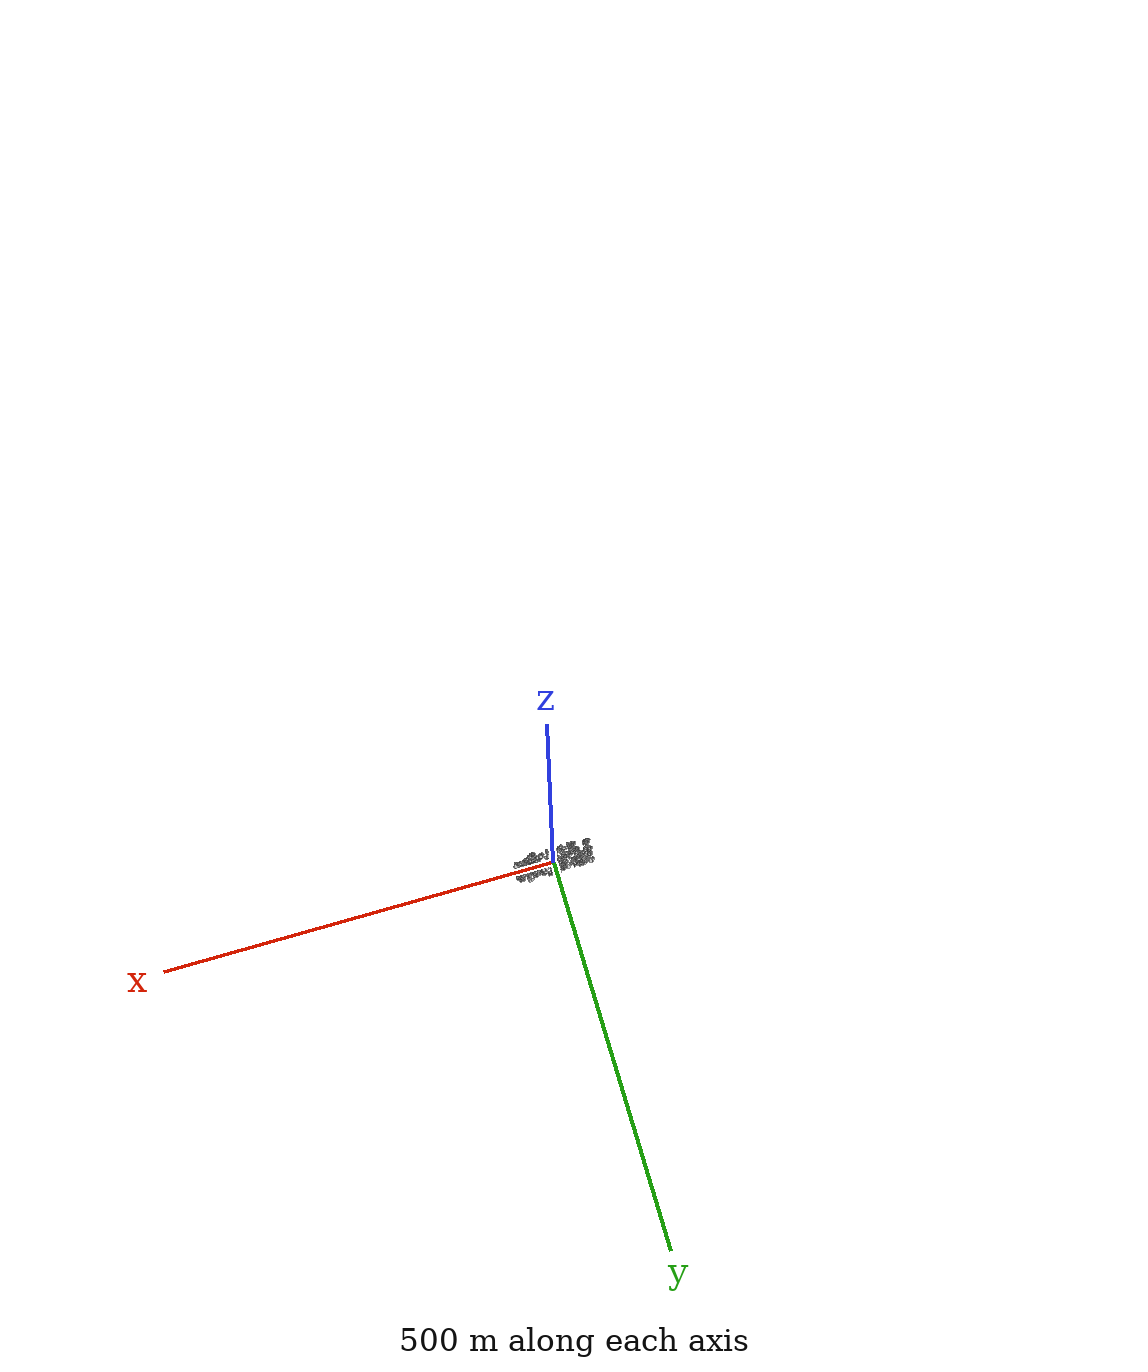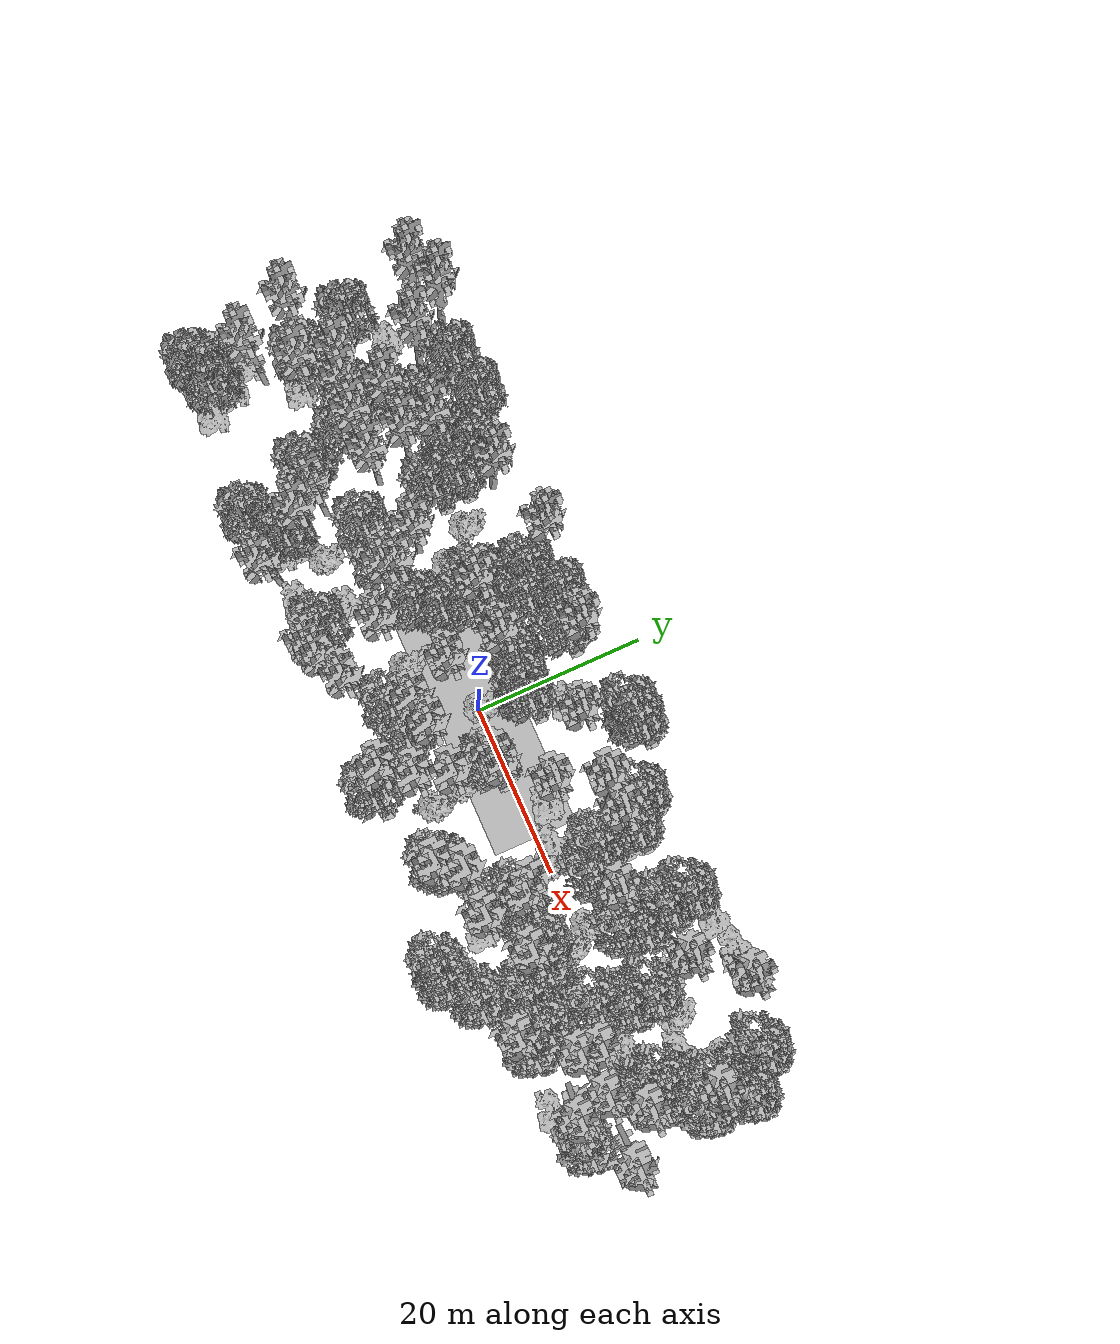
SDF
<sdf version="1.7">
    <world name="default">
        <plugin name="mrs_gazebo_static_transform_republisher_plugin" filename="libMrsGazeboCommonResources_StaticTransformRepublisher.so"/>
        <spherical_coordinates>
            <surface_model>EARTH_WGS84</surface_model>
            <latitude_deg>47.3977</latitude_deg>
            <longitude_deg>8.54559</longitude_deg>
            <elevation>0</elevation>
            <heading_deg>0</heading_deg>
        </spherical_coordinates>
        <physics name="default_physics" default="0" type="ode">
            <ode>
                <solver>
                    <type>quick</type>
                    <iters>10</iters>
                    <sor>1.3</sor>
                    <use_dynamic_moi_rescaling>0</use_dynamic_moi_rescaling>
                </solver>
                <constraints>
                    <cfm>0</cfm>
                    <erp>0.2</erp>
                    <contact_max_correcting_vel>1000</contact_max_correcting_vel>
                    <contact_surface_layer>0.001</contact_surface_layer>
                </constraints>
            </ode>
            <max_step_size>0.004</max_step_size>
            <real_time_factor>1</real_time_factor>
            <real_time_update_rate>250</real_time_update_rate>
        </physics>
        <scene>
            <shadows>0</shadows>
            <ambient>0.4 0.4 0.4 1</ambient>
            <background>0.7 0.7 0.7 1</background>
        </scene>
        <light name="sun" type="directional">
            <pose>0 0 1000 0.4 0.2 0</pose>
            <diffuse>1 1 1 1</diffuse>
            <specular>0.6 0.6 0.6 1</specular>
            <direction>0.1 0.1 -0.9</direction>
            <attenuation>
                <range>20</range>
                <constant>0.5</constant>
                <linear>0.01</linear>
                <quadratic>0.001</quadratic>
            </attenuation>
            <cast_shadows>1</cast_shadows>
            <spot>
                <inner_angle>0</inner_angle>
                <outer_angle>0</outer_angle>
                <falloff>0</falloff>
            </spot>
        </light>
        <model name="ground_plane">
            <static>1</static>
            <link name="link">
                <collision name="collision">
                    <pose>-50 0 0 0 -0 0</pose>
                    <geometry>
                        <plane>
                            <normal>0 0 1</normal>
                            <size>100 100</size>
                        </plane>
                    </geometry>
                    <surface>
                        <contact>
                            <ode>
                                <min_depth>0.01</min_depth>
                                <max_vel>0</max_vel>
                            </ode>
                        </contact>
                        <friction>
                            <ode/>
                            <torsional>
                                <ode/>
                            </torsional>
                        </friction>
                        <bounce/>
                    </surface>
                    <max_contacts>10</max_contacts>
                </collision>
                <visual name="grass">
                    <pose>0 0 0 0 -0 0</pose>
                    <cast_shadows>0</cast_shadows>
                    <geometry>
                        <mesh>
                            <scale>0.5814285714285714 0.18142857142857144 0.1</scale>
                            <uri>file://grass_plane/meshes/grass_plane.dae</uri>
                        </mesh>
                    </geometry>
                </visual>
                <self_collide>0</self_collide>
                <enable_wind>0</enable_wind>
                <kinematic>0</kinematic>
            </link>
        </model>
        <model name="the_void">
            <static>1</static>
            <link name="link">
                <pose>0 0 0.1 0 -0 0</pose>
                <visual name="the_void">
                    <pose>0 0 2 0 -0 0</pose>
                    <geometry>
                        <sphere>
                            <radius>0.25</radius>
                        </sphere>
                    </geometry>
                    <material>
                        <script>
                            <uri>file://media/materials/scripts/Gazebo.material</uri>
                            <name>Gazebo/Black</name>
                        </script>
                    </material>
                </visual>
                <self_collide>0</self_collide>
                <enable_wind>0</enable_wind>
                <kinematic>0</kinematic>
            </link>
            <pose>-1000 -1000 0 0 -0 0</pose>
        </model>
        <gui fullscreen="0">
            <camera name="camera">
                <pose>35.1577 98.6044 40.0204 0 0.407996 -1.99761</pose>
                <view_controller>orbit</view_controller>
                <projection_type>perspective</projection_type>
            </camera>
        </gui>
        <plugin name="mrs_gazebo_rviz_cam_synchronizer" filename="libMrsGazeboCommonResources_RvizCameraSynchronizer.so">
            <target_frame_id>gazebo_user_camera</target_frame_id>
            <world_origin_frame_id>uav1/gps_origin</world_origin_frame_id>
            <frame_to_follow>uav1</frame_to_follow>
        </plugin>
        <gravity>0 0 -9.8066</gravity>
        <magnetic_field>6e-06 2.3e-05 -4.2e-05</magnetic_field>
        <atmosphere type="adiabatic"/>
        <wind/>
        <model name="Tree 0">
            <static>1</static>
            <pose>47.69252094666231 9.249128996621579 0 1.57079 -0 0</pose>
            <link name="link">
                <pose>0 0 0 0 -0 0</pose>
                <collision name="collision">
                    <geometry>
                        <mesh>
                            <scale>3.5 5 3.5</scale>
                            <uri>model://tree_2/meshes/tree_2.obj</uri>
                        </mesh>
                    </geometry>
                    <max_contacts>10</max_contacts>
                    <surface>
                        <contact>
                            <ode/>
                        </contact>
                        <bounce/>
                        <friction>
                            <torsional>
                                <ode/>
                            </torsional>
                            <ode/>
                        </friction>
                    </surface>
                </collision>
                <visual name="visual">
                    <geometry>
                        <mesh>
                            <scale>3.5 5 3.5</scale>
                            <uri>model://tree_2/meshes/tree_2.obj</uri>
                        </mesh>
                    </geometry>
                </visual>
                <self_collide>0</self_collide>
                <enable_wind>0</enable_wind>
                <kinematic>0</kinematic>
            </link>
        </model>
        <model name="Tree 1">
            <static>1</static>
            <pose>14.877925519280105 -8.167728986980194 0 1.57079 -0 0</pose>
            <link name="link">
                <pose>0 0 0 0 -0 0</pose>
                <collision name="collision">
                    <geometry>
                        <mesh>
                            <scale>3.5 5 3.5</scale>
                            <uri>model://tree_9/meshes/tree_9.obj</uri>
                        </mesh>
                    </geometry>
                    <max_contacts>10</max_contacts>
                    <surface>
                        <contact>
                            <ode/>
                        </contact>
                        <bounce/>
                        <friction>
                            <torsional>
                                <ode/>
                            </torsional>
                            <ode/>
                        </friction>
                    </surface>
                </collision>
                <visual name="visual">
                    <geometry>
                        <mesh>
                            <scale>3.5 5 3.5</scale>
                            <uri>model://tree_9/meshes/tree_9.obj</uri>
                        </mesh>
                    </geometry>
                </visual>
                <self_collide>0</self_collide>
                <enable_wind>0</enable_wind>
                <kinematic>0</kinematic>
            </link>
        </model>
        <model name="Tree 2">
            <static>1</static>
            <pose>45.17606604609456 9.419935993296292 0 1.57079 -0 0</pose>
            <link name="link">
                <pose>0 0 0 0 -0 0</pose>
                <collision name="collision">
                    <geometry>
                        <mesh>
                            <scale>4 2.5 4</scale>
                            <uri>model://tree_1/meshes/tree_1.obj</uri>
                        </mesh>
                    </geometry>
                    <max_contacts>10</max_contacts>
                    <surface>
                        <contact>
                            <ode/>
                        </contact>
                        <bounce/>
                        <friction>
                            <torsional>
                                <ode/>
                            </torsional>
                            <ode/>
                        </friction>
                    </surface>
                </collision>
                <visual name="visual">
                    <geometry>
                        <mesh>
                            <scale>4 2.5 4</scale>
                            <uri>model://tree_1/meshes/tree_1.obj</uri>
                        </mesh>
                    </geometry>
                </visual>
                <self_collide>0</self_collide>
                <enable_wind>0</enable_wind>
                <kinematic>0</kinematic>
            </link>
        </model>
        <model name="Tree 3">
            <static>1</static>
            <pose>34.5325173879184 -9.449591073487406 0 1.57079 -0 0</pose>
            <link name="link">
                <pose>0 0 0 0 -0 0</pose>
                <collision name="collision">
                    <geometry>
                        <mesh>
                            <scale>3.5 5 3.5</scale>
                            <uri>model://tree_2/meshes/tree_2.obj</uri>
                        </mesh>
                    </geometry>
                    <max_contacts>10</max_contacts>
                    <surface>
                        <contact>
                            <ode/>
                        </contact>
                        <bounce/>
                        <friction>
                            <torsional>
                                <ode/>
                            </torsional>
                            <ode/>
                        </friction>
                    </surface>
                </collision>
                <visual name="visual">
                    <geometry>
                        <mesh>
                            <scale>3.5 5 3.5</scale>
                            <uri>model://tree_2/meshes/tree_2.obj</uri>
                        </mesh>
                    </geometry>
                </visual>
                <self_collide>0</self_collide>
                <enable_wind>0</enable_wind>
                <kinematic>0</kinematic>
            </link>
        </model>
        <model name="Tree 4">
            <static>1</static>
            <pose>-10.991106747070546 2.614081830153687 0 1.57079 -0 0</pose>
            <link name="link">
                <pose>0 0 0 0 -0 0</pose>
                <collision name="collision">
                    <geometry>
                        <mesh>
                            <scale>3 2 3</scale>
                            <uri>model://tree_3/meshes/tree_3.obj</uri>
                        </mesh>
                    </geometry>
                    <max_contacts>10</max_contacts>
                    <surface>
                        <contact>
                            <ode/>
                        </contact>
                        <bounce/>
                        <friction>
                            <torsional>
                                <ode/>
                            </torsional>
                            <ode/>
                        </friction>
                    </surface>
                </collision>
                <visual name="visual">
                    <geometry>
                        <mesh>
                            <scale>3 2 3</scale>
                            <uri>model://tree_3/meshes/tree_3.obj</uri>
                        </mesh>
                    </geometry>
                </visual>
                <self_collide>0</self_collide>
                <enable_wind>0</enable_wind>
                <kinematic>0</kinematic>
            </link>
        </model>
        <model name="Tree 5">
            <static>1</static>
            <pose>-4.034608851743975 11.470205256583032 0 1.57079 -0 0</pose>
            <link name="link">
                <pose>0 0 0 0 -0 0</pose>
                <collision name="collision">
                    <geometry>
                        <mesh>
                            <scale>3.5 5 3.5</scale>
                            <uri>model://tree_2/meshes/tree_2.obj</uri>
                        </mesh>
                    </geometry>
                    <max_contacts>10</max_contacts>
                    <surface>
                        <contact>
                            <ode/>
                        </contact>
                        <bounce/>
                        <friction>
                            <torsional>
                                <ode/>
                            </torsional>
                            <ode/>
                        </friction>
                    </surface>
                </collision>
                <visual name="visual">
                    <geometry>
                        <mesh>
                            <scale>3.5 5 3.5</scale>
                            <uri>model://tree_2/meshes/tree_2.obj</uri>
                        </mesh>
                    </geometry>
                </visual>
                <self_collide>0</self_collide>
                <enable_wind>0</enable_wind>
                <kinematic>0</kinematic>
            </link>
        </model>
        <model name="Tree 6">
            <static>1</static>
            <pose>27.85685735956963 6.043179859401473 0 1.57079 -0 0</pose>
            <link name="link">
                <pose>0 0 0 0 -0 0</pose>
                <collision name="collision">
                    <geometry>
                        <mesh>
                            <scale>3.5 5 3.5</scale>
                            <uri>model://tree_2/meshes/tree_2.obj</uri>
                        </mesh>
                    </geometry>
                    <max_contacts>10</max_contacts>
                    <surface>
                        <contact>
                            <ode/>
                        </contact>
                        <bounce/>
                        <friction>
                            <torsional>
                                <ode/>
                            </torsional>
                            <ode/>
                        </friction>
                    </surface>
                </collision>
                <visual name="visual">
                    <geometry>
                        <mesh>
                            <scale>3.5 5 3.5</scale>
                            <uri>model://tree_2/meshes/tree_2.obj</uri>
                        </mesh>
                    </geometry>
                </visual>
                <self_collide>0</self_collide>
                <enable_wind>0</enable_wind>
                <kinematic>0</kinematic>
            </link>
        </model>
        <model name="Tree 7">
            <static>1</static>
            <pose>20.144166604871202 4.434345135278459 0 1.57079 -0 0</pose>
            <link name="link">
                <pose>0 0 0 0 -0 0</pose>
                <collision name="collision">
                    <geometry>
                        <mesh>
                            <scale>4 2.5 4</scale>
                            <uri>model://tree_1/meshes/tree_1.obj</uri>
                        </mesh>
                    </geometry>
                    <max_contacts>10</max_contacts>
                    <surface>
                        <contact>
                            <ode/>
                        </contact>
                        <bounce/>
                        <friction>
                            <torsional>
                                <ode/>
                            </torsional>
                            <ode/>
                        </friction>
                    </surface>
                </collision>
                <visual name="visual">
                    <geometry>
                        <mesh>
                            <scale>4 2.5 4</scale>
                            <uri>model://tree_1/meshes/tree_1.obj</uri>
                        </mesh>
                    </geometry>
                </visual>
                <self_collide>0</self_collide>
                <enable_wind>0</enable_wind>
                <kinematic>0</kinematic>
            </link>
        </model>
        <model name="Tree 8">
            <static>1</static>
            <pose>15.405665071420202 11.719186739586632 0 1.57079 -0 0</pose>
            <link name="link">
                <pose>0 0 0 0 -0 0</pose>
                <collision name="collision">
                    <geometry>
                        <mesh>
                            <scale>3.5 5 3.5</scale>
                            <uri>model://tree_2/meshes/tree_2.obj</uri>
                        </mesh>
                    </geometry>
                    <max_contacts>10</max_contacts>
                    <surface>
                        <contact>
                            <ode/>
                        </contact>
                        <bounce/>
                        <friction>
                            <torsional>
                                <ode/>
                            </torsional>
                            <ode/>
                        </friction>
                    </surface>
                </collision>
                <visual name="visual">
                    <geometry>
                        <mesh>
                            <scale>3.5 5 3.5</scale>
                            <uri>model://tree_2/meshes/tree_2.obj</uri>
                        </mesh>
                    </geometry>
                </visual>
                <self_collide>0</self_collide>
                <enable_wind>0</enable_wind>
                <kinematic>0</kinematic>
            </link>
        </model>
        <model name="Tree 9">
            <static>1</static>
            <pose>-23.025613929217126 -8.91676801810691 0 1.57079 -0 0</pose>
            <link name="link">
                <pose>0 0 0 0 -0 0</pose>
                <collision name="collision">
                    <geometry>
                        <mesh>
                            <scale>4 2.5 4</scale>
                            <uri>model://tree_1/meshes/tree_1.obj</uri>
                        </mesh>
                    </geometry>
                    <max_contacts>10</max_contacts>
                    <surface>
                        <contact>
                            <ode/>
                        </contact>
                        <bounce/>
                        <friction>
                            <torsional>
                                <ode/>
                            </torsional>
                            <ode/>
                        </friction>
                    </surface>
                </collision>
                <visual name="visual">
                    <geometry>
                        <mesh>
                            <scale>4 2.5 4</scale>
                            <uri>model://tree_1/meshes/tree_1.obj</uri>
                        </mesh>
                    </geometry>
                </visual>
                <self_collide>0</self_collide>
                <enable_wind>0</enable_wind>
                <kinematic>0</kinematic>
            </link>
        </model>
        <model name="Tree 10">
            <static>1</static>
            <pose>43.063630282127505 1.636747581096646 0 1.57079 -0 0</pose>
            <link name="link">
                <pose>0 0 0 0 -0 0</pose>
                <collision name="collision">
                    <geometry>
                        <mesh>
                            <scale>3.5 5 3.5</scale>
                            <uri>model://tree_2/meshes/tree_2.obj</uri>
                        </mesh>
                    </geometry>
                    <max_contacts>10</max_contacts>
                    <surface>
                        <contact>
                            <ode/>
                        </contact>
                        <bounce/>
                        <friction>
                            <torsional>
                                <ode/>
                            </torsional>
                            <ode/>
                        </friction>
                    </surface>
                </collision>
                <visual name="visual">
                    <geometry>
                        <mesh>
                            <scale>3.5 5 3.5</scale>
                            <uri>model://tree_2/meshes/tree_2.obj</uri>
                        </mesh>
                    </geometry>
                </visual>
                <self_collide>0</self_collide>
                <enable_wind>0</enable_wind>
                <kinematic>0</kinematic>
            </link>
        </model>
        <model name="Tree 11">
            <static>1</static>
            <pose>-44.31328368306119 -12.560162882290264 0 1.57079 -0 0</pose>
            <link name="link">
                <pose>0 0 0 0 -0 0</pose>
                <collision name="collision">
                    <geometry>
                        <mesh>
                            <scale>3.5 5 3.5</scale>
                            <uri>model://tree_2/meshes/tree_2.obj</uri>
                        </mesh>
                    </geometry>
                    <max_contacts>10</max_contacts>
                    <surface>
                        <contact>
                            <ode/>
                        </contact>
                        <bounce/>
                        <friction>
                            <torsional>
                                <ode/>
                            </torsional>
                            <ode/>
                        </friction>
                    </surface>
                </collision>
                <visual name="visual">
                    <geometry>
                        <mesh>
                            <scale>3.5 5 3.5</scale>
                            <uri>model://tree_2/meshes/tree_2.obj</uri>
                        </mesh>
                    </geometry>
                </visual>
                <self_collide>0</self_collide>
                <enable_wind>0</enable_wind>
                <kinematic>0</kinematic>
            </link>
        </model>
        <model name="Tree 12">
            <static>1</static>
            <pose>-40.38204499397769 2.0866068830576374 0 1.57079 -0 0</pose>
            <link name="link">
                <pose>0 0 0 0 -0 0</pose>
                <collision name="collision">
                    <geometry>
                        <mesh>
                            <scale>4 2.5 4</scale>
                            <uri>model://tree_1/meshes/tree_1.obj</uri>
                        </mesh>
                    </geometry>
                    <max_contacts>10</max_contacts>
                    <surface>
                        <contact>
                            <ode/>
                        </contact>
                        <bounce/>
                        <friction>
                            <torsional>
                                <ode/>
                            </torsional>
                            <ode/>
                        </friction>
                    </surface>
                </collision>
                <visual name="visual">
                    <geometry>
                        <mesh>
                            <scale>4 2.5 4</scale>
                            <uri>model://tree_1/meshes/tree_1.obj</uri>
                        </mesh>
                    </geometry>
                </visual>
                <self_collide>0</self_collide>
                <enable_wind>0</enable_wind>
                <kinematic>0</kinematic>
            </link>
        </model>
        <model name="Tree 13">
            <static>1</static>
            <pose>6.834853951498921 -5.358503244813338 0 1.57079 -0 0</pose>
            <link name="link">
                <pose>0 0 0 0 -0 0</pose>
                <collision name="collision">
                    <geometry>
                        <mesh>
                            <scale>4 2.5 4</scale>
                            <uri>model://tree_1/meshes/tree_1.obj</uri>
                        </mesh>
                    </geometry>
                    <max_contacts>10</max_contacts>
                    <surface>
                        <contact>
                            <ode/>
                        </contact>
                        <bounce/>
                        <friction>
                            <torsional>
                                <ode/>
                            </torsional>
                            <ode/>
                        </friction>
                    </surface>
                </collision>
                <visual name="visual">
                    <geometry>
                        <mesh>
                            <scale>4 2.5 4</scale>
                            <uri>model://tree_1/meshes/tree_1.obj</uri>
                        </mesh>
                    </geometry>
                </visual>
                <self_collide>0</self_collide>
                <enable_wind>0</enable_wind>
                <kinematic>0</kinematic>
            </link>
        </model>
        <model name="Tree 14">
            <static>1</static>
            <pose>-32.63130354765136 -5.6528169579738545 0 1.57079 -0 0</pose>
            <link name="link">
                <pose>0 0 0 0 -0 0</pose>
                <collision name="collision">
                    <geometry>
                        <mesh>
                            <scale>4 2.5 4</scale>
                            <uri>model://tree_1/meshes/tree_1.obj</uri>
                        </mesh>
                    </geometry>
                    <max_contacts>10</max_contacts>
                    <surface>
                        <contact>
                            <ode/>
                        </contact>
                        <bounce/>
                        <friction>
                            <torsional>
                                <ode/>
                            </torsional>
                            <ode/>
                        </friction>
                    </surface>
                </collision>
                <visual name="visual">
                    <geometry>
                        <mesh>
                            <scale>4 2.5 4</scale>
                            <uri>model://tree_1/meshes/tree_1.obj</uri>
                        </mesh>
                    </geometry>
                </visual>
                <self_collide>0</self_collide>
                <enable_wind>0</enable_wind>
                <kinematic>0</kinematic>
            </link>
        </model>
        <model name="Tree 15">
            <static>1</static>
            <pose>40.89080094411801 -4.3779563781776005 0 1.57079 -0 0</pose>
            <link name="link">
                <pose>0 0 0 0 -0 0</pose>
                <collision name="collision">
                    <geometry>
                        <mesh>
                            <scale>3.5 5 3.5</scale>
                            <uri>model://tree_9/meshes/tree_9.obj</uri>
                        </mesh>
                    </geometry>
                    <max_contacts>10</max_contacts>
                    <surface>
                        <contact>
                            <ode/>
                        </contact>
                        <bounce/>
                        <friction>
                            <torsional>
                                <ode/>
                            </torsional>
                            <ode/>
                        </friction>
                    </surface>
                </collision>
                <visual name="visual">
                    <geometry>
                        <mesh>
                            <scale>3.5 5 3.5</scale>
                            <uri>model://tree_9/meshes/tree_9.obj</uri>
                        </mesh>
                    </geometry>
                </visual>
                <self_collide>0</self_collide>
                <enable_wind>0</enable_wind>
                <kinematic>0</kinematic>
            </link>
        </model>
        <model name="Tree 16">
            <static>1</static>
            <pose>8.169282240349212 14.693758985796201 0 1.57079 -0 0</pose>
            <link name="link">
                <pose>0 0 0 0 -0 0</pose>
                <collision name="collision">
                    <geometry>
                        <mesh>
                            <scale>3.5 5 3.5</scale>
                            <uri>model://tree_2/meshes/tree_2.obj</uri>
                        </mesh>
                    </geometry>
                    <max_contacts>10</max_contacts>
                    <surface>
                        <contact>
                            <ode/>
                        </contact>
                        <bounce/>
                        <friction>
                            <torsional>
                                <ode/>
                            </torsional>
                            <ode/>
                        </friction>
                    </surface>
                </collision>
                <visual name="visual">
                    <geometry>
                        <mesh>
                            <scale>3.5 5 3.5</scale>
                            <uri>model://tree_2/meshes/tree_2.obj</uri>
                        </mesh>
                    </geometry>
                </visual>
                <self_collide>0</self_collide>
                <enable_wind>0</enable_wind>
                <kinematic>0</kinematic>
            </link>
        </model>
        <model name="Tree 17">
            <static>1</static>
            <pose>-11.648803074690449 0.49937925572685415 0 1.57079 -0 0</pose>
            <link name="link">
                <pose>0 0 0 0 -0 0</pose>
                <collision name="collision">
                    <geometry>
                        <mesh>
                            <scale>3.5 5 3.5</scale>
                            <uri>model://tree_2/meshes/tree_2.obj</uri>
                        </mesh>
                    </geometry>
                    <max_contacts>10</max_contacts>
                    <surface>
                        <contact>
                            <ode/>
                        </contact>
                        <bounce/>
                        <friction>
                            <torsional>
                                <ode/>
                            </torsional>
                            <ode/>
                        </friction>
                    </surface>
                </collision>
                <visual name="visual">
                    <geometry>
                        <mesh>
                            <scale>3.5 5 3.5</scale>
                            <uri>model://tree_2/meshes/tree_2.obj</uri>
                        </mesh>
                    </geometry>
                </visual>
                <self_collide>0</self_collide>
                <enable_wind>0</enable_wind>
                <kinematic>0</kinematic>
            </link>
        </model>
        <model name="Tree 18">
            <static>1</static>
            <pose>-23.352166290836816 12.0966931474726 0 1.57079 -0 0</pose>
            <link name="link">
                <pose>0 0 0 0 -0 0</pose>
                <collision name="collision">
                    <geometry>
                        <mesh>
                            <scale>3.5 5 3.5</scale>
                            <uri>model://tree_9/meshes/tree_9.obj</uri>
                        </mesh>
                    </geometry>
                    <max_contacts>10</max_contacts>
                    <surface>
                        <contact>
                            <ode/>
                        </contact>
                        <bounce/>
                        <friction>
                            <torsional>
                                <ode/>
                            </torsional>
                            <ode/>
                        </friction>
                    </surface>
                </collision>
                <visual name="visual">
                    <geometry>
                        <mesh>
                            <scale>3.5 5 3.5</scale>
                            <uri>model://tree_9/meshes/tree_9.obj</uri>
                        </mesh>
                    </geometry>
                </visual>
                <self_collide>0</self_collide>
                <enable_wind>0</enable_wind>
                <kinematic>0</kinematic>
            </link>
        </model>
        <model name="Tree 19">
            <static>1</static>
            <pose>18.73259302779485 0.4545113756770931 0 1.57079 -0 0</pose>
            <link name="link">
                <pose>0 0 0 0 -0 0</pose>
                <collision name="collision">
                    <geometry>
                        <mesh>
                            <scale>4 2.5 4</scale>
                            <uri>model://tree_1/meshes/tree_1.obj</uri>
                        </mesh>
                    </geometry>
                    <max_contacts>10</max_contacts>
                    <surface>
                        <contact>
                            <ode/>
                        </contact>
                        <bounce/>
                        <friction>
                            <torsional>
                                <ode/>
                            </torsional>
                            <ode/>
                        </friction>
                    </surface>
                </collision>
                <visual name="visual">
                    <geometry>
                        <mesh>
                            <scale>4 2.5 4</scale>
                            <uri>model://tree_1/meshes/tree_1.obj</uri>
                        </mesh>
                    </geometry>
                </visual>
                <self_collide>0</self_collide>
                <enable_wind>0</enable_wind>
                <kinematic>0</kinematic>
            </link>
        </model>
        <model name="Tree 20">
            <static>1</static>
            <pose>36.97406588445705 5.96686435955484 0 1.57079 -0 0</pose>
            <link name="link">
                <pose>0 0 0 0 -0 0</pose>
                <collision name="collision">
                    <geometry>
                        <mesh>
                            <scale>4 2.5 4</scale>
                            <uri>model://tree_1/meshes/tree_1.obj</uri>
                        </mesh>
                    </geometry>
                    <max_contacts>10</max_contacts>
                    <surface>
                        <contact>
                            <ode/>
                        </contact>
                        <bounce/>
                        <friction>
                            <torsional>
                                <ode/>
                            </torsional>
                            <ode/>
                        </friction>
                    </surface>
                </collision>
                <visual name="visual">
                    <geometry>
                        <mesh>
                            <scale>4 2.5 4</scale>
                            <uri>model://tree_1/meshes/tree_1.obj</uri>
                        </mesh>
                    </geometry>
                </visual>
                <self_collide>0</self_collide>
                <enable_wind>0</enable_wind>
                <kinematic>0</kinematic>
            </link>
        </model>
        <model name="Tree 21">
            <static>1</static>
            <pose>-19.82992579264648 1.2460721862466535 0 1.57079 -0 0</pose>
            <link name="link">
                <pose>0 0 0 0 -0 0</pose>
                <collision name="collision">
                    <geometry>
                        <mesh>
                            <scale>3.5 5 3.5</scale>
                            <uri>model://tree_9/meshes/tree_9.obj</uri>
                        </mesh>
                    </geometry>
                    <max_contacts>10</max_contacts>
                    <surface>
                        <contact>
                            <ode/>
                        </contact>
                        <bounce/>
                        <friction>
                            <torsional>
                                <ode/>
                            </torsional>
                            <ode/>
                        </friction>
                    </surface>
                </collision>
                <visual name="visual">
                    <geometry>
                        <mesh>
                            <scale>3.5 5 3.5</scale>
                            <uri>model://tree_9/meshes/tree_9.obj</uri>
                        </mesh>
                    </geometry>
                </visual>
                <self_collide>0</self_collide>
                <enable_wind>0</enable_wind>
                <kinematic>0</kinematic>
            </link>
        </model>
        <model name="Tree 22">
            <static>1</static>
            <pose>44.34264651618197 0.5009626305823183 0 1.57079 -0 0</pose>
            <link name="link">
                <pose>0 0 0 0 -0 0</pose>
                <collision name="collision">
                    <geometry>
                        <mesh>
                            <scale>3.5 5 3.5</scale>
                            <uri>model://tree_2/meshes/tree_2.obj</uri>
                        </mesh>
                    </geometry>
                    <max_contacts>10</max_contacts>
                    <surface>
                        <contact>
                            <ode/>
                        </contact>
                        <bounce/>
                        <friction>
                            <torsional>
                                <ode/>
                            </torsional>
                            <ode/>
                        </friction>
                    </surface>
                </collision>
                <visual name="visual">
                    <geometry>
                        <mesh>
                            <scale>3.5 5 3.5</scale>
                            <uri>model://tree_2/meshes/tree_2.obj</uri>
                        </mesh>
                    </geometry>
                </visual>
                <self_collide>0</self_collide>
                <enable_wind>0</enable_wind>
                <kinematic>0</kinematic>
            </link>
        </model>
        <model name="Tree 23">
            <static>1</static>
            <pose>-26.937929977554283 10.79643842564813 0 1.57079 -0 0</pose>
            <link name="link">
                <pose>0 0 0 0 -0 0</pose>
                <collision name="collision">
                    <geometry>
                        <mesh>
                            <scale>3.5 5 3.5</scale>
                            <uri>model://tree_2/meshes/tree_2.obj</uri>
                        </mesh>
                    </geometry>
                    <max_contacts>10</max_contacts>
                    <surface>
                        <contact>
                            <ode/>
                        </contact>
                        <bounce/>
                        <friction>
                            <torsional>
                                <ode/>
                            </torsional>
                            <ode/>
                        </friction>
                    </surface>
                </collision>
                <visual name="visual">
                    <geometry>
                        <mesh>
                            <scale>3.5 5 3.5</scale>
                            <uri>model://tree_2/meshes/tree_2.obj</uri>
                        </mesh>
                    </geometry>
                </visual>
                <self_collide>0</self_collide>
                <enable_wind>0</enable_wind>
                <kinematic>0</kinematic>
            </link>
        </model>
        <model name="Tree 24">
            <static>1</static>
            <pose>-29.39940443687185 -10.268930130422824 0 1.57079 -0 0</pose>
            <link name="link">
                <pose>0 0 0 0 -0 0</pose>
                <collision name="collision">
                    <geometry>
                        <mesh>
                            <scale>3 2 3</scale>
                            <uri>model://tree_3/meshes/tree_3.obj</uri>
                        </mesh>
                    </geometry>
                    <max_contacts>10</max_contacts>
                    <surface>
                        <contact>
                            <ode/>
                        </contact>
                        <bounce/>
                        <friction>
                            <torsional>
                                <ode/>
                            </torsional>
                            <ode/>
                        </friction>
                    </surface>
                </collision>
                <visual name="visual">
                    <geometry>
                        <mesh>
                            <scale>3 2 3</scale>
                            <uri>model://tree_3/meshes/tree_3.obj</uri>
                        </mesh>
                    </geometry>
                </visual>
                <self_collide>0</self_collide>
                <enable_wind>0</enable_wind>
                <kinematic>0</kinematic>
            </link>
        </model>
        <model name="Tree 25">
            <static>1</static>
            <pose>45.603729243816204 -8.233047635370838 0 1.57079 -0 0</pose>
            <link name="link">
                <pose>0 0 0 0 -0 0</pose>
                <collision name="collision">
                    <geometry>
                        <mesh>
                            <scale>3.5 5 3.5</scale>
                            <uri>model://tree_2/meshes/tree_2.obj</uri>
                        </mesh>
                    </geometry>
                    <max_contacts>10</max_contacts>
                    <surface>
                        <contact>
                            <ode/>
                        </contact>
                        <bounce/>
                        <friction>
                            <torsional>
                                <ode/>
                            </torsional>
                            <ode/>
                        </friction>
                    </surface>
                </collision>
                <visual name="visual">
                    <geometry>
                        <mesh>
                            <scale>3.5 5 3.5</scale>
                            <uri>model://tree_2/meshes/tree_2.obj</uri>
                        </mesh>
                    </geometry>
                </visual>
                <self_collide>0</self_collide>
                <enable_wind>0</enable_wind>
                <kinematic>0</kinematic>
            </link>
        </model>
        <model name="Tree 26">
            <static>1</static>
            <pose>3.758328886433567 -14.008214005512738 0 1.57079 -0 0</pose>
            <link name="link">
                <pose>0 0 0 0 -0 0</pose>
                <collision name="collision">
                    <geometry>
                        <mesh>
                            <scale>3.5 5 3.5</scale>
                            <uri>model://tree_2/meshes/tree_2.obj</uri>
                        </mesh>
                    </geometry>
                    <max_contacts>10</max_contacts>
                    <surface>
                        <contact>
                            <ode/>
                        </contact>
                        <bounce/>
                        <friction>
                            <torsional>
                                <ode/>
                            </torsional>
                            <ode/>
                        </friction>
                    </surface>
                </collision>
                <visual name="visual">
                    <geometry>
                        <mesh>
                            <scale>3.5 5 3.5</scale>
                            <uri>model://tree_2/meshes/tree_2.obj</uri>
                        </mesh>
                    </geometry>
                </visual>
                <self_collide>0</self_collide>
                <enable_wind>0</enable_wind>
                <kinematic>0</kinematic>
            </link>
        </model>
        <model name="Tree 27">
            <static>1</static>
            <pose>-0.5780417767173276 5.187824880138397 0 1.57079 -0 0</pose>
            <link name="link">
                <pose>0 0 0 0 -0 0</pose>
                <collision name="collision">
                    <geometry>
                        <mesh>
                            <scale>3.5 5 3.5</scale>
                            <uri>model://tree_2/meshes/tree_2.obj</uri>
                        </mesh>
                    </geometry>
                    <max_contacts>10</max_contacts>
                    <surface>
                        <contact>
                            <ode/>
                        </contact>
                        <bounce/>
                        <friction>
                            <torsional>
                                <ode/>
                            </torsional>
                            <ode/>
                        </friction>
                    </surface>
                </collision>
                <visual name="visual">
                    <geometry>
                        <mesh>
                            <scale>3.5 5 3.5</scale>
                            <uri>model://tree_2/meshes/tree_2.obj</uri>
                        </mesh>
                    </geometry>
                </visual>
                <self_collide>0</self_collide>
                <enable_wind>0</enable_wind>
                <kinematic>0</kinematic>
            </link>
        </model>
        <model name="Tree 28">
            <static>1</static>
            <pose>40.806572974014315 -0.7334378901298848 0 1.57079 -0 0</pose>
            <link name="link">
                <pose>0 0 0 0 -0 0</pose>
                <collision name="collision">
                    <geometry>
                        <mesh>
                            <scale>3 2 3</scale>
                            <uri>model://tree_3/meshes/tree_3.obj</uri>
                        </mesh>
                    </geometry>
                    <max_contacts>10</max_contacts>
                    <surface>
                        <contact>
                            <ode/>
                        </contact>
                        <bounce/>
                        <friction>
                            <torsional>
                                <ode/>
                            </torsional>
                            <ode/>
                        </friction>
                    </surface>
                </collision>
                <visual name="visual">
                    <geometry>
                        <mesh>
                            <scale>3 2 3</scale>
                            <uri>model://tree_3/meshes/tree_3.obj</uri>
                        </mesh>
                    </geometry>
                </visual>
                <self_collide>0</self_collide>
                <enable_wind>0</enable_wind>
                <kinematic>0</kinematic>
            </link>
        </model>
        <model name="Tree 29">
            <static>1</static>
            <pose>33.10193095426334 -1.6030235810332467 0 1.57079 -0 0</pose>
            <link name="link">
                <pose>0 0 0 0 -0 0</pose>
                <collision name="collision">
                    <geometry>
                        <mesh>
                            <scale>3.5 5 3.5</scale>
                            <uri>model://tree_2/meshes/tree_2.obj</uri>
                        </mesh>
                    </geometry>
                    <max_contacts>10</max_contacts>
                    <surface>
                        <contact>
                            <ode/>
                        </contact>
                        <bounce/>
                        <friction>
                            <torsional>
                                <ode/>
                            </torsional>
                            <ode/>
                        </friction>
                    </surface>
                </collision>
                <visual name="visual">
                    <geometry>
                        <mesh>
                            <scale>3.5 5 3.5</scale>
                            <uri>model://tree_2/meshes/tree_2.obj</uri>
                        </mesh>
                    </geometry>
                </visual>
                <self_collide>0</self_collide>
                <enable_wind>0</enable_wind>
                <kinematic>0</kinematic>
            </link>
        </model>
        <model name="Tree 30">
            <static>1</static>
            <pose>-48.11128516027013 -1.2711060013172197 0 1.57079 -0 0</pose>
            <link name="link">
                <pose>0 0 0 0 -0 0</pose>
                <collision name="collision">
                    <geometry>
                        <mesh>
                            <scale>3.5 5 3.5</scale>
                            <uri>model://tree_9/meshes/tree_9.obj</uri>
                        </mesh>
                    </geometry>
                    <max_contacts>10</max_contacts>
                    <surface>
                        <contact>
                            <ode/>
                        </contact>
                        <bounce/>
                        <friction>
                            <torsional>
                                <ode/>
                            </torsional>
                            <ode/>
                        </friction>
                    </surface>
                </collision>
                <visual name="visual">
                    <geometry>
                        <mesh>
                            <scale>3.5 5 3.5</scale>
                            <uri>model://tree_9/meshes/tree_9.obj</uri>
                        </mesh>
                    </geometry>
                </visual>
                <self_collide>0</self_collide>
                <enable_wind>0</enable_wind>
                <kinematic>0</kinematic>
            </link>
        </model>
        <model name="Tree 31">
            <static>1</static>
            <pose>27.868678222163325 -12.441518717868536 0 1.57079 -0 0</pose>
            <link name="link">
                <pose>0 0 0 0 -0 0</pose>
                <collision name="collision">
                    <geometry>
                        <mesh>
                            <scale>3.5 5 3.5</scale>
                            <uri>model://tree_2/meshes/tree_2.obj</uri>
                        </mesh>
                    </geometry>
                    <max_contacts>10</max_contacts>
                    <surface>
                        <contact>
                            <ode/>
                        </contact>
                        <bounce/>
                        <friction>
                            <torsional>
                                <ode/>
                            </torsional>
                            <ode/>
                        </friction>
                    </surface>
                </collision>
                <visual name="visual">
                    <geometry>
                        <mesh>
                            <scale>3.5 5 3.5</scale>
                            <uri>model://tree_2/meshes/tree_2.obj</uri>
                        </mesh>
                    </geometry>
                </visual>
                <self_collide>0</self_collide>
                <enable_wind>0</enable_wind>
                <kinematic>0</kinematic>
            </link>
        </model>
        <model name="Tree 32">
            <static>1</static>
            <pose>43.73445040980077 -1.0270735207104433 0 1.57079 -0 0</pose>
            <link name="link">
                <pose>0 0 0 0 -0 0</pose>
                <collision name="collision">
                    <geometry>
                        <mesh>
                            <scale>3.5 5 3.5</scale>
                            <uri>model://tree_9/meshes/tree_9.obj</uri>
                        </mesh>
                    </geometry>
                    <max_contacts>10</max_contacts>
                    <surface>
                        <contact>
                            <ode/>
                        </contact>
                        <bounce/>
                        <friction>
                            <torsional>
                                <ode/>
                            </torsional>
                            <ode/>
                        </friction>
                    </surface>
                </collision>
                <visual name="visual">
                    <geometry>
                        <mesh>
                            <scale>3.5 5 3.5</scale>
                            <uri>model://tree_9/meshes/tree_9.obj</uri>
                        </mesh>
                    </geometry>
                </visual>
                <self_collide>0</self_collide>
                <enable_wind>0</enable_wind>
                <kinematic>0</kinematic>
            </link>
        </model>
        <model name="Tree 33">
            <static>1</static>
            <pose>-40.21989665308057 10.182712378771594 0 1.57079 -0 0</pose>
            <link name="link">
                <pose>0 0 0 0 -0 0</pose>
                <collision name="collision">
                    <geometry>
                        <mesh>
                            <scale>3.5 5 3.5</scale>
                            <uri>model://tree_9/meshes/tree_9.obj</uri>
                        </mesh>
                    </geometry>
                    <max_contacts>10</max_contacts>
                    <surface>
                        <contact>
                            <ode/>
                        </contact>
                        <bounce/>
                        <friction>
                            <torsional>
                                <ode/>
                            </torsional>
                            <ode/>
                        </friction>
                    </surface>
                </collision>
                <visual name="visual">
                    <geometry>
                        <mesh>
                            <scale>3.5 5 3.5</scale>
                            <uri>model://tree_9/meshes/tree_9.obj</uri>
                        </mesh>
                    </geometry>
                </visual>
                <self_collide>0</self_collide>
                <enable_wind>0</enable_wind>
                <kinematic>0</kinematic>
            </link>
        </model>
        <model name="Tree 34">
            <static>1</static>
            <pose>-43.97453694378899 7.3168416365565285 0 1.57079 -0 0</pose>
            <link name="link">
                <pose>0 0 0 0 -0 0</pose>
                <collision name="collision">
                    <geometry>
                        <mesh>
                            <scale>3 2 3</scale>
                            <uri>model://tree_3/meshes/tree_3.obj</uri>
                        </mesh>
                    </geometry>
                    <max_contacts>10</max_contacts>
                    <surface>
                        <contact>
                            <ode/>
                        </contact>
                        <bounce/>
                        <friction>
                            <torsional>
                                <ode/>
                            </torsional>
                            <ode/>
                        </friction>
                    </surface>
                </collision>
                <visual name="visual">
                    <geometry>
                        <mesh>
                            <scale>3 2 3</scale>
                            <uri>model://tree_3/meshes/tree_3.obj</uri>
                        </mesh>
                    </geometry>
                </visual>
                <self_collide>0</self_collide>
                <enable_wind>0</enable_wind>
                <kinematic>0</kinematic>
            </link>
        </model>
        <model name="Tree 35">
            <static>1</static>
            <pose>31.327881602145467 -5.282469505766191 0 1.57079 -0 0</pose>
            <link name="link">
                <pose>0 0 0 0 -0 0</pose>
                <collision name="collision">
                    <geometry>
                        <mesh>
                            <scale>3 2 3</scale>
                            <uri>model://tree_3/meshes/tree_3.obj</uri>
                        </mesh>
                    </geometry>
                    <max_contacts>10</max_contacts>
                    <surface>
                        <contact>
                            <ode/>
                        </contact>
                        <bounce/>
                        <friction>
                            <torsional>
                                <ode/>
                            </torsional>
                            <ode/>
                        </friction>
                    </surface>
                </collision>
                <visual name="visual">
                    <geometry>
                        <mesh>
                            <scale>3 2 3</scale>
                            <uri>model://tree_3/meshes/tree_3.obj</uri>
                        </mesh>
                    </geometry>
                </visual>
                <self_collide>0</self_collide>
                <enable_wind>0</enable_wind>
                <kinematic>0</kinematic>
            </link>
        </model>
        <model name="Tree 36">
            <static>1</static>
            <pose>-17.526671311683167 -3.070639153717357 0 1.57079 -0 0</pose>
            <link name="link">
                <pose>0 0 0 0 -0 0</pose>
                <collision name="collision">
                    <geometry>
                        <mesh>
                            <scale>3.5 5 3.5</scale>
                            <uri>model://tree_9/meshes/tree_9.obj</uri>
                        </mesh>
                    </geometry>
                    <max_contacts>10</max_contacts>
                    <surface>
                        <contact>
                            <ode/>
                        </contact>
                        <bounce/>
                        <friction>
                            <torsional>
                                <ode/>
                            </torsional>
                            <ode/>
                        </friction>
                    </surface>
                </collision>
                <visual name="visual">
                    <geometry>
                        <mesh>
                            <scale>3.5 5 3.5</scale>
                            <uri>model://tree_9/meshes/tree_9.obj</uri>
                        </mesh>
                    </geometry>
                </visual>
                <self_collide>0</self_collide>
                <enable_wind>0</enable_wind>
                <kinematic>0</kinematic>
            </link>
        </model>
        <model name="Tree 37">
            <static>1</static>
            <pose>-31.67592836689289 -6.793327155564446 0 1.57079 -0 0</pose>
            <link name="link">
                <pose>0 0 0 0 -0 0</pose>
                <collision name="collision">
                    <geometry>
                        <mesh>
                            <scale>3.5 5 3.5</scale>
                            <uri>model://tree_2/meshes/tree_2.obj</uri>
                        </mesh>
                    </geometry>
                    <max_contacts>10</max_contacts>
                    <surface>
                        <contact>
                            <ode/>
                        </contact>
                        <bounce/>
                        <friction>
                            <torsional>
                                <ode/>
                            </torsional>
                            <ode/>
                        </friction>
                    </surface>
                </collision>
                <visual name="visual">
                    <geometry>
                        <mesh>
                            <scale>3.5 5 3.5</scale>
                            <uri>model://tree_2/meshes/tree_2.obj</uri>
                        </mesh>
                    </geometry>
                </visual>
                <self_collide>0</self_collide>
                <enable_wind>0</enable_wind>
                <kinematic>0</kinematic>
            </link>
        </model>
        <model name="Tree 38">
            <static>1</static>
            <pose>-3.838863136244349 13.155727809123352 0 1.57079 -0 0</pose>
            <link name="link">
                <pose>0 0 0 0 -0 0</pose>
                <collision name="collision">
                    <geometry>
                        <mesh>
                            <scale>3.5 5 3.5</scale>
                            <uri>model://tree_9/meshes/tree_9.obj</uri>
                        </mesh>
                    </geometry>
                    <max_contacts>10</max_contacts>
                    <surface>
                        <contact>
                            <ode/>
                        </contact>
                        <bounce/>
                        <friction>
                            <torsional>
                                <ode/>
                            </torsional>
                            <ode/>
                        </friction>
                    </surface>
                </collision>
                <visual name="visual">
                    <geometry>
                        <mesh>
                            <scale>3.5 5 3.5</scale>
                            <uri>model://tree_9/meshes/tree_9.obj</uri>
                        </mesh>
                    </geometry>
                </visual>
                <self_collide>0</self_collide>
                <enable_wind>0</enable_wind>
                <kinematic>0</kinematic>
            </link>
        </model>
        <model name="Tree 39">
            <static>1</static>
            <pose>-0.41180649521786705 -8.414782605388787 0 1.57079 -0 0</pose>
            <link name="link">
                <pose>0 0 0 0 -0 0</pose>
                <collision name="collision">
                    <geometry>
                        <mesh>
                            <scale>3.5 5 3.5</scale>
                            <uri>model://tree_2/meshes/tree_2.obj</uri>
                        </mesh>
                    </geometry>
                    <max_contacts>10</max_contacts>
                    <surface>
                        <contact>
                            <ode/>
                        </contact>
                        <bounce/>
                        <friction>
                            <torsional>
                                <ode/>
                            </torsional>
                            <ode/>
                        </friction>
                    </surface>
                </collision>
                <visual name="visual">
                    <geometry>
                        <mesh>
                            <scale>3.5 5 3.5</scale>
                            <uri>model://tree_2/meshes/tree_2.obj</uri>
                        </mesh>
                    </geometry>
                </visual>
                <self_collide>0</self_collide>
                <enable_wind>0</enable_wind>
                <kinematic>0</kinematic>
            </link>
        </model>
        <model name="Tree 40">
            <static>1</static>
            <pose>-46.96365677897495 12.595768876945606 0 1.57079 -0 0</pose>
            <link name="link">
                <pose>0 0 0 0 -0 0</pose>
                <collision name="collision">
                    <geometry>
                        <mesh>
                            <scale>3.5 5 3.5</scale>
                            <uri>model://tree_9/meshes/tree_9.obj</uri>
                        </mesh>
                    </geometry>
                    <max_contacts>10</max_contacts>
                    <surface>
                        <contact>
                            <ode/>
                        </contact>
                        <bounce/>
                        <friction>
                            <torsional>
                                <ode/>
                            </torsional>
                            <ode/>
                        </friction>
                    </surface>
                </collision>
                <visual name="visual">
                    <geometry>
                        <mesh>
                            <scale>3.5 5 3.5</scale>
                            <uri>model://tree_9/meshes/tree_9.obj</uri>
                        </mesh>
                    </geometry>
                </visual>
                <self_collide>0</self_collide>
                <enable_wind>0</enable_wind>
                <kinematic>0</kinematic>
            </link>
        </model>
        <model name="Tree 41">
            <static>1</static>
            <pose>-40.62539945901084 1.4732722447571405 0 1.57079 -0 0</pose>
            <link name="link">
                <pose>0 0 0 0 -0 0</pose>
                <collision name="collision">
                    <geometry>
                        <mesh>
                            <scale>3.5 5 3.5</scale>
                            <uri>model://tree_9/meshes/tree_9.obj</uri>
                        </mesh>
                    </geometry>
                    <max_contacts>10</max_contacts>
                    <surface>
                        <contact>
                            <ode/>
                        </contact>
                        <bounce/>
                        <friction>
                            <torsional>
                                <ode/>
                            </torsional>
                            <ode/>
                        </friction>
                    </surface>
                </collision>
                <visual name="visual">
                    <geometry>
                        <mesh>
                            <scale>3.5 5 3.5</scale>
                            <uri>model://tree_9/meshes/tree_9.obj</uri>
                        </mesh>
                    </geometry>
                </visual>
                <self_collide>0</self_collide>
                <enable_wind>0</enable_wind>
                <kinematic>0</kinematic>
            </link>
        </model>
        <model name="Tree 42">
            <static>1</static>
            <pose>-3.4185590659913814 5.536491068405979 0 1.57079 -0 0</pose>
            <link name="link">
                <pose>0 0 0 0 -0 0</pose>
                <collision name="collision">
                    <geometry>
                        <mesh>
                            <scale>3.5 5 3.5</scale>
                            <uri>model://tree_2/meshes/tree_2.obj</uri>
                        </mesh>
                    </geometry>
                    <max_contacts>10</max_contacts>
                    <surface>
                        <contact>
                            <ode/>
                        </contact>
                        <bounce/>
                        <friction>
                            <torsional>
                                <ode/>
                            </torsional>
                            <ode/>
                        </friction>
                    </surface>
                </collision>
                <visual name="visual">
                    <geometry>
                        <mesh>
                            <scale>3.5 5 3.5</scale>
                            <uri>model://tree_2/meshes/tree_2.obj</uri>
                        </mesh>
                    </geometry>
                </visual>
                <self_collide>0</self_collide>
                <enable_wind>0</enable_wind>
                <kinematic>0</kinematic>
            </link>
        </model>
        <model name="Tree 43">
            <static>1</static>
            <pose>1.9057205157418835 -11.964457599320308 0 1.57079 -0 0</pose>
            <link name="link">
                <pose>0 0 0 0 -0 0</pose>
                <collision name="collision">
                    <geometry>
                        <mesh>
                            <scale>3.5 5 3.5</scale>
                            <uri>model://tree_9/meshes/tree_9.obj</uri>
                        </mesh>
                    </geometry>
                    <max_contacts>10</max_contacts>
                    <surface>
                        <contact>
                            <ode/>
                        </contact>
                        <bounce/>
                        <friction>
                            <torsional>
                                <ode/>
                            </torsional>
                            <ode/>
                        </friction>
                    </surface>
                </collision>
                <visual name="visual">
                    <geometry>
                        <mesh>
                            <scale>3.5 5 3.5</scale>
                            <uri>model://tree_9/meshes/tree_9.obj</uri>
                        </mesh>
                    </geometry>
                </visual>
                <self_collide>0</self_collide>
                <enable_wind>0</enable_wind>
                <kinematic>0</kinematic>
            </link>
        </model>
        <model name="Tree 44">
            <static>1</static>
            <pose>-24.261901078053327 7.768917298597536 0 1.57079 -0 0</pose>
            <link name="link">
                <pose>0 0 0 0 -0 0</pose>
                <collision name="collision">
                    <geometry>
                        <mesh>
                            <scale>3.5 5 3.5</scale>
                            <uri>model://tree_2/meshes/tree_2.obj</uri>
                        </mesh>
                    </geometry>
                    <max_contacts>10</max_contacts>
                    <surface>
                        <contact>
                            <ode/>
                        </contact>
                        <bounce/>
                        <friction>
                            <torsional>
                                <ode/>
                            </torsional>
                            <ode/>
                        </friction>
                    </surface>
                </collision>
                <visual name="visual">
                    <geometry>
                        <mesh>
                            <scale>3.5 5 3.5</scale>
                            <uri>model://tree_2/meshes/tree_2.obj</uri>
                        </mesh>
                    </geometry>
                </visual>
                <self_collide>0</self_collide>
                <enable_wind>0</enable_wind>
                <kinematic>0</kinematic>
            </link>
        </model>
        <model name="Tree 45">
            <static>1</static>
            <pose>-13.003659625191375 -1.818947921730059 0 1.57079 -0 0</pose>
            <link name="link">
                <pose>0 0 0 0 -0 0</pose>
                <collision name="collision">
                    <geometry>
                        <mesh>
                            <scale>3.5 5 3.5</scale>
                            <uri>model://tree_2/meshes/tree_2.obj</uri>
                        </mesh>
                    </geometry>
                    <max_contacts>10</max_contacts>
                    <surface>
                        <contact>
                            <ode/>
                        </contact>
                        <bounce/>
                        <friction>
                            <torsional>
                                <ode/>
                            </torsional>
                            <ode/>
                        </friction>
                    </surface>
                </collision>
                <visual name="visual">
                    <geometry>
                        <mesh>
                            <scale>3.5 5 3.5</scale>
                            <uri>model://tree_2/meshes/tree_2.obj</uri>
                        </mesh>
                    </geometry>
                </visual>
                <self_collide>0</self_collide>
                <enable_wind>0</enable_wind>
                <kinematic>0</kinematic>
            </link>
        </model>
        <model name="Tree 46">
            <static>1</static>
            <pose>5.467916880831488 -0.826924710298675 0 1.57079 -0 0</pose>
            <link name="link">
                <pose>0 0 0 0 -0 0</pose>
                <collision name="collision">
                    <geometry>
                        <mesh>
                            <scale>3.5 5 3.5</scale>
                            <uri>model://tree_9/meshes/tree_9.obj</uri>
                        </mesh>
                    </geometry>
                    <max_contacts>10</max_contacts>
                    <surface>
                        <contact>
                            <ode/>
                        </contact>
                        <bounce/>
                        <friction>
                            <torsional>
                                <ode/>
                            </torsional>
                            <ode/>
                        </friction>
                    </surface>
                </collision>
                <visual name="visual">
                    <geometry>
                        <mesh>
                            <scale>3.5 5 3.5</scale>
                            <uri>model://tree_9/meshes/tree_9.obj</uri>
                        </mesh>
                    </geometry>
                </visual>
                <self_collide>0</self_collide>
                <enable_wind>0</enable_wind>
                <kinematic>0</kinematic>
            </link>
        </model>
        <model name="Tree 47">
            <static>1</static>
            <pose>-5.517347171383321 -1.140977178630333 0 1.57079 -0 0</pose>
            <link name="link">
                <pose>0 0 0 0 -0 0</pose>
                <collision name="collision">
                    <geometry>
                        <mesh>
                            <scale>3.5 5 3.5</scale>
                            <uri>model://tree_9/meshes/tree_9.obj</uri>
                        </mesh>
                    </geometry>
                    <max_contacts>10</max_contacts>
                    <surface>
                        <contact>
                            <ode/>
                        </contact>
                        <bounce/>
                        <friction>
                            <torsional>
                                <ode/>
                            </torsional>
                            <ode/>
                        </friction>
                    </surface>
                </collision>
                <visual name="visual">
                    <geometry>
                        <mesh>
                            <scale>3.5 5 3.5</scale>
                            <uri>model://tree_9/meshes/tree_9.obj</uri>
                        </mesh>
                    </geometry>
                </visual>
                <self_collide>0</self_collide>
                <enable_wind>0</enable_wind>
                <kinematic>0</kinematic>
            </link>
        </model>
        <model name="Tree 48">
            <static>1</static>
            <pose>-31.796461355611257 13.614126922410751 0 1.57079 -0 0</pose>
            <link name="link">
                <pose>0 0 0 0 -0 0</pose>
                <collision name="collision">
                    <geometry>
                        <mesh>
                            <scale>3.5 5 3.5</scale>
                            <uri>model://tree_2/meshes/tree_2.obj</uri>
                        </mesh>
                    </geometry>
                    <max_contacts>10</max_contacts>
                    <surface>
                        <contact>
                            <ode/>
                        </contact>
                        <bounce/>
                        <friction>
                            <torsional>
                                <ode/>
                            </torsional>
                            <ode/>
                        </friction>
                    </surface>
                </collision>
                <visual name="visual">
                    <geometry>
                        <mesh>
                            <scale>3.5 5 3.5</scale>
                            <uri>model://tree_2/meshes/tree_2.obj</uri>
                        </mesh>
                    </geometry>
                </visual>
                <self_collide>0</self_collide>
                <enable_wind>0</enable_wind>
                <kinematic>0</kinematic>
            </link>
        </model>
        <model name="Tree 49">
            <static>1</static>
            <pose>4.760917566178875 9.271987386273572 0 1.57079 -0 0</pose>
            <link name="link">
                <pose>0 0 0 0 -0 0</pose>
                <collision name="collision">
                    <geometry>
                        <mesh>
                            <scale>3.5 5 3.5</scale>
                            <uri>model://tree_9/meshes/tree_9.obj</uri>
                        </mesh>
                    </geometry>
                    <max_contacts>10</max_contacts>
                    <surface>
                        <contact>
                            <ode/>
                        </contact>
                        <bounce/>
                        <friction>
                            <torsional>
                                <ode/>
                            </torsional>
                            <ode/>
                        </friction>
                    </surface>
                </collision>
                <visual name="visual">
                    <geometry>
                        <mesh>
                            <scale>3.5 5 3.5</scale>
                            <uri>model://tree_9/meshes/tree_9.obj</uri>
                        </mesh>
                    </geometry>
                </visual>
                <self_collide>0</self_collide>
                <enable_wind>0</enable_wind>
                <kinematic>0</kinematic>
            </link>
        </model>
        <model name="Tree 50">
            <static>1</static>
            <pose>-36.05950503609103 0.7137605168866816 0 1.57079 -0 0</pose>
            <link name="link">
                <pose>0 0 0 0 -0 0</pose>
                <collision name="collision">
                    <geometry>
                        <mesh>
                            <scale>3.5 5 3.5</scale>
                            <uri>model://tree_2/meshes/tree_2.obj</uri>
                        </mesh>
                    </geometry>
                    <max_contacts>10</max_contacts>
                    <surface>
                        <contact>
                            <ode/>
                        </contact>
                        <bounce/>
                        <friction>
                            <torsional>
                                <ode/>
                            </torsional>
                            <ode/>
                        </friction>
                    </surface>
                </collision>
                <visual name="visual">
                    <geometry>
                        <mesh>
                            <scale>3.5 5 3.5</scale>
                            <uri>model://tree_2/meshes/tree_2.obj</uri>
                        </mesh>
                    </geometry>
                </visual>
                <self_collide>0</self_collide>
                <enable_wind>0</enable_wind>
                <kinematic>0</kinematic>
            </link>
        </model>
        <model name="Tree 51">
            <static>1</static>
            <pose>-34.000479828652416 6.6061370824756125 0 1.57079 -0 0</pose>
            <link name="link">
                <pose>0 0 0 0 -0 0</pose>
                <collision name="collision">
                    <geometry>
                        <mesh>
                            <scale>3.5 5 3.5</scale>
                            <uri>model://tree_2/meshes/tree_2.obj</uri>
                        </mesh>
                    </geometry>
                    <max_contacts>10</max_contacts>
                    <surface>
                        <contact>
                            <ode/>
                        </contact>
                        <bounce/>
                        <friction>
                            <torsional>
                                <ode/>
                            </torsional>
                            <ode/>
                        </friction>
                    </surface>
                </collision>
                <visual name="visual">
                    <geometry>
                        <mesh>
                            <scale>3.5 5 3.5</scale>
                            <uri>model://tree_2/meshes/tree_2.obj</uri>
                        </mesh>
                    </geometry>
                </visual>
                <self_collide>0</self_collide>
                <enable_wind>0</enable_wind>
                <kinematic>0</kinematic>
            </link>
        </model>
        <model name="Tree 52">
            <static>1</static>
            <pose>-16.875871291433892 3.7587202509385946 0 1.57079 -0 0</pose>
            <link name="link">
                <pose>0 0 0 0 -0 0</pose>
                <collision name="collision">
                    <geometry>
                        <mesh>
                            <scale>4 2.5 4</scale>
                            <uri>model://tree_1/meshes/tree_1.obj</uri>
                        </mesh>
                    </geometry>
                    <max_contacts>10</max_contacts>
                    <surface>
                        <contact>
                            <ode/>
                        </contact>
                        <bounce/>
                        <friction>
                            <torsional>
                                <ode/>
                            </torsional>
                            <ode/>
                        </friction>
                    </surface>
                </collision>
                <visual name="visual">
                    <geometry>
                        <mesh>
                            <scale>4 2.5 4</scale>
                            <uri>model://tree_1/meshes/tree_1.obj</uri>
                        </mesh>
                    </geometry>
                </visual>
                <self_collide>0</self_collide>
                <enable_wind>0</enable_wind>
                <kinematic>0</kinematic>
            </link>
        </model>
        <model name="Tree 53">
            <static>1</static>
            <pose>-41.48138992855267 -2.743484421026187 0 1.57079 -0 0</pose>
            <link name="link">
                <pose>0 0 0 0 -0 0</pose>
                <collision name="collision">
                    <geometry>
                        <mesh>
                            <scale>3.5 5 3.5</scale>
                            <uri>model://tree_9/meshes/tree_9.obj</uri>
                        </mesh>
                    </geometry>
                    <max_contacts>10</max_contacts>
                    <surface>
                        <contact>
                            <ode/>
                        </contact>
                        <bounce/>
                        <friction>
                            <torsional>
                                <ode/>
                            </torsional>
                            <ode/>
                        </friction>
                    </surface>
                </collision>
                <visual name="visual">
                    <geometry>
                        <mesh>
                            <scale>3.5 5 3.5</scale>
                            <uri>model://tree_9/meshes/tree_9.obj</uri>
                        </mesh>
                    </geometry>
                </visual>
                <self_collide>0</self_collide>
                <enable_wind>0</enable_wind>
                <kinematic>0</kinematic>
            </link>
        </model>
        <model name="Tree 54">
            <static>1</static>
            <pose>-18.480550047731416 -3.458089286826251 0 1.57079 -0 0</pose>
            <link name="link">
                <pose>0 0 0 0 -0 0</pose>
                <collision name="collision">
                    <geometry>
                        <mesh>
                            <scale>3.5 5 3.5</scale>
                            <uri>model://tree_2/meshes/tree_2.obj</uri>
                        </mesh>
                    </geometry>
                    <max_contacts>10</max_contacts>
                    <surface>
                        <contact>
                            <ode/>
                        </contact>
                        <bounce/>
                        <friction>
                            <torsional>
                                <ode/>
                            </torsional>
                            <ode/>
                        </friction>
                    </surface>
                </collision>
                <visual name="visual">
                    <geometry>
                        <mesh>
                            <scale>3.5 5 3.5</scale>
                            <uri>model://tree_2/meshes/tree_2.obj</uri>
                        </mesh>
                    </geometry>
                </visual>
                <self_collide>0</self_collide>
                <enable_wind>0</enable_wind>
                <kinematic>0</kinematic>
            </link>
        </model>
        <model name="Tree 55">
            <static>1</static>
            <pose>21.673533817966216 -4.826073173556363 0 1.57079 -0 0</pose>
            <link name="link">
                <pose>0 0 0 0 -0 0</pose>
                <collision name="collision">
                    <geometry>
                        <mesh>
                            <scale>3.5 5 3.5</scale>
                            <uri>model://tree_2/meshes/tree_2.obj</uri>
                        </mesh>
                    </geometry>
                    <max_contacts>10</max_contacts>
                    <surface>
                        <contact>
                            <ode/>
                        </contact>
                        <bounce/>
                        <friction>
                            <torsional>
                                <ode/>
                            </torsional>
                            <ode/>
                        </friction>
                    </surface>
                </collision>
                <visual name="visual">
                    <geometry>
                        <mesh>
                            <scale>3.5 5 3.5</scale>
                            <uri>model://tree_2/meshes/tree_2.obj</uri>
                        </mesh>
                    </geometry>
                </visual>
                <self_collide>0</self_collide>
                <enable_wind>0</enable_wind>
                <kinematic>0</kinematic>
            </link>
        </model>
        <model name="Tree 56">
            <static>1</static>
            <pose>-33.8498696414772 0.314848780875586 0 1.57079 -0 0</pose>
            <link name="link">
                <pose>0 0 0 0 -0 0</pose>
                <collision name="collision">
                    <geometry>
                        <mesh>
                            <scale>3.5 5 3.5</scale>
                            <uri>model://tree_9/meshes/tree_9.obj</uri>
                        </mesh>
                    </geometry>
                    <max_contacts>10</max_contacts>
                    <surface>
                        <contact>
                            <ode/>
                        </contact>
                        <bounce/>
                        <friction>
                            <torsional>
                                <ode/>
                            </torsional>
                            <ode/>
                        </friction>
                    </surface>
                </collision>
                <visual name="visual">
                    <geometry>
                        <mesh>
                            <scale>3.5 5 3.5</scale>
                            <uri>model://tree_9/meshes/tree_9.obj</uri>
                        </mesh>
                    </geometry>
                </visual>
                <self_collide>0</self_collide>
                <enable_wind>0</enable_wind>
                <kinematic>0</kinematic>
            </link>
        </model>
        <model name="Tree 57">
            <static>1</static>
            <pose>-30.2119916702256 4.531362346877483 0 1.57079 -0 0</pose>
            <link name="link">
                <pose>0 0 0 0 -0 0</pose>
                <collision name="collision">
                    <geometry>
                        <mesh>
                            <scale>3.5 5 3.5</scale>
                            <uri>model://tree_9/meshes/tree_9.obj</uri>
                        </mesh>
                    </geometry>
                    <max_contacts>10</max_contacts>
                    <surface>
                        <contact>
                            <ode/>
                        </contact>
                        <bounce/>
                        <friction>
                            <torsional>
                                <ode/>
                            </torsional>
                            <ode/>
                        </friction>
                    </surface>
                </collision>
                <visual name="visual">
                    <geometry>
                        <mesh>
                            <scale>3.5 5 3.5</scale>
                            <uri>model://tree_9/meshes/tree_9.obj</uri>
                        </mesh>
                    </geometry>
                </visual>
                <self_collide>0</self_collide>
                <enable_wind>0</enable_wind>
                <kinematic>0</kinematic>
            </link>
        </model>
        <model name="Tree 58">
            <static>1</static>
            <pose>-8.90500558640094 9.248450490392987 0 1.57079 -0 0</pose>
            <link name="link">
                <pose>0 0 0 0 -0 0</pose>
                <collision name="collision">
                    <geometry>
                        <mesh>
                            <scale>3.5 5 3.5</scale>
                            <uri>model://tree_2/meshes/tree_2.obj</uri>
                        </mesh>
                    </geometry>
                    <max_contacts>10</max_contacts>
                    <surface>
                        <contact>
                            <ode/>
                        </contact>
                        <bounce/>
                        <friction>
                            <torsional>
                                <ode/>
                            </torsional>
                            <ode/>
                        </friction>
                    </surface>
                </collision>
                <visual name="visual">
                    <geometry>
                        <mesh>
                            <scale>3.5 5 3.5</scale>
                            <uri>model://tree_2/meshes/tree_2.obj</uri>
                        </mesh>
                    </geometry>
                </visual>
                <self_collide>0</self_collide>
                <enable_wind>0</enable_wind>
                <kinematic>0</kinematic>
            </link>
        </model>
        <model name="Tree 59">
            <static>1</static>
            <pose>-37.467140774203166 0.7806839780797343 0 1.57079 -0 0</pose>
            <link name="link">
                <pose>0 0 0 0 -0 0</pose>
                <collision name="collision">
                    <geometry>
                        <mesh>
                            <scale>3.5 5 3.5</scale>
                            <uri>model://tree_9/meshes/tree_9.obj</uri>
                        </mesh>
                    </geometry>
                    <max_contacts>10</max_contacts>
                    <surface>
                        <contact>
                            <ode/>
                        </contact>
                        <bounce/>
                        <friction>
                            <torsional>
                                <ode/>
                            </torsional>
                            <ode/>
                        </friction>
                    </surface>
                </collision>
                <visual name="visual">
                    <geometry>
                        <mesh>
                            <scale>3.5 5 3.5</scale>
                            <uri>model://tree_9/meshes/tree_9.obj</uri>
                        </mesh>
                    </geometry>
                </visual>
                <self_collide>0</self_collide>
                <enable_wind>0</enable_wind>
                <kinematic>0</kinematic>
            </link>
        </model>
        <model name="Tree 60">
            <static>1</static>
            <pose>47.26608044529942 4.550124384975735 0 1.57079 -0 0</pose>
            <link name="link">
                <pose>0 0 0 0 -0 0</pose>
                <collision name="collision">
                    <geometry>
                        <mesh>
                            <scale>3.5 5 3.5</scale>
                            <uri>model://tree_2/meshes/tree_2.obj</uri>
                        </mesh>
                    </geometry>
                    <max_contacts>10</max_contacts>
                    <surface>
                        <contact>
                            <ode/>
                        </contact>
                        <bounce/>
                        <friction>
                            <torsional>
                                <ode/>
                            </torsional>
                            <ode/>
                        </friction>
                    </surface>
                </collision>
                <visual name="visual">
                    <geometry>
                        <mesh>
                            <scale>3.5 5 3.5</scale>
                            <uri>model://tree_2/meshes/tree_2.obj</uri>
                        </mesh>
                    </geometry>
                </visual>
                <self_collide>0</self_collide>
                <enable_wind>0</enable_wind>
                <kinematic>0</kinematic>
            </link>
        </model>
        <model name="Tree 61">
            <static>1</static>
            <pose>28.35429206965371 -11.7531429107192 0 1.57079 -0 0</pose>
            <link name="link">
                <pose>0 0 0 0 -0 0</pose>
                <collision name="collision">
                    <geometry>
                        <mesh>
                            <scale>3 2 3</scale>
                            <uri>model://tree_3/meshes/tree_3.obj</uri>
                        </mesh>
                    </geometry>
                    <max_contacts>10</max_contacts>
                    <surface>
                        <contact>
                            <ode/>
                        </contact>
                        <bounce/>
                        <friction>
                            <torsional>
                                <ode/>
                            </torsional>
                            <ode/>
                        </friction>
                    </surface>
                </collision>
                <visual name="visual">
                    <geometry>
                        <mesh>
                            <scale>3 2 3</scale>
                            <uri>model://tree_3/meshes/tree_3.obj</uri>
                        </mesh>
                    </geometry>
                </visual>
                <self_collide>0</self_collide>
                <enable_wind>0</enable_wind>
                <kinematic>0</kinematic>
            </link>
        </model>
        <model name="Tree 62">
            <static>1</static>
            <pose>0.9080979779931795 5.01463457170459 0 1.57079 -0 0</pose>
            <link name="link">
                <pose>0 0 0 0 -0 0</pose>
                <collision name="collision">
                    <geometry>
                        <mesh>
                            <scale>3.5 5 3.5</scale>
                            <uri>model://tree_2/meshes/tree_2.obj</uri>
                        </mesh>
                    </geometry>
                    <max_contacts>10</max_contacts>
                    <surface>
                        <contact>
                            <ode/>
                        </contact>
                        <bounce/>
                        <friction>
                            <torsional>
                                <ode/>
                            </torsional>
                            <ode/>
                        </friction>
                    </surface>
                </collision>
                <visual name="visual">
                    <geometry>
                        <mesh>
                            <scale>3.5 5 3.5</scale>
                            <uri>model://tree_2/meshes/tree_2.obj</uri>
                        </mesh>
                    </geometry>
                </visual>
                <self_collide>0</self_collide>
                <enable_wind>0</enable_wind>
                <kinematic>0</kinematic>
            </link>
        </model>
        <model name="Tree 63">
            <static>1</static>
            <pose>4.096092623390831 -8.980743508458021 0 1.57079 -0 0</pose>
            <link name="link">
                <pose>0 0 0 0 -0 0</pose>
                <collision name="collision">
                    <geometry>
                        <mesh>
                            <scale>3.5 5 3.5</scale>
                            <uri>model://tree_9/meshes/tree_9.obj</uri>
                        </mesh>
                    </geometry>
                    <max_contacts>10</max_contacts>
                    <surface>
                        <contact>
                            <ode/>
                        </contact>
                        <bounce/>
                        <friction>
                            <torsional>
                                <ode/>
                            </torsional>
                            <ode/>
                        </friction>
                    </surface>
                </collision>
                <visual name="visual">
                    <geometry>
                        <mesh>
                            <scale>3.5 5 3.5</scale>
                            <uri>model://tree_9/meshes/tree_9.obj</uri>
                        </mesh>
                    </geometry>
                </visual>
                <self_collide>0</self_collide>
                <enable_wind>0</enable_wind>
                <kinematic>0</kinematic>
            </link>
        </model>
        <model name="Tree 64">
            <static>1</static>
            <pose>15.374349103102375 10.887322662630638 0 1.57079 -0 0</pose>
            <link name="link">
                <pose>0 0 0 0 -0 0</pose>
                <collision name="collision">
                    <geometry>
                        <mesh>
                            <scale>4 2.5 4</scale>
                            <uri>model://tree_1/meshes/tree_1.obj</uri>
                        </mesh>
                    </geometry>
                    <max_contacts>10</max_contacts>
                    <surface>
                        <contact>
                            <ode/>
                        </contact>
                        <bounce/>
                        <friction>
                            <torsional>
                                <ode/>
                            </torsional>
                            <ode/>
                        </friction>
                    </surface>
                </collision>
                <visual name="visual">
                    <geometry>
                        <mesh>
                            <scale>4 2.5 4</scale>
                            <uri>model://tree_1/meshes/tree_1.obj</uri>
                        </mesh>
                    </geometry>
                </visual>
                <self_collide>0</self_collide>
                <enable_wind>0</enable_wind>
                <kinematic>0</kinematic>
            </link>
        </model>
        <model name="Tree 65">
            <static>1</static>
            <pose>-7.939954184991969 12.892459224261561 0 1.57079 -0 0</pose>
            <link name="link">
                <pose>0 0 0 0 -0 0</pose>
                <collision name="collision">
                    <geometry>
                        <mesh>
                            <scale>3.5 5 3.5</scale>
                            <uri>model://tree_2/meshes/tree_2.obj</uri>
                        </mesh>
                    </geometry>
                    <max_contacts>10</max_contacts>
                    <surface>
                        <contact>
                            <ode/>
                        </contact>
                        <bounce/>
                        <friction>
                            <torsional>
                                <ode/>
                            </torsional>
                            <ode/>
                        </friction>
                    </surface>
                </collision>
                <visual name="visual">
                    <geometry>
                        <mesh>
                            <scale>3.5 5 3.5</scale>
                            <uri>model://tree_2/meshes/tree_2.obj</uri>
                        </mesh>
                    </geometry>
                </visual>
                <self_collide>0</self_collide>
                <enable_wind>0</enable_wind>
                <kinematic>0</kinematic>
            </link>
        </model>
        <model name="Tree 66">
            <static>1</static>
            <pose>42.94449287600038 4.460168175037616 0 1.57079 -0 0</pose>
            <link name="link">
                <pose>0 0 0 0 -0 0</pose>
                <collision name="collision">
                    <geometry>
                        <mesh>
                            <scale>3 2 3</scale>
                            <uri>model://tree_3/meshes/tree_3.obj</uri>
                        </mesh>
                    </geometry>
                    <max_contacts>10</max_contacts>
                    <surface>
                        <contact>
                            <ode/>
                        </contact>
                        <bounce/>
                        <friction>
                            <torsional>
                                <ode/>
                            </torsional>
                            <ode/>
                        </friction>
                    </surface>
                </collision>
                <visual name="visual">
                    <geometry>
                        <mesh>
                            <scale>3 2 3</scale>
                            <uri>model://tree_3/meshes/tree_3.obj</uri>
                        </mesh>
                    </geometry>
                </visual>
                <self_collide>0</self_collide>
                <enable_wind>0</enable_wind>
                <kinematic>0</kinematic>
            </link>
        </model>
        <model name="Tree 67">
            <static>1</static>
            <pose>-47.69970747665626 -8.650890240314517 0 1.57079 -0 0</pose>
            <link name="link">
                <pose>0 0 0 0 -0 0</pose>
                <collision name="collision">
                    <geometry>
                        <mesh>
                            <scale>3 2 3</scale>
                            <uri>model://tree_3/meshes/tree_3.obj</uri>
                        </mesh>
                    </geometry>
                    <max_contacts>10</max_contacts>
                    <surface>
                        <contact>
                            <ode/>
                        </contact>
                        <bounce/>
                        <friction>
                            <torsional>
                                <ode/>
                            </torsional>
                            <ode/>
                        </friction>
                    </surface>
                </collision>
                <visual name="visual">
                    <geometry>
                        <mesh>
                            <scale>3 2 3</scale>
                            <uri>model://tree_3/meshes/tree_3.obj</uri>
                        </mesh>
                    </geometry>
                </visual>
                <self_collide>0</self_collide>
                <enable_wind>0</enable_wind>
                <kinematic>0</kinematic>
            </link>
        </model>
        <model name="Tree 68">
            <static>1</static>
            <pose>-45.66320251608889 4.144300842189896 0 1.57079 -0 0</pose>
            <link name="link">
                <pose>0 0 0 0 -0 0</pose>
                <collision name="collision">
                    <geometry>
                        <mesh>
                            <scale>3.5 5 3.5</scale>
                            <uri>model://tree_2/meshes/tree_2.obj</uri>
                        </mesh>
                    </geometry>
                    <max_contacts>10</max_contacts>
                    <surface>
                        <contact>
                            <ode/>
                        </contact>
                        <bounce/>
                        <friction>
                            <torsional>
                                <ode/>
                            </torsional>
                            <ode/>
                        </friction>
                    </surface>
                </collision>
                <visual name="visual">
                    <geometry>
                        <mesh>
                            <scale>3.5 5 3.5</scale>
                            <uri>model://tree_2/meshes/tree_2.obj</uri>
                        </mesh>
                    </geometry>
                </visual>
                <self_collide>0</self_collide>
                <enable_wind>0</enable_wind>
                <kinematic>0</kinematic>
            </link>
        </model>
        <model name="Tree 69">
            <static>1</static>
            <pose>26.464764092301962 1.460674844424517 0 1.57079 -0 0</pose>
            <link name="link">
                <pose>0 0 0 0 -0 0</pose>
                <collision name="collision">
                    <geometry>
                        <mesh>
                            <scale>4 2.5 4</scale>
                            <uri>model://tree_1/meshes/tree_1.obj</uri>
                        </mesh>
                    </geometry>
                    <max_contacts>10</max_contacts>
                    <surface>
                        <contact>
                            <ode/>
                        </contact>
                        <bounce/>
                        <friction>
                            <torsional>
                                <ode/>
                            </torsional>
                            <ode/>
                        </friction>
                    </surface>
                </collision>
                <visual name="visual">
                    <geometry>
                        <mesh>
                            <scale>4 2.5 4</scale>
                            <uri>model://tree_1/meshes/tree_1.obj</uri>
                        </mesh>
                    </geometry>
                </visual>
                <self_collide>0</self_collide>
                <enable_wind>0</enable_wind>
                <kinematic>0</kinematic>
            </link>
        </model>
        <model name="Tree 70">
            <static>1</static>
            <pose>-43.55654995196158 -14.781434989605383 0 1.57079 -0 0</pose>
            <link name="link">
                <pose>0 0 0 0 -0 0</pose>
                <collision name="collision">
                    <geometry>
                        <mesh>
                            <scale>3 2 3</scale>
                            <uri>model://tree_3/meshes/tree_3.obj</uri>
                        </mesh>
                    </geometry>
                    <max_contacts>10</max_contacts>
                    <surface>
                        <contact>
                            <ode/>
                        </contact>
                        <bounce/>
                        <friction>
                            <torsional>
                                <ode/>
                            </torsional>
                            <ode/>
                        </friction>
                    </surface>
                </collision>
                <visual name="visual">
                    <geometry>
                        <mesh>
                            <scale>3 2 3</scale>
                            <uri>model://tree_3/meshes/tree_3.obj</uri>
                        </mesh>
                    </geometry>
                </visual>
                <self_collide>0</self_collide>
                <enable_wind>0</enable_wind>
                <kinematic>0</kinematic>
            </link>
        </model>
        <model name="Tree 71">
            <static>1</static>
            <pose>-28.605641103450683 -6.823179137193467 0 1.57079 -0 0</pose>
            <link name="link">
                <pose>0 0 0 0 -0 0</pose>
                <collision name="collision">
                    <geometry>
                        <mesh>
                            <scale>3.5 5 3.5</scale>
                            <uri>model://tree_9/meshes/tree_9.obj</uri>
                        </mesh>
                    </geometry>
                    <max_contacts>10</max_contacts>
                    <surface>
                        <contact>
                            <ode/>
                        </contact>
                        <bounce/>
                        <friction>
                            <torsional>
                                <ode/>
                            </torsional>
                            <ode/>
                        </friction>
                    </surface>
                </collision>
                <visual name="visual">
                    <geometry>
                        <mesh>
                            <scale>3.5 5 3.5</scale>
                            <uri>model://tree_9/meshes/tree_9.obj</uri>
                        </mesh>
                    </geometry>
                </visual>
                <self_collide>0</self_collide>
                <enable_wind>0</enable_wind>
                <kinematic>0</kinematic>
            </link>
        </model>
        <model name="Tree 72">
            <static>1</static>
            <pose>22.565526906697784 -10.197472633254216 0 1.57079 -0 0</pose>
            <link name="link">
                <pose>0 0 0 0 -0 0</pose>
                <collision name="collision">
                    <geometry>
                        <mesh>
                            <scale>3 2 3</scale>
                            <uri>model://tree_3/meshes/tree_3.obj</uri>
                        </mesh>
                    </geometry>
                    <max_contacts>10</max_contacts>
                    <surface>
                        <contact>
                            <ode/>
                        </contact>
                        <bounce/>
                        <friction>
                            <torsional>
                                <ode/>
                            </torsional>
                            <ode/>
                        </friction>
                    </surface>
                </collision>
                <visual name="visual">
                    <geometry>
                        <mesh>
                            <scale>3 2 3</scale>
                            <uri>model://tree_3/meshes/tree_3.obj</uri>
                        </mesh>
                    </geometry>
                </visual>
                <self_collide>0</self_collide>
                <enable_wind>0</enable_wind>
                <kinematic>0</kinematic>
            </link>
        </model>
        <model name="Tree 73">
            <static>1</static>
            <pose>-20.149543465623477 7.303332908432736 0 1.57079 -0 0</pose>
            <link name="link">
                <pose>0 0 0 0 -0 0</pose>
                <collision name="collision">
                    <geometry>
                        <mesh>
                            <scale>4 2.5 4</scale>
                            <uri>model://tree_1/meshes/tree_1.obj</uri>
                        </mesh>
                    </geometry>
                    <max_contacts>10</max_contacts>
                    <surface>
                        <contact>
                            <ode/>
                        </contact>
                        <bounce/>
                        <friction>
                            <torsional>
                                <ode/>
                            </torsional>
                            <ode/>
                        </friction>
                    </surface>
                </collision>
                <visual name="visual">
                    <geometry>
                        <mesh>
                            <scale>4 2.5 4</scale>
                            <uri>model://tree_1/meshes/tree_1.obj</uri>
                        </mesh>
                    </geometry>
                </visual>
                <self_collide>0</self_collide>
                <enable_wind>0</enable_wind>
                <kinematic>0</kinematic>
            </link>
        </model>
        <model name="Tree 74">
            <static>1</static>
            <pose>24.831256628466747 -3.8721554376169074 0 1.57079 -0 0</pose>
            <link name="link">
                <pose>0 0 0 0 -0 0</pose>
                <collision name="collision">
                    <geometry>
                        <mesh>
                            <scale>3.5 5 3.5</scale>
                            <uri>model://tree_2/meshes/tree_2.obj</uri>
                        </mesh>
                    </geometry>
                    <max_contacts>10</max_contacts>
                    <surface>
                        <contact>
                            <ode/>
                        </contact>
                        <bounce/>
                        <friction>
                            <torsional>
                                <ode/>
                            </torsional>
                            <ode/>
                        </friction>
                    </surface>
                </collision>
                <visual name="visual">
                    <geometry>
                        <mesh>
                            <scale>3.5 5 3.5</scale>
                            <uri>model://tree_2/meshes/tree_2.obj</uri>
                        </mesh>
                    </geometry>
                </visual>
                <self_collide>0</self_collide>
                <enable_wind>0</enable_wind>
                <kinematic>0</kinematic>
            </link>
        </model>
        <model name="Tree 75">
            <static>1</static>
            <pose>33.09020216528792 -4.436038816571232 0 1.57079 -0 0</pose>
            <link name="link">
                <pose>0 0 0 0 -0 0</pose>
                <collision name="collision">
                    <geometry>
                        <mesh>
                            <scale>3 2 3</scale>
                            <uri>model://tree_3/meshes/tree_3.obj</uri>
                        </mesh>
                    </geometry>
                    <max_contacts>10</max_contacts>
                    <surface>
                        <contact>
                            <ode/>
                        </contact>
                        <bounce/>
                        <friction>
                            <torsional>
                                <ode/>
                            </torsional>
                            <ode/>
                        </friction>
                    </surface>
                </collision>
                <visual name="visual">
                    <geometry>
                        <mesh>
                            <scale>3 2 3</scale>
                            <uri>model://tree_3/meshes/tree_3.obj</uri>
                        </mesh>
                    </geometry>
                </visual>
                <self_collide>0</self_collide>
                <enable_wind>0</enable_wind>
                <kinematic>0</kinematic>
            </link>
        </model>
        <model name="Tree 76">
            <static>1</static>
            <pose>31.949349481406188 9.075599408367399 0 1.57079 -0 0</pose>
            <link name="link">
                <pose>0 0 0 0 -0 0</pose>
                <collision name="collision">
                    <geometry>
                        <mesh>
                            <scale>3.5 5 3.5</scale>
                            <uri>model://tree_9/meshes/tree_9.obj</uri>
                        </mesh>
                    </geometry>
                    <max_contacts>10</max_contacts>
                    <surface>
                        <contact>
                            <ode/>
                        </contact>
                        <bounce/>
                        <friction>
                            <torsional>
                                <ode/>
                            </torsional>
                            <ode/>
                        </friction>
                    </surface>
                </collision>
                <visual name="visual">
                    <geometry>
                        <mesh>
                            <scale>3.5 5 3.5</scale>
                            <uri>model://tree_9/meshes/tree_9.obj</uri>
                        </mesh>
                    </geometry>
                </visual>
                <self_collide>0</self_collide>
                <enable_wind>0</enable_wind>
                <kinematic>0</kinematic>
            </link>
        </model>
        <model name="Tree 77">
            <static>1</static>
            <pose>44.186904276814815 12.239279741420905 0 1.57079 -0 0</pose>
            <link name="link">
                <pose>0 0 0 0 -0 0</pose>
                <collision name="collision">
                    <geometry>
                        <mesh>
                            <scale>3.5 5 3.5</scale>
                            <uri>model://tree_2/meshes/tree_2.obj</uri>
                        </mesh>
                    </geometry>
                    <max_contacts>10</max_contacts>
                    <surface>
                        <contact>
                            <ode/>
                        </contact>
                        <bounce/>
                        <friction>
                            <torsional>
                                <ode/>
                            </torsional>
                            <ode/>
                        </friction>
                    </surface>
                </collision>
                <visual name="visual">
                    <geometry>
                        <mesh>
                            <scale>3.5 5 3.5</scale>
                            <uri>model://tree_2/meshes/tree_2.obj</uri>
                        </mesh>
                    </geometry>
                </visual>
                <self_collide>0</self_collide>
                <enable_wind>0</enable_wind>
                <kinematic>0</kinematic>
            </link>
        </model>
        <model name="Tree 78">
            <static>1</static>
            <pose>19.77889595432019 -4.044933374948291 0 1.57079 -0 0</pose>
            <link name="link">
                <pose>0 0 0 0 -0 0</pose>
                <collision name="collision">
                    <geometry>
                        <mesh>
                            <scale>3.5 5 3.5</scale>
                            <uri>model://tree_2/meshes/tree_2.obj</uri>
                        </mesh>
                    </geometry>
                    <max_contacts>10</max_contacts>
                    <surface>
                        <contact>
                            <ode/>
                        </contact>
                        <bounce/>
                        <friction>
                            <torsional>
                                <ode/>
                            </torsional>
                            <ode/>
                        </friction>
                    </surface>
                </collision>
                <visual name="visual">
                    <geometry>
                        <mesh>
                            <scale>3.5 5 3.5</scale>
                            <uri>model://tree_2/meshes/tree_2.obj</uri>
                        </mesh>
                    </geometry>
                </visual>
                <self_collide>0</self_collide>
                <enable_wind>0</enable_wind>
                <kinematic>0</kinematic>
            </link>
        </model>
        <model name="Tree 79">
            <static>1</static>
            <pose>-10.759091453047326 2.990395512762735 0 1.57079 -0 0</pose>
            <link name="link">
                <pose>0 0 0 0 -0 0</pose>
                <collision name="collision">
                    <geometry>
                        <mesh>
                            <scale>3.5 5 3.5</scale>
                            <uri>model://tree_2/meshes/tree_2.obj</uri>
                        </mesh>
                    </geometry>
                    <max_contacts>10</max_contacts>
                    <surface>
                        <contact>
                            <ode/>
                        </contact>
                        <bounce/>
                        <friction>
                            <torsional>
                                <ode/>
                            </torsional>
                            <ode/>
                        </friction>
                    </surface>
                </collision>
                <visual name="visual">
                    <geometry>
                        <mesh>
                            <scale>3.5 5 3.5</scale>
                            <uri>model://tree_2/meshes/tree_2.obj</uri>
                        </mesh>
                    </geometry>
                </visual>
                <self_collide>0</self_collide>
                <enable_wind>0</enable_wind>
                <kinematic>0</kinematic>
            </link>
        </model>
        <model name="Tree 80">
            <static>1</static>
            <pose>39.32447225169264 6.1075104467018555 0 1.57079 -0 0</pose>
            <link name="link">
                <pose>0 0 0 0 -0 0</pose>
                <collision name="collision">
                    <geometry>
                        <mesh>
                            <scale>4 2.5 4</scale>
                            <uri>model://tree_1/meshes/tree_1.obj</uri>
                        </mesh>
                    </geometry>
                    <max_contacts>10</max_contacts>
                    <surface>
                        <contact>
                            <ode/>
                        </contact>
                        <bounce/>
                        <friction>
                            <torsional>
                                <ode/>
                            </torsional>
                            <ode/>
                        </friction>
                    </surface>
                </collision>
                <visual name="visual">
                    <geometry>
                        <mesh>
                            <scale>4 2.5 4</scale>
                            <uri>model://tree_1/meshes/tree_1.obj</uri>
                        </mesh>
                    </geometry>
                </visual>
                <self_collide>0</self_collide>
                <enable_wind>0</enable_wind>
                <kinematic>0</kinematic>
            </link>
        </model>
        <model name="Tree 81">
            <static>1</static>
            <pose>-11.330172826422043 -13.205206222225614 0 1.57079 -0 0</pose>
            <link name="link">
                <pose>0 0 0 0 -0 0</pose>
                <collision name="collision">
                    <geometry>
                        <mesh>
                            <scale>3.5 5 3.5</scale>
                            <uri>model://tree_9/meshes/tree_9.obj</uri>
                        </mesh>
                    </geometry>
                    <max_contacts>10</max_contacts>
                    <surface>
                        <contact>
                            <ode/>
                        </contact>
                        <bounce/>
                        <friction>
                            <torsional>
                                <ode/>
                            </torsional>
                            <ode/>
                        </friction>
                    </surface>
                </collision>
                <visual name="visual">
                    <geometry>
                        <mesh>
                            <scale>3.5 5 3.5</scale>
                            <uri>model://tree_9/meshes/tree_9.obj</uri>
                        </mesh>
                    </geometry>
                </visual>
                <self_collide>0</self_collide>
                <enable_wind>0</enable_wind>
                <kinematic>0</kinematic>
            </link>
        </model>
        <model name="Tree 82">
            <static>1</static>
            <pose>6.062491196640316 -1.4173188780420922 0 1.57079 -0 0</pose>
            <link name="link">
                <pose>0 0 0 0 -0 0</pose>
                <collision name="collision">
                    <geometry>
                        <mesh>
                            <scale>3.5 5 3.5</scale>
                            <uri>model://tree_2/meshes/tree_2.obj</uri>
                        </mesh>
                    </geometry>
                    <max_contacts>10</max_contacts>
                    <surface>
                        <contact>
                            <ode/>
                        </contact>
                        <bounce/>
                        <friction>
                            <torsional>
                                <ode/>
                            </torsional>
                            <ode/>
                        </friction>
                    </surface>
                </collision>
                <visual name="visual">
                    <geometry>
                        <mesh>
                            <scale>3.5 5 3.5</scale>
                            <uri>model://tree_2/meshes/tree_2.obj</uri>
                        </mesh>
                    </geometry>
                </visual>
                <self_collide>0</self_collide>
                <enable_wind>0</enable_wind>
                <kinematic>0</kinematic>
            </link>
        </model>
        <model name="Tree 83">
            <static>1</static>
            <pose>19.988466670900735 -8.163575444009807 0 1.57079 -0 0</pose>
            <link name="link">
                <pose>0 0 0 0 -0 0</pose>
                <collision name="collision">
                    <geometry>
                        <mesh>
                            <scale>3.5 5 3.5</scale>
                            <uri>model://tree_9/meshes/tree_9.obj</uri>
                        </mesh>
                    </geometry>
                    <max_contacts>10</max_contacts>
                    <surface>
                        <contact>
                            <ode/>
                        </contact>
                        <bounce/>
                        <friction>
                            <torsional>
                                <ode/>
                            </torsional>
                            <ode/>
                        </friction>
                    </surface>
                </collision>
                <visual name="visual">
                    <geometry>
                        <mesh>
                            <scale>3.5 5 3.5</scale>
                            <uri>model://tree_9/meshes/tree_9.obj</uri>
                        </mesh>
                    </geometry>
                </visual>
                <self_collide>0</self_collide>
                <enable_wind>0</enable_wind>
                <kinematic>0</kinematic>
            </link>
        </model>
        <model name="Tree 84">
            <static>1</static>
            <pose>-28.310374947727514 -14.432217715429065 0 1.57079 -0 0</pose>
            <link name="link">
                <pose>0 0 0 0 -0 0</pose>
                <collision name="collision">
                    <geometry>
                        <mesh>
                            <scale>3 2 3</scale>
                            <uri>model://tree_3/meshes/tree_3.obj</uri>
                        </mesh>
                    </geometry>
                    <max_contacts>10</max_contacts>
                    <surface>
                        <contact>
                            <ode/>
                        </contact>
                        <bounce/>
                        <friction>
                            <torsional>
                                <ode/>
                            </torsional>
                            <ode/>
                        </friction>
                    </surface>
                </collision>
                <visual name="visual">
                    <geometry>
                        <mesh>
                            <scale>3 2 3</scale>
                            <uri>model://tree_3/meshes/tree_3.obj</uri>
                        </mesh>
                    </geometry>
                </visual>
                <self_collide>0</self_collide>
                <enable_wind>0</enable_wind>
                <kinematic>0</kinematic>
            </link>
        </model>
        <model name="Tree 85">
            <static>1</static>
            <pose>29.510137470684953 -7.416124864204309 0 1.57079 -0 0</pose>
            <link name="link">
                <pose>0 0 0 0 -0 0</pose>
                <collision name="collision">
                    <geometry>
                        <mesh>
                            <scale>3.5 5 3.5</scale>
                            <uri>model://tree_2/meshes/tree_2.obj</uri>
                        </mesh>
                    </geometry>
                    <max_contacts>10</max_contacts>
                    <surface>
                        <contact>
                            <ode/>
                        </contact>
                        <bounce/>
                        <friction>
                            <torsional>
                                <ode/>
                            </torsional>
                            <ode/>
                        </friction>
                    </surface>
                </collision>
                <visual name="visual">
                    <geometry>
                        <mesh>
                            <scale>3.5 5 3.5</scale>
                            <uri>model://tree_2/meshes/tree_2.obj</uri>
                        </mesh>
                    </geometry>
                </visual>
                <self_collide>0</self_collide>
                <enable_wind>0</enable_wind>
                <kinematic>0</kinematic>
            </link>
        </model>
        <model name="Tree 86">
            <static>1</static>
            <pose>-25.532316332572503 -11.572508097937725 0 1.57079 -0 0</pose>
            <link name="link">
                <pose>0 0 0 0 -0 0</pose>
                <collision name="collision">
                    <geometry>
                        <mesh>
                            <scale>3.5 5 3.5</scale>
                            <uri>model://tree_2/meshes/tree_2.obj</uri>
                        </mesh>
                    </geometry>
                    <max_contacts>10</max_contacts>
                    <surface>
                        <contact>
                            <ode/>
                        </contact>
                        <bounce/>
                        <friction>
                            <torsional>
                                <ode/>
                            </torsional>
                            <ode/>
                        </friction>
                    </surface>
                </collision>
                <visual name="visual">
                    <geometry>
                        <mesh>
                            <scale>3.5 5 3.5</scale>
                            <uri>model://tree_2/meshes/tree_2.obj</uri>
                        </mesh>
                    </geometry>
                </visual>
                <self_collide>0</self_collide>
                <enable_wind>0</enable_wind>
                <kinematic>0</kinematic>
            </link>
        </model>
        <model name="Tree 87">
            <static>1</static>
            <pose>27.25706211272791 -4.697887135978316 0 1.57079 -0 0</pose>
            <link name="link">
                <pose>0 0 0 0 -0 0</pose>
                <collision name="collision">
                    <geometry>
                        <mesh>
                            <scale>3.5 5 3.5</scale>
                            <uri>model://tree_2/meshes/tree_2.obj</uri>
                        </mesh>
                    </geometry>
                    <max_contacts>10</max_contacts>
                    <surface>
                        <contact>
                            <ode/>
                        </contact>
                        <bounce/>
                        <friction>
                            <torsional>
                                <ode/>
                            </torsional>
                            <ode/>
                        </friction>
                    </surface>
                </collision>
                <visual name="visual">
                    <geometry>
                        <mesh>
                            <scale>3.5 5 3.5</scale>
                            <uri>model://tree_2/meshes/tree_2.obj</uri>
                        </mesh>
                    </geometry>
                </visual>
                <self_collide>0</self_collide>
                <enable_wind>0</enable_wind>
                <kinematic>0</kinematic>
            </link>
        </model>
        <model name="Tree 88">
            <static>1</static>
            <pose>26.93830738663199 9.390242233203352 0 1.57079 -0 0</pose>
            <link name="link">
                <pose>0 0 0 0 -0 0</pose>
                <collision name="collision">
                    <geometry>
                        <mesh>
                            <scale>3.5 5 3.5</scale>
                            <uri>model://tree_2/meshes/tree_2.obj</uri>
                        </mesh>
                    </geometry>
                    <max_contacts>10</max_contacts>
                    <surface>
                        <contact>
                            <ode/>
                        </contact>
                        <bounce/>
                        <friction>
                            <torsional>
                                <ode/>
                            </torsional>
                            <ode/>
                        </friction>
                    </surface>
                </collision>
                <visual name="visual">
                    <geometry>
                        <mesh>
                            <scale>3.5 5 3.5</scale>
                            <uri>model://tree_2/meshes/tree_2.obj</uri>
                        </mesh>
                    </geometry>
                </visual>
                <self_collide>0</self_collide>
                <enable_wind>0</enable_wind>
                <kinematic>0</kinematic>
            </link>
        </model>
        <model name="Tree 89">
            <static>1</static>
            <pose>16.83801709977884 0.8156071814617025 0 1.57079 -0 0</pose>
            <link name="link">
                <pose>0 0 0 0 -0 0</pose>
                <collision name="collision">
                    <geometry>
                        <mesh>
                            <scale>3 2 3</scale>
                            <uri>model://tree_3/meshes/tree_3.obj</uri>
                        </mesh>
                    </geometry>
                    <max_contacts>10</max_contacts>
                    <surface>
                        <contact>
                            <ode/>
                        </contact>
                        <bounce/>
                        <friction>
                            <torsional>
                                <ode/>
                            </torsional>
                            <ode/>
                        </friction>
                    </surface>
                </collision>
                <visual name="visual">
                    <geometry>
                        <mesh>
                            <scale>3 2 3</scale>
                            <uri>model://tree_3/meshes/tree_3.obj</uri>
                        </mesh>
                    </geometry>
                </visual>
                <self_collide>0</self_collide>
                <enable_wind>0</enable_wind>
                <kinematic>0</kinematic>
            </link>
        </model>
        <model name="Tree 90">
            <static>1</static>
            <pose>-43.58730171597212 -2.29059897812564 0 1.57079 -0 0</pose>
            <link name="link">
                <pose>0 0 0 0 -0 0</pose>
                <collision name="collision">
                    <geometry>
                        <mesh>
                            <scale>3.5 5 3.5</scale>
                            <uri>model://tree_2/meshes/tree_2.obj</uri>
                        </mesh>
                    </geometry>
                    <max_contacts>10</max_contacts>
                    <surface>
                        <contact>
                            <ode/>
                        </contact>
                        <bounce/>
                        <friction>
                            <torsional>
                                <ode/>
                            </torsional>
                            <ode/>
                        </friction>
                    </surface>
                </collision>
                <visual name="visual">
                    <geometry>
                        <mesh>
                            <scale>3.5 5 3.5</scale>
                            <uri>model://tree_2/meshes/tree_2.obj</uri>
                        </mesh>
                    </geometry>
                </visual>
                <self_collide>0</self_collide>
                <enable_wind>0</enable_wind>
                <kinematic>0</kinematic>
            </link>
        </model>
        <model name="Tree 91">
            <static>1</static>
            <pose>-4.104765478091004 14.230421572867208 0 1.57079 -0 0</pose>
            <link name="link">
                <pose>0 0 0 0 -0 0</pose>
                <collision name="collision">
                    <geometry>
                        <mesh>
                            <scale>3 2 3</scale>
                            <uri>model://tree_3/meshes/tree_3.obj</uri>
                        </mesh>
                    </geometry>
                    <max_contacts>10</max_contacts>
                    <surface>
                        <contact>
                            <ode/>
                        </contact>
                        <bounce/>
                        <friction>
                            <torsional>
                                <ode/>
                            </torsional>
                            <ode/>
                        </friction>
                    </surface>
                </collision>
                <visual name="visual">
                    <geometry>
                        <mesh>
                            <scale>3 2 3</scale>
                            <uri>model://tree_3/meshes/tree_3.obj</uri>
                        </mesh>
                    </geometry>
                </visual>
                <self_collide>0</self_collide>
                <enable_wind>0</enable_wind>
                <kinematic>0</kinematic>
            </link>
        </model>
        <model name="Tree 92">
            <static>1</static>
            <pose>18.8194634030492 -2.659163518654447 0 1.57079 -0 0</pose>
            <link name="link">
                <pose>0 0 0 0 -0 0</pose>
                <collision name="collision">
                    <geometry>
                        <mesh>
                            <scale>3.5 5 3.5</scale>
                            <uri>model://tree_9/meshes/tree_9.obj</uri>
                        </mesh>
                    </geometry>
                    <max_contacts>10</max_contacts>
                    <surface>
                        <contact>
                            <ode/>
                        </contact>
                        <bounce/>
                        <friction>
                            <torsional>
                                <ode/>
                            </torsional>
                            <ode/>
                        </friction>
                    </surface>
                </collision>
                <visual name="visual">
                    <geometry>
                        <mesh>
                            <scale>3.5 5 3.5</scale>
                            <uri>model://tree_9/meshes/tree_9.obj</uri>
                        </mesh>
                    </geometry>
                </visual>
                <self_collide>0</self_collide>
                <enable_wind>0</enable_wind>
                <kinematic>0</kinematic>
            </link>
        </model>
        <model name="Tree 93">
            <static>1</static>
            <pose>32.88833185172285 -7.067043780941843 0 1.57079 -0 0</pose>
            <link name="link">
                <pose>0 0 0 0 -0 0</pose>
                <collision name="collision">
                    <geometry>
                        <mesh>
                            <scale>3.5 5 3.5</scale>
                            <uri>model://tree_2/meshes/tree_2.obj</uri>
                        </mesh>
                    </geometry>
                    <max_contacts>10</max_contacts>
                    <surface>
                        <contact>
                            <ode/>
                        </contact>
                        <bounce/>
                        <friction>
                            <torsional>
                                <ode/>
                            </torsional>
                            <ode/>
                        </friction>
                    </surface>
                </collision>
                <visual name="visual">
                    <geometry>
                        <mesh>
                            <scale>3.5 5 3.5</scale>
                            <uri>model://tree_2/meshes/tree_2.obj</uri>
                        </mesh>
                    </geometry>
                </visual>
                <self_collide>0</self_collide>
                <enable_wind>0</enable_wind>
                <kinematic>0</kinematic>
            </link>
        </model>
        <model name="Tree 94">
            <static>1</static>
            <pose>-30.06889049258153 7.943618966634123 0 1.57079 -0 0</pose>
            <link name="link">
                <pose>0 0 0 0 -0 0</pose>
                <collision name="collision">
                    <geometry>
                        <mesh>
                            <scale>3.5 5 3.5</scale>
                            <uri>model://tree_9/meshes/tree_9.obj</uri>
                        </mesh>
                    </geometry>
                    <max_contacts>10</max_contacts>
                    <surface>
                        <contact>
                            <ode/>
                        </contact>
                        <bounce/>
                        <friction>
                            <torsional>
                                <ode/>
                            </torsional>
                            <ode/>
                        </friction>
                    </surface>
                </collision>
                <visual name="visual">
                    <geometry>
                        <mesh>
                            <scale>3.5 5 3.5</scale>
                            <uri>model://tree_9/meshes/tree_9.obj</uri>
                        </mesh>
                    </geometry>
                </visual>
                <self_collide>0</self_collide>
                <enable_wind>0</enable_wind>
                <kinematic>0</kinematic>
            </link>
        </model>
        <model name="Tree 95">
            <static>1</static>
            <pose>-0.12762539678974605 -5.492956377508106 0 1.57079 -0 0</pose>
            <link name="link">
                <pose>0 0 0 0 -0 0</pose>
                <collision name="collision">
                    <geometry>
                        <mesh>
                            <scale>3.5 5 3.5</scale>
                            <uri>model://tree_9/meshes/tree_9.obj</uri>
                        </mesh>
                    </geometry>
                    <max_contacts>10</max_contacts>
                    <surface>
                        <contact>
                            <ode/>
                        </contact>
                        <bounce/>
                        <friction>
                            <torsional>
                                <ode/>
                            </torsional>
                            <ode/>
                        </friction>
                    </surface>
                </collision>
                <visual name="visual">
                    <geometry>
                        <mesh>
                            <scale>3.5 5 3.5</scale>
                            <uri>model://tree_9/meshes/tree_9.obj</uri>
                        </mesh>
                    </geometry>
                </visual>
                <self_collide>0</self_collide>
                <enable_wind>0</enable_wind>
                <kinematic>0</kinematic>
            </link>
        </model>
        <model name="Tree 96">
            <static>1</static>
            <pose>45.707799784251335 6.318585668160146 0 1.57079 -0 0</pose>
            <link name="link">
                <pose>0 0 0 0 -0 0</pose>
                <collision name="collision">
                    <geometry>
                        <mesh>
                            <scale>3.5 5 3.5</scale>
                            <uri>model://tree_2/meshes/tree_2.obj</uri>
                        </mesh>
                    </geometry>
                    <max_contacts>10</max_contacts>
                    <surface>
                        <contact>
                            <ode/>
                        </contact>
                        <bounce/>
                        <friction>
                            <torsional>
                                <ode/>
                            </torsional>
                            <ode/>
                        </friction>
                    </surface>
                </collision>
                <visual name="visual">
                    <geometry>
                        <mesh>
                            <scale>3.5 5 3.5</scale>
                            <uri>model://tree_2/meshes/tree_2.obj</uri>
                        </mesh>
                    </geometry>
                </visual>
                <self_collide>0</self_collide>
                <enable_wind>0</enable_wind>
                <kinematic>0</kinematic>
            </link>
        </model>
        <model name="Tree 97">
            <static>1</static>
            <pose>12.781970155436383 2.220279122454663 0 1.57079 -0 0</pose>
            <link name="link">
                <pose>0 0 0 0 -0 0</pose>
                <collision name="collision">
                    <geometry>
                        <mesh>
                            <scale>3 2 3</scale>
                            <uri>model://tree_3/meshes/tree_3.obj</uri>
                        </mesh>
                    </geometry>
                    <max_contacts>10</max_contacts>
                    <surface>
                        <contact>
                            <ode/>
                        </contact>
                        <bounce/>
                        <friction>
                            <torsional>
                                <ode/>
                            </torsional>
                            <ode/>
                        </friction>
                    </surface>
                </collision>
                <visual name="visual">
                    <geometry>
                        <mesh>
                            <scale>3 2 3</scale>
                            <uri>model://tree_3/meshes/tree_3.obj</uri>
                        </mesh>
                    </geometry>
                </visual>
                <self_collide>0</self_collide>
                <enable_wind>0</enable_wind>
                <kinematic>0</kinematic>
            </link>
        </model>
        <model name="Tree 98">
            <static>1</static>
            <pose>-7.95290869777849 -5.442726312949745 0 1.57079 -0 0</pose>
            <link name="link">
                <pose>0 0 0 0 -0 0</pose>
                <collision name="collision">
                    <geometry>
                        <mesh>
                            <scale>4 2.5 4</scale>
                            <uri>model://tree_1/meshes/tree_1.obj</uri>
                        </mesh>
                    </geometry>
                    <max_contacts>10</max_contacts>
                    <surface>
                        <contact>
                            <ode/>
                        </contact>
                        <bounce/>
                        <friction>
                            <torsional>
                                <ode/>
                            </torsional>
                            <ode/>
                        </friction>
                    </surface>
                </collision>
                <visual name="visual">
                    <geometry>
                        <mesh>
                            <scale>4 2.5 4</scale>
                            <uri>model://tree_1/meshes/tree_1.obj</uri>
                        </mesh>
                    </geometry>
                </visual>
                <self_collide>0</self_collide>
                <enable_wind>0</enable_wind>
                <kinematic>0</kinematic>
            </link>
        </model>
        <model name="Tree 99">
            <static>1</static>
            <pose>-4.020987846555599 -8.618567439583698 0 1.57079 -0 0</pose>
            <link name="link">
                <pose>0 0 0 0 -0 0</pose>
                <collision name="collision">
                    <geometry>
                        <mesh>
                            <scale>3.5 5 3.5</scale>
                            <uri>model://tree_2/meshes/tree_2.obj</uri>
                        </mesh>
                    </geometry>
                    <max_contacts>10</max_contacts>
                    <surface>
                        <contact>
                            <ode/>
                        </contact>
                        <bounce/>
                        <friction>
                            <torsional>
                                <ode/>
                            </torsional>
                            <ode/>
                        </friction>
                    </surface>
                </collision>
                <visual name="visual">
                    <geometry>
                        <mesh>
                            <scale>3.5 5 3.5</scale>
                            <uri>model://tree_2/meshes/tree_2.obj</uri>
                        </mesh>
                    </geometry>
                </visual>
                <self_collide>0</self_collide>
                <enable_wind>0</enable_wind>
                <kinematic>0</kinematic>
            </link>
        </model>
        <model name="Tree 100">
            <static>1</static>
            <pose>6.5860475335006825 -0.5826930445663141 0 1.57079 -0 0</pose>
            <link name="link">
                <pose>0 0 0 0 -0 0</pose>
                <collision name="collision">
                    <geometry>
                        <mesh>
                            <scale>3.5 5 3.5</scale>
                            <uri>model://tree_9/meshes/tree_9.obj</uri>
                        </mesh>
                    </geometry>
                    <max_contacts>10</max_contacts>
                    <surface>
                        <contact>
                            <ode/>
                        </contact>
                        <bounce/>
                        <friction>
                            <torsional>
                                <ode/>
                            </torsional>
                            <ode/>
                        </friction>
                    </surface>
                </collision>
                <visual name="visual">
                    <geometry>
                        <mesh>
                            <scale>3.5 5 3.5</scale>
                            <uri>model://tree_9/meshes/tree_9.obj</uri>
                        </mesh>
                    </geometry>
                </visual>
                <self_collide>0</self_collide>
                <enable_wind>0</enable_wind>
                <kinematic>0</kinematic>
            </link>
        </model>
        <model name="Tree 101">
            <static>1</static>
            <pose>31.53944135913929 13.863119856497445 0 1.57079 -0 0</pose>
            <link name="link">
                <pose>0 0 0 0 -0 0</pose>
                <collision name="collision">
                    <geometry>
                        <mesh>
                            <scale>3 2 3</scale>
                            <uri>model://tree_3/meshes/tree_3.obj</uri>
                        </mesh>
                    </geometry>
                    <max_contacts>10</max_contacts>
                    <surface>
                        <contact>
                            <ode/>
                        </contact>
                        <bounce/>
                        <friction>
                            <torsional>
                                <ode/>
                            </torsional>
                            <ode/>
                        </friction>
                    </surface>
                </collision>
                <visual name="visual">
                    <geometry>
                        <mesh>
                            <scale>3 2 3</scale>
                            <uri>model://tree_3/meshes/tree_3.obj</uri>
                        </mesh>
                    </geometry>
                </visual>
                <self_collide>0</self_collide>
                <enable_wind>0</enable_wind>
                <kinematic>0</kinematic>
            </link>
        </model>
        <model name="Tree 102">
            <static>1</static>
            <pose>19.589951630157387 -3.5806849951506727 0 1.57079 -0 0</pose>
            <link name="link">
                <pose>0 0 0 0 -0 0</pose>
                <collision name="collision">
                    <geometry>
                        <mesh>
                            <scale>3.5 5 3.5</scale>
                            <uri>model://tree_9/meshes/tree_9.obj</uri>
                        </mesh>
                    </geometry>
                    <max_contacts>10</max_contacts>
                    <surface>
                        <contact>
                            <ode/>
                        </contact>
                        <bounce/>
                        <friction>
                            <torsional>
                                <ode/>
                            </torsional>
                            <ode/>
                        </friction>
                    </surface>
                </collision>
                <visual name="visual">
                    <geometry>
                        <mesh>
                            <scale>3.5 5 3.5</scale>
                            <uri>model://tree_9/meshes/tree_9.obj</uri>
                        </mesh>
                    </geometry>
                </visual>
                <self_collide>0</self_collide>
                <enable_wind>0</enable_wind>
                <kinematic>0</kinematic>
            </link>
        </model>
        <model name="Tree 103">
            <static>1</static>
            <pose>-11.958193216582437 5.990083745467466 0 1.57079 -0 0</pose>
            <link name="link">
                <pose>0 0 0 0 -0 0</pose>
                <collision name="collision">
                    <geometry>
                        <mesh>
                            <scale>3.5 5 3.5</scale>
                            <uri>model://tree_2/meshes/tree_2.obj</uri>
                        </mesh>
                    </geometry>
                    <max_contacts>10</max_contacts>
                    <surface>
                        <contact>
                            <ode/>
                        </contact>
                        <bounce/>
                        <friction>
                            <torsional>
                                <ode/>
                            </torsional>
                            <ode/>
                        </friction>
                    </surface>
                </collision>
                <visual name="visual">
                    <geometry>
                        <mesh>
                            <scale>3.5 5 3.5</scale>
                            <uri>model://tree_2/meshes/tree_2.obj</uri>
                        </mesh>
                    </geometry>
                </visual>
                <self_collide>0</self_collide>
                <enable_wind>0</enable_wind>
                <kinematic>0</kinematic>
            </link>
        </model>
        <model name="Tree 104">
            <static>1</static>
            <pose>-26.073366171540798 6.847289061741293 0 1.57079 -0 0</pose>
            <link name="link">
                <pose>0 0 0 0 -0 0</pose>
                <collision name="collision">
                    <geometry>
                        <mesh>
                            <scale>4 2.5 4</scale>
                            <uri>model://tree_1/meshes/tree_1.obj</uri>
                        </mesh>
                    </geometry>
                    <max_contacts>10</max_contacts>
                    <surface>
                        <contact>
                            <ode/>
                        </contact>
                        <bounce/>
                        <friction>
                            <torsional>
                                <ode/>
                            </torsional>
                            <ode/>
                        </friction>
                    </surface>
                </collision>
                <visual name="visual">
                    <geometry>
                        <mesh>
                            <scale>4 2.5 4</scale>
                            <uri>model://tree_1/meshes/tree_1.obj</uri>
                        </mesh>
                    </geometry>
                </visual>
                <self_collide>0</self_collide>
                <enable_wind>0</enable_wind>
                <kinematic>0</kinematic>
            </link>
        </model>
        <model name="Tree 105">
            <static>1</static>
            <pose>-26.184476381177323 -12.510739788381695 0 1.57079 -0 0</pose>
            <link name="link">
                <pose>0 0 0 0 -0 0</pose>
                <collision name="collision">
                    <geometry>
                        <mesh>
                            <scale>3.5 5 3.5</scale>
                            <uri>model://tree_2/meshes/tree_2.obj</uri>
                        </mesh>
                    </geometry>
                    <max_contacts>10</max_contacts>
                    <surface>
                        <contact>
                            <ode/>
                        </contact>
                        <bounce/>
                        <friction>
                            <torsional>
                                <ode/>
                            </torsional>
                            <ode/>
                        </friction>
                    </surface>
                </collision>
                <visual name="visual">
                    <geometry>
                        <mesh>
                            <scale>3.5 5 3.5</scale>
                            <uri>model://tree_2/meshes/tree_2.obj</uri>
                        </mesh>
                    </geometry>
                </visual>
                <self_collide>0</self_collide>
                <enable_wind>0</enable_wind>
                <kinematic>0</kinematic>
            </link>
        </model>
        <model name="Tree 106">
            <static>1</static>
            <pose>18.44510982765736 5.57438208683044 0 1.57079 -0 0</pose>
            <link name="link">
                <pose>0 0 0 0 -0 0</pose>
                <collision name="collision">
                    <geometry>
                        <mesh>
                            <scale>3.5 5 3.5</scale>
                            <uri>model://tree_2/meshes/tree_2.obj</uri>
                        </mesh>
                    </geometry>
                    <max_contacts>10</max_contacts>
                    <surface>
                        <contact>
                            <ode/>
                        </contact>
                        <bounce/>
                        <friction>
                            <torsional>
                                <ode/>
                            </torsional>
                            <ode/>
                        </friction>
                    </surface>
                </collision>
                <visual name="visual">
                    <geometry>
                        <mesh>
                            <scale>3.5 5 3.5</scale>
                            <uri>model://tree_2/meshes/tree_2.obj</uri>
                        </mesh>
                    </geometry>
                </visual>
                <self_collide>0</self_collide>
                <enable_wind>0</enable_wind>
                <kinematic>0</kinematic>
            </link>
        </model>
        <model name="Tree 107">
            <static>1</static>
            <pose>-45.5896985108059 -7.244490441193615 0 1.57079 -0 0</pose>
            <link name="link">
                <pose>0 0 0 0 -0 0</pose>
                <collision name="collision">
                    <geometry>
                        <mesh>
                            <scale>3.5 5 3.5</scale>
                            <uri>model://tree_9/meshes/tree_9.obj</uri>
                        </mesh>
                    </geometry>
                    <max_contacts>10</max_contacts>
                    <surface>
                        <contact>
                            <ode/>
                        </contact>
                        <bounce/>
                        <friction>
                            <torsional>
                                <ode/>
                            </torsional>
                            <ode/>
                        </friction>
                    </surface>
                </collision>
                <visual name="visual">
                    <geometry>
                        <mesh>
                            <scale>3.5 5 3.5</scale>
                            <uri>model://tree_9/meshes/tree_9.obj</uri>
                        </mesh>
                    </geometry>
                </visual>
                <self_collide>0</self_collide>
                <enable_wind>0</enable_wind>
                <kinematic>0</kinematic>
            </link>
        </model>
        <model name="Tree 108">
            <static>1</static>
            <pose>16.611781549309228 5.521199363583122 0 1.57079 -0 0</pose>
            <link name="link">
                <pose>0 0 0 0 -0 0</pose>
                <collision name="collision">
                    <geometry>
                        <mesh>
                            <scale>4 2.5 4</scale>
                            <uri>model://tree_1/meshes/tree_1.obj</uri>
                        </mesh>
                    </geometry>
                    <max_contacts>10</max_contacts>
                    <surface>
                        <contact>
                            <ode/>
                        </contact>
                        <bounce/>
                        <friction>
                            <torsional>
                                <ode/>
                            </torsional>
                            <ode/>
                        </friction>
                    </surface>
                </collision>
                <visual name="visual">
                    <geometry>
                        <mesh>
                            <scale>4 2.5 4</scale>
                            <uri>model://tree_1/meshes/tree_1.obj</uri>
                        </mesh>
                    </geometry>
                </visual>
                <self_collide>0</self_collide>
                <enable_wind>0</enable_wind>
                <kinematic>0</kinematic>
            </link>
        </model>
        <model name="Tree 109">
            <static>1</static>
            <pose>-42.29808839559377 -4.288277080542118 0 1.57079 -0 0</pose>
            <link name="link">
                <pose>0 0 0 0 -0 0</pose>
                <collision name="collision">
                    <geometry>
                        <mesh>
                            <scale>3 2 3</scale>
                            <uri>model://tree_3/meshes/tree_3.obj</uri>
                        </mesh>
                    </geometry>
                    <max_contacts>10</max_contacts>
                    <surface>
                        <contact>
                            <ode/>
                        </contact>
                        <bounce/>
                        <friction>
                            <torsional>
                                <ode/>
                            </torsional>
                            <ode/>
                        </friction>
                    </surface>
                </collision>
                <visual name="visual">
                    <geometry>
                        <mesh>
                            <scale>3 2 3</scale>
                            <uri>model://tree_3/meshes/tree_3.obj</uri>
                        </mesh>
                    </geometry>
                </visual>
                <self_collide>0</self_collide>
                <enable_wind>0</enable_wind>
                <kinematic>0</kinematic>
            </link>
        </model>
        <model name="Tree 110">
            <static>1</static>
            <pose>-47.38273387464764 -13.425599510766014 0 1.57079 -0 0</pose>
            <link name="link">
                <pose>0 0 0 0 -0 0</pose>
                <collision name="collision">
                    <geometry>
                        <mesh>
                            <scale>3.5 5 3.5</scale>
                            <uri>model://tree_2/meshes/tree_2.obj</uri>
                        </mesh>
                    </geometry>
                    <max_contacts>10</max_contacts>
                    <surface>
                        <contact>
                            <ode/>
                        </contact>
                        <bounce/>
                        <friction>
                            <torsional>
                                <ode/>
                            </torsional>
                            <ode/>
                        </friction>
                    </surface>
                </collision>
                <visual name="visual">
                    <geometry>
                        <mesh>
                            <scale>3.5 5 3.5</scale>
                            <uri>model://tree_2/meshes/tree_2.obj</uri>
                        </mesh>
                    </geometry>
                </visual>
                <self_collide>0</self_collide>
                <enable_wind>0</enable_wind>
                <kinematic>0</kinematic>
            </link>
        </model>
        <model name="Tree 111">
            <static>1</static>
            <pose>13.147246591458803 -10.67054804794381 0 1.57079 -0 0</pose>
            <link name="link">
                <pose>0 0 0 0 -0 0</pose>
                <collision name="collision">
                    <geometry>
                        <mesh>
                            <scale>3.5 5 3.5</scale>
                            <uri>model://tree_9/meshes/tree_9.obj</uri>
                        </mesh>
                    </geometry>
                    <max_contacts>10</max_contacts>
                    <surface>
                        <contact>
                            <ode/>
                        </contact>
                        <bounce/>
                        <friction>
                            <torsional>
                                <ode/>
                            </torsional>
                            <ode/>
                        </friction>
                    </surface>
                </collision>
                <visual name="visual">
                    <geometry>
                        <mesh>
                            <scale>3.5 5 3.5</scale>
                            <uri>model://tree_9/meshes/tree_9.obj</uri>
                        </mesh>
                    </geometry>
                </visual>
                <self_collide>0</self_collide>
                <enable_wind>0</enable_wind>
                <kinematic>0</kinematic>
            </link>
        </model>
        <model name="Tree 112">
            <static>1</static>
            <pose>32.334620738133765 -10.005828493906908 0 1.57079 -0 0</pose>
            <link name="link">
                <pose>0 0 0 0 -0 0</pose>
                <collision name="collision">
                    <geometry>
                        <mesh>
                            <scale>3.5 5 3.5</scale>
                            <uri>model://tree_9/meshes/tree_9.obj</uri>
                        </mesh>
                    </geometry>
                    <max_contacts>10</max_contacts>
                    <surface>
                        <contact>
                            <ode/>
                        </contact>
                        <bounce/>
                        <friction>
                            <torsional>
                                <ode/>
                            </torsional>
                            <ode/>
                        </friction>
                    </surface>
                </collision>
                <visual name="visual">
                    <geometry>
                        <mesh>
                            <scale>3.5 5 3.5</scale>
                            <uri>model://tree_9/meshes/tree_9.obj</uri>
                        </mesh>
                    </geometry>
                </visual>
                <self_collide>0</self_collide>
                <enable_wind>0</enable_wind>
                <kinematic>0</kinematic>
            </link>
        </model>
        <model name="Tree 113">
            <static>1</static>
            <pose>-33.16945150325428 -1.525098328150051 0 1.57079 -0 0</pose>
            <link name="link">
                <pose>0 0 0 0 -0 0</pose>
                <collision name="collision">
                    <geometry>
                        <mesh>
                            <scale>3.5 5 3.5</scale>
                            <uri>model://tree_2/meshes/tree_2.obj</uri>
                        </mesh>
                    </geometry>
                    <max_contacts>10</max_contacts>
                    <surface>
                        <contact>
                            <ode/>
                        </contact>
                        <bounce/>
                        <friction>
                            <torsional>
                                <ode/>
                            </torsional>
                            <ode/>
                        </friction>
                    </surface>
                </collision>
                <visual name="visual">
                    <geometry>
                        <mesh>
                            <scale>3.5 5 3.5</scale>
                            <uri>model://tree_2/meshes/tree_2.obj</uri>
                        </mesh>
                    </geometry>
                </visual>
                <self_collide>0</self_collide>
                <enable_wind>0</enable_wind>
                <kinematic>0</kinematic>
            </link>
        </model>
        <model name="Tree 114">
            <static>1</static>
            <pose>22.84655753831875 5.304155586624876 0 1.57079 -0 0</pose>
            <link name="link">
                <pose>0 0 0 0 -0 0</pose>
                <collision name="collision">
                    <geometry>
                        <mesh>
                            <scale>3.5 5 3.5</scale>
                            <uri>model://tree_9/meshes/tree_9.obj</uri>
                        </mesh>
                    </geometry>
                    <max_contacts>10</max_contacts>
                    <surface>
                        <contact>
                            <ode/>
                        </contact>
                        <bounce/>
                        <friction>
                            <torsional>
                                <ode/>
                            </torsional>
                            <ode/>
                        </friction>
                    </surface>
                </collision>
                <visual name="visual">
                    <geometry>
                        <mesh>
                            <scale>3.5 5 3.5</scale>
                            <uri>model://tree_9/meshes/tree_9.obj</uri>
                        </mesh>
                    </geometry>
                </visual>
                <self_collide>0</self_collide>
                <enable_wind>0</enable_wind>
                <kinematic>0</kinematic>
            </link>
        </model>
        <model name="Tree 115">
            <static>1</static>
            <pose>34.54999365718001 1.5102973961908006 0 1.57079 -0 0</pose>
            <link name="link">
                <pose>0 0 0 0 -0 0</pose>
                <collision name="collision">
                    <geometry>
                        <mesh>
                            <scale>3.5 5 3.5</scale>
                            <uri>model://tree_2/meshes/tree_2.obj</uri>
                        </mesh>
                    </geometry>
                    <max_contacts>10</max_contacts>
                    <surface>
                        <contact>
                            <ode/>
                        </contact>
                        <bounce/>
                        <friction>
                            <torsional>
                                <ode/>
                            </torsional>
                            <ode/>
                        </friction>
                    </surface>
                </collision>
                <visual name="visual">
                    <geometry>
                        <mesh>
                            <scale>3.5 5 3.5</scale>
                            <uri>model://tree_2/meshes/tree_2.obj</uri>
                        </mesh>
                    </geometry>
                </visual>
                <self_collide>0</self_collide>
                <enable_wind>0</enable_wind>
                <kinematic>0</kinematic>
            </link>
        </model>
        <model name="Tree 116">
            <static>1</static>
            <pose>-23.090929921111826 -3.5014836241395795 0 1.57079 -0 0</pose>
            <link name="link">
                <pose>0 0 0 0 -0 0</pose>
                <collision name="collision">
                    <geometry>
                        <mesh>
                            <scale>3.5 5 3.5</scale>
                            <uri>model://tree_2/meshes/tree_2.obj</uri>
                        </mesh>
                    </geometry>
                    <max_contacts>10</max_contacts>
                    <surface>
                        <contact>
                            <ode/>
                        </contact>
                        <bounce/>
                        <friction>
                            <torsional>
                                <ode/>
                            </torsional>
                            <ode/>
                        </friction>
                    </surface>
                </collision>
                <visual name="visual">
                    <geometry>
                        <mesh>
                            <scale>3.5 5 3.5</scale>
                            <uri>model://tree_2/meshes/tree_2.obj</uri>
                        </mesh>
                    </geometry>
                </visual>
                <self_collide>0</self_collide>
                <enable_wind>0</enable_wind>
                <kinematic>0</kinematic>
            </link>
        </model>
        <model name="Tree 117">
            <static>1</static>
            <pose>13.490660745124579 -10.88055766906607 0 1.57079 -0 0</pose>
            <link name="link">
                <pose>0 0 0 0 -0 0</pose>
                <collision name="collision">
                    <geometry>
                        <mesh>
                            <scale>3.5 5 3.5</scale>
                            <uri>model://tree_2/meshes/tree_2.obj</uri>
                        </mesh>
                    </geometry>
                    <max_contacts>10</max_contacts>
                    <surface>
                        <contact>
                            <ode/>
                        </contact>
                        <bounce/>
                        <friction>
                            <torsional>
                                <ode/>
                            </torsional>
                            <ode/>
                        </friction>
                    </surface>
                </collision>
                <visual name="visual">
                    <geometry>
                        <mesh>
                            <scale>3.5 5 3.5</scale>
                            <uri>model://tree_2/meshes/tree_2.obj</uri>
                        </mesh>
                    </geometry>
                </visual>
                <self_collide>0</self_collide>
                <enable_wind>0</enable_wind>
                <kinematic>0</kinematic>
            </link>
        </model>
        <model name="Tree 118">
            <static>1</static>
            <pose>19.82825092876726 -6.798891488951618 0 1.57079 -0 0</pose>
            <link name="link">
                <pose>0 0 0 0 -0 0</pose>
                <collision name="collision">
                    <geometry>
                        <mesh>
                            <scale>3.5 5 3.5</scale>
                            <uri>model://tree_2/meshes/tree_2.obj</uri>
                        </mesh>
                    </geometry>
                    <max_contacts>10</max_contacts>
                    <surface>
                        <contact>
                            <ode/>
                        </contact>
                        <bounce/>
                        <friction>
                            <torsional>
                                <ode/>
                            </torsional>
                            <ode/>
                        </friction>
                    </surface>
                </collision>
                <visual name="visual">
                    <geometry>
                        <mesh>
                            <scale>3.5 5 3.5</scale>
                            <uri>model://tree_2/meshes/tree_2.obj</uri>
                        </mesh>
                    </geometry>
                </visual>
                <self_collide>0</self_collide>
                <enable_wind>0</enable_wind>
                <kinematic>0</kinematic>
            </link>
        </model>
        <model name="Tree 119">
            <static>1</static>
            <pose>-43.00185704113526 -4.157427170407486 0 1.57079 -0 0</pose>
            <link name="link">
                <pose>0 0 0 0 -0 0</pose>
                <collision name="collision">
                    <geometry>
                        <mesh>
                            <scale>3 2 3</scale>
                            <uri>model://tree_3/meshes/tree_3.obj</uri>
                        </mesh>
                    </geometry>
                    <max_contacts>10</max_contacts>
                    <surface>
                        <contact>
                            <ode/>
                        </contact>
                        <bounce/>
                        <friction>
                            <torsional>
                                <ode/>
                            </torsional>
                            <ode/>
                        </friction>
                    </surface>
                </collision>
                <visual name="visual">
                    <geometry>
                        <mesh>
                            <scale>3 2 3</scale>
                            <uri>model://tree_3/meshes/tree_3.obj</uri>
                        </mesh>
                    </geometry>
                </visual>
                <self_collide>0</self_collide>
                <enable_wind>0</enable_wind>
                <kinematic>0</kinematic>
            </link>
        </model>
        <model name="Tree 120">
            <static>1</static>
            <pose>-26.543659114769742 -9.202922255415665 0 1.57079 -0 0</pose>
            <link name="link">
                <pose>0 0 0 0 -0 0</pose>
                <collision name="collision">
                    <geometry>
                        <mesh>
                            <scale>3.5 5 3.5</scale>
                            <uri>model://tree_9/meshes/tree_9.obj</uri>
                        </mesh>
                    </geometry>
                    <max_contacts>10</max_contacts>
                    <surface>
                        <contact>
                            <ode/>
                        </contact>
                        <bounce/>
                        <friction>
                            <torsional>
                                <ode/>
                            </torsional>
                            <ode/>
                        </friction>
                    </surface>
                </collision>
                <visual name="visual">
                    <geometry>
                        <mesh>
                            <scale>3.5 5 3.5</scale>
                            <uri>model://tree_9/meshes/tree_9.obj</uri>
                        </mesh>
                    </geometry>
                </visual>
                <self_collide>0</self_collide>
                <enable_wind>0</enable_wind>
                <kinematic>0</kinematic>
            </link>
        </model>
        <model name="Tree 121">
            <static>1</static>
            <pose>-36.7577606299494 12.841372930317124 0 1.57079 -0 0</pose>
            <link name="link">
                <pose>0 0 0 0 -0 0</pose>
                <collision name="collision">
                    <geometry>
                        <mesh>
                            <scale>3.5 5 3.5</scale>
                            <uri>model://tree_2/meshes/tree_2.obj</uri>
                        </mesh>
                    </geometry>
                    <max_contacts>10</max_contacts>
                    <surface>
                        <contact>
                            <ode/>
                        </contact>
                        <bounce/>
                        <friction>
                            <torsional>
                                <ode/>
                            </torsional>
                            <ode/>
                        </friction>
                    </surface>
                </collision>
                <visual name="visual">
                    <geometry>
                        <mesh>
                            <scale>3.5 5 3.5</scale>
                            <uri>model://tree_2/meshes/tree_2.obj</uri>
                        </mesh>
                    </geometry>
                </visual>
                <self_collide>0</self_collide>
                <enable_wind>0</enable_wind>
                <kinematic>0</kinematic>
            </link>
        </model>
        <model name="Tree 122">
            <static>1</static>
            <pose>-12.982246262253781 5.460829168044384 0 1.57079 -0 0</pose>
            <link name="link">
                <pose>0 0 0 0 -0 0</pose>
                <collision name="collision">
                    <geometry>
                        <mesh>
                            <scale>3.5 5 3.5</scale>
                            <uri>model://tree_2/meshes/tree_2.obj</uri>
                        </mesh>
                    </geometry>
                    <max_contacts>10</max_contacts>
                    <surface>
                        <contact>
                            <ode/>
                        </contact>
                        <bounce/>
                        <friction>
                            <torsional>
                                <ode/>
                            </torsional>
                            <ode/>
                        </friction>
                    </surface>
                </collision>
                <visual name="visual">
                    <geometry>
                        <mesh>
                            <scale>3.5 5 3.5</scale>
                            <uri>model://tree_2/meshes/tree_2.obj</uri>
                        </mesh>
                    </geometry>
                </visual>
                <self_collide>0</self_collide>
                <enable_wind>0</enable_wind>
                <kinematic>0</kinematic>
            </link>
        </model>
        <model name="Tree 123">
            <static>1</static>
            <pose>15.756356787935147 8.91229694395879 0 1.57079 -0 0</pose>
            <link name="link">
                <pose>0 0 0 0 -0 0</pose>
                <collision name="collision">
                    <geometry>
                        <mesh>
                            <scale>3.5 5 3.5</scale>
                            <uri>model://tree_9/meshes/tree_9.obj</uri>
                        </mesh>
                    </geometry>
                    <max_contacts>10</max_contacts>
                    <surface>
                        <contact>
                            <ode/>
                        </contact>
                        <bounce/>
                        <friction>
                            <torsional>
                                <ode/>
                            </torsional>
                            <ode/>
                        </friction>
                    </surface>
                </collision>
                <visual name="visual">
                    <geometry>
                        <mesh>
                            <scale>3.5 5 3.5</scale>
                            <uri>model://tree_9/meshes/tree_9.obj</uri>
                        </mesh>
                    </geometry>
                </visual>
                <self_collide>0</self_collide>
                <enable_wind>0</enable_wind>
                <kinematic>0</kinematic>
            </link>
        </model>
        <model name="Tree 124">
            <static>1</static>
            <pose>-12.79872232998133 -13.719742763202937 0 1.57079 -0 0</pose>
            <link name="link">
                <pose>0 0 0 0 -0 0</pose>
                <collision name="collision">
                    <geometry>
                        <mesh>
                            <scale>3.5 5 3.5</scale>
                            <uri>model://tree_9/meshes/tree_9.obj</uri>
                        </mesh>
                    </geometry>
                    <max_contacts>10</max_contacts>
                    <surface>
                        <contact>
                            <ode/>
                        </contact>
                        <bounce/>
                        <friction>
                            <torsional>
                                <ode/>
                            </torsional>
                            <ode/>
                        </friction>
                    </surface>
                </collision>
                <visual name="visual">
                    <geometry>
                        <mesh>
                            <scale>3.5 5 3.5</scale>
                            <uri>model://tree_9/meshes/tree_9.obj</uri>
                        </mesh>
                    </geometry>
                </visual>
                <self_collide>0</self_collide>
                <enable_wind>0</enable_wind>
                <kinematic>0</kinematic>
            </link>
        </model>
        <model name="Tree 125">
            <static>1</static>
            <pose>-35.460026855717096 4.773108811396007 0 1.57079 -0 0</pose>
            <link name="link">
                <pose>0 0 0 0 -0 0</pose>
                <collision name="collision">
                    <geometry>
                        <mesh>
                            <scale>3.5 5 3.5</scale>
                            <uri>model://tree_9/meshes/tree_9.obj</uri>
                        </mesh>
                    </geometry>
                    <max_contacts>10</max_contacts>
                    <surface>
                        <contact>
                            <ode/>
                        </contact>
                        <bounce/>
                        <friction>
                            <torsional>
                                <ode/>
                            </torsional>
                            <ode/>
                        </friction>
                    </surface>
                </collision>
                <visual name="visual">
                    <geometry>
                        <mesh>
                            <scale>3.5 5 3.5</scale>
                            <uri>model://tree_9/meshes/tree_9.obj</uri>
                        </mesh>
                    </geometry>
                </visual>
                <self_collide>0</self_collide>
                <enable_wind>0</enable_wind>
                <kinematic>0</kinematic>
            </link>
        </model>
        <model name="Tree 126">
            <static>1</static>
            <pose>-12.068114173183055 4.947614015438944 0 1.57079 -0 0</pose>
            <link name="link">
                <pose>0 0 0 0 -0 0</pose>
                <collision name="collision">
                    <geometry>
                        <mesh>
                            <scale>3.5 5 3.5</scale>
                            <uri>model://tree_9/meshes/tree_9.obj</uri>
                        </mesh>
                    </geometry>
                    <max_contacts>10</max_contacts>
                    <surface>
                        <contact>
                            <ode/>
                        </contact>
                        <bounce/>
                        <friction>
                            <torsional>
                                <ode/>
                            </torsional>
                            <ode/>
                        </friction>
                    </surface>
                </collision>
                <visual name="visual">
                    <geometry>
                        <mesh>
                            <scale>3.5 5 3.5</scale>
                            <uri>model://tree_9/meshes/tree_9.obj</uri>
                        </mesh>
                    </geometry>
                </visual>
                <self_collide>0</self_collide>
                <enable_wind>0</enable_wind>
                <kinematic>0</kinematic>
            </link>
        </model>
        <model name="Tree 127">
            <static>1</static>
            <pose>-16.95840245557479 -9.158433889548634 0 1.57079 -0 0</pose>
            <link name="link">
                <pose>0 0 0 0 -0 0</pose>
                <collision name="collision">
                    <geometry>
                        <mesh>
                            <scale>3 2 3</scale>
                            <uri>model://tree_3/meshes/tree_3.obj</uri>
                        </mesh>
                    </geometry>
                    <max_contacts>10</max_contacts>
                    <surface>
                        <contact>
                            <ode/>
                        </contact>
                        <bounce/>
                        <friction>
                            <torsional>
                                <ode/>
                            </torsional>
                            <ode/>
                        </friction>
                    </surface>
                </collision>
                <visual name="visual">
                    <geometry>
                        <mesh>
                            <scale>3 2 3</scale>
                            <uri>model://tree_3/meshes/tree_3.obj</uri>
                        </mesh>
                    </geometry>
                </visual>
                <self_collide>0</self_collide>
                <enable_wind>0</enable_wind>
                <kinematic>0</kinematic>
            </link>
        </model>
        <model name="Tree 128">
            <static>1</static>
            <pose>-28.241068938619463 -6.843846826033895 0 1.57079 -0 0</pose>
            <link name="link">
                <pose>0 0 0 0 -0 0</pose>
                <collision name="collision">
                    <geometry>
                        <mesh>
                            <scale>3.5 5 3.5</scale>
                            <uri>model://tree_9/meshes/tree_9.obj</uri>
                        </mesh>
                    </geometry>
                    <max_contacts>10</max_contacts>
                    <surface>
                        <contact>
                            <ode/>
                        </contact>
                        <bounce/>
                        <friction>
                            <torsional>
                                <ode/>
                            </torsional>
                            <ode/>
                        </friction>
                    </surface>
                </collision>
                <visual name="visual">
                    <geometry>
                        <mesh>
                            <scale>3.5 5 3.5</scale>
                            <uri>model://tree_9/meshes/tree_9.obj</uri>
                        </mesh>
                    </geometry>
                </visual>
                <self_collide>0</self_collide>
                <enable_wind>0</enable_wind>
                <kinematic>0</kinematic>
            </link>
        </model>
        <model name="Tree 129">
            <static>1</static>
            <pose>12.033885606092369 9.071357249817833 0 1.57079 -0 0</pose>
            <link name="link">
                <pose>0 0 0 0 -0 0</pose>
                <collision name="collision">
                    <geometry>
                        <mesh>
                            <scale>3.5 5 3.5</scale>
                            <uri>model://tree_9/meshes/tree_9.obj</uri>
                        </mesh>
                    </geometry>
                    <max_contacts>10</max_contacts>
                    <surface>
                        <contact>
                            <ode/>
                        </contact>
                        <bounce/>
                        <friction>
                            <torsional>
                                <ode/>
                            </torsional>
                            <ode/>
                        </friction>
                    </surface>
                </collision>
                <visual name="visual">
                    <geometry>
                        <mesh>
                            <scale>3.5 5 3.5</scale>
                            <uri>model://tree_9/meshes/tree_9.obj</uri>
                        </mesh>
                    </geometry>
                </visual>
                <self_collide>0</self_collide>
                <enable_wind>0</enable_wind>
                <kinematic>0</kinematic>
            </link>
        </model>
        <model name="Tree 130">
            <static>1</static>
            <pose>10.175905984611305 3.786720934240961 0 1.57079 -0 0</pose>
            <link name="link">
                <pose>0 0 0 0 -0 0</pose>
                <collision name="collision">
                    <geometry>
                        <mesh>
                            <scale>3.5 5 3.5</scale>
                            <uri>model://tree_9/meshes/tree_9.obj</uri>
                        </mesh>
                    </geometry>
                    <max_contacts>10</max_contacts>
                    <surface>
                        <contact>
                            <ode/>
                        </contact>
                        <bounce/>
                        <friction>
                            <torsional>
                                <ode/>
                            </torsional>
                            <ode/>
                        </friction>
                    </surface>
                </collision>
                <visual name="visual">
                    <geometry>
                        <mesh>
                            <scale>3.5 5 3.5</scale>
                            <uri>model://tree_9/meshes/tree_9.obj</uri>
                        </mesh>
                    </geometry>
                </visual>
                <self_collide>0</self_collide>
                <enable_wind>0</enable_wind>
                <kinematic>0</kinematic>
            </link>
        </model>
        <model name="Tree 131">
            <static>1</static>
            <pose>-5.9331859587199105 5.015698499570089 0 1.57079 -0 0</pose>
            <link name="link">
                <pose>0 0 0 0 -0 0</pose>
                <collision name="collision">
                    <geometry>
                        <mesh>
                            <scale>3.5 5 3.5</scale>
                            <uri>model://tree_9/meshes/tree_9.obj</uri>
                        </mesh>
                    </geometry>
                    <max_contacts>10</max_contacts>
                    <surface>
                        <contact>
                            <ode/>
                        </contact>
                        <bounce/>
                        <friction>
                            <torsional>
                                <ode/>
                            </torsional>
                            <ode/>
                        </friction>
                    </surface>
                </collision>
                <visual name="visual">
                    <geometry>
                        <mesh>
                            <scale>3.5 5 3.5</scale>
                            <uri>model://tree_9/meshes/tree_9.obj</uri>
                        </mesh>
                    </geometry>
                </visual>
                <self_collide>0</self_collide>
                <enable_wind>0</enable_wind>
                <kinematic>0</kinematic>
            </link>
        </model>
        <model name="Tree 132">
            <static>1</static>
            <pose>20.173278424347373 9.266578318132439 0 1.57079 -0 0</pose>
            <link name="link">
                <pose>0 0 0 0 -0 0</pose>
                <collision name="collision">
                    <geometry>
                        <mesh>
                            <scale>3 2 3</scale>
                            <uri>model://tree_3/meshes/tree_3.obj</uri>
                        </mesh>
                    </geometry>
                    <max_contacts>10</max_contacts>
                    <surface>
                        <contact>
                            <ode/>
                        </contact>
                        <bounce/>
                        <friction>
                            <torsional>
                                <ode/>
                            </torsional>
                            <ode/>
                        </friction>
                    </surface>
                </collision>
                <visual name="visual">
                    <geometry>
                        <mesh>
                            <scale>3 2 3</scale>
                            <uri>model://tree_3/meshes/tree_3.obj</uri>
                        </mesh>
                    </geometry>
                </visual>
                <self_collide>0</self_collide>
                <enable_wind>0</enable_wind>
                <kinematic>0</kinematic>
            </link>
        </model>
        <model name="Tree 133">
            <static>1</static>
            <pose>36.442003773116554 -3.0153537420710705 0 1.57079 -0 0</pose>
            <link name="link">
                <pose>0 0 0 0 -0 0</pose>
                <collision name="collision">
                    <geometry>
                        <mesh>
                            <scale>3.5 5 3.5</scale>
                            <uri>model://tree_9/meshes/tree_9.obj</uri>
                        </mesh>
                    </geometry>
                    <max_contacts>10</max_contacts>
                    <surface>
                        <contact>
                            <ode/>
                        </contact>
                        <bounce/>
                        <friction>
                            <torsional>
                                <ode/>
                            </torsional>
                            <ode/>
                        </friction>
                    </surface>
                </collision>
                <visual name="visual">
                    <geometry>
                        <mesh>
                            <scale>3.5 5 3.5</scale>
                            <uri>model://tree_9/meshes/tree_9.obj</uri>
                        </mesh>
                    </geometry>
                </visual>
                <self_collide>0</self_collide>
                <enable_wind>0</enable_wind>
                <kinematic>0</kinematic>
            </link>
        </model>
        <model name="Tree 134">
            <static>1</static>
            <pose>34.52475497261703 4.252798151117705 0 1.57079 -0 0</pose>
            <link name="link">
                <pose>0 0 0 0 -0 0</pose>
                <collision name="collision">
                    <geometry>
                        <mesh>
                            <scale>3.5 5 3.5</scale>
                            <uri>model://tree_2/meshes/tree_2.obj</uri>
                        </mesh>
                    </geometry>
                    <max_contacts>10</max_contacts>
                    <surface>
                        <contact>
                            <ode/>
                        </contact>
                        <bounce/>
                        <friction>
                            <torsional>
                                <ode/>
                            </torsional>
                            <ode/>
                        </friction>
                    </surface>
                </collision>
                <visual name="visual">
                    <geometry>
                        <mesh>
                            <scale>3.5 5 3.5</scale>
                            <uri>model://tree_2/meshes/tree_2.obj</uri>
                        </mesh>
                    </geometry>
                </visual>
                <self_collide>0</self_collide>
                <enable_wind>0</enable_wind>
                <kinematic>0</kinematic>
            </link>
        </model>
        <model name="Tree 135">
            <static>1</static>
            <pose>-29.13663399993367 0.234501327307564 0 1.57079 -0 0</pose>
            <link name="link">
                <pose>0 0 0 0 -0 0</pose>
                <collision name="collision">
                    <geometry>
                        <mesh>
                            <scale>3.5 5 3.5</scale>
                            <uri>model://tree_9/meshes/tree_9.obj</uri>
                        </mesh>
                    </geometry>
                    <max_contacts>10</max_contacts>
                    <surface>
                        <contact>
                            <ode/>
                        </contact>
                        <bounce/>
                        <friction>
                            <torsional>
                                <ode/>
                            </torsional>
                            <ode/>
                        </friction>
                    </surface>
                </collision>
                <visual name="visual">
                    <geometry>
                        <mesh>
                            <scale>3.5 5 3.5</scale>
                            <uri>model://tree_9/meshes/tree_9.obj</uri>
                        </mesh>
                    </geometry>
                </visual>
                <self_collide>0</self_collide>
                <enable_wind>0</enable_wind>
                <kinematic>0</kinematic>
            </link>
        </model>
        <model name="Tree 136">
            <static>1</static>
            <pose>24.819017993853436 -14.801561327567187 0 1.57079 -0 0</pose>
            <link name="link">
                <pose>0 0 0 0 -0 0</pose>
                <collision name="collision">
                    <geometry>
                        <mesh>
                            <scale>3.5 5 3.5</scale>
                            <uri>model://tree_2/meshes/tree_2.obj</uri>
                        </mesh>
                    </geometry>
                    <max_contacts>10</max_contacts>
                    <surface>
                        <contact>
                            <ode/>
                        </contact>
                        <bounce/>
                        <friction>
                            <torsional>
                                <ode/>
                            </torsional>
                            <ode/>
                        </friction>
                    </surface>
                </collision>
                <visual name="visual">
                    <geometry>
                        <mesh>
                            <scale>3.5 5 3.5</scale>
                            <uri>model://tree_2/meshes/tree_2.obj</uri>
                        </mesh>
                    </geometry>
                </visual>
                <self_collide>0</self_collide>
                <enable_wind>0</enable_wind>
                <kinematic>0</kinematic>
            </link>
        </model>
        <model name="Tree 137">
            <static>1</static>
            <pose>28.078152100906095 -1.3243994681459785 0 1.57079 -0 0</pose>
            <link name="link">
                <pose>0 0 0 0 -0 0</pose>
                <collision name="collision">
                    <geometry>
                        <mesh>
                            <scale>4 2.5 4</scale>
                            <uri>model://tree_1/meshes/tree_1.obj</uri>
                        </mesh>
                    </geometry>
                    <max_contacts>10</max_contacts>
                    <surface>
                        <contact>
                            <ode/>
                        </contact>
                        <bounce/>
                        <friction>
                            <torsional>
                                <ode/>
                            </torsional>
                            <ode/>
                        </friction>
                    </surface>
                </collision>
                <visual name="visual">
                    <geometry>
                        <mesh>
                            <scale>4 2.5 4</scale>
                            <uri>model://tree_1/meshes/tree_1.obj</uri>
                        </mesh>
                    </geometry>
                </visual>
                <self_collide>0</self_collide>
                <enable_wind>0</enable_wind>
                <kinematic>0</kinematic>
            </link>
        </model>
        <model name="Tree 138">
            <static>1</static>
            <pose>20.92221252733357 3.6811086690556856 0 1.57079 -0 0</pose>
            <link name="link">
                <pose>0 0 0 0 -0 0</pose>
                <collision name="collision">
                    <geometry>
                        <mesh>
                            <scale>3.5 5 3.5</scale>
                            <uri>model://tree_2/meshes/tree_2.obj</uri>
                        </mesh>
                    </geometry>
                    <max_contacts>10</max_contacts>
                    <surface>
                        <contact>
                            <ode/>
                        </contact>
                        <bounce/>
                        <friction>
                            <torsional>
                                <ode/>
                            </torsional>
                            <ode/>
                        </friction>
                    </surface>
                </collision>
                <visual name="visual">
                    <geometry>
                        <mesh>
                            <scale>3.5 5 3.5</scale>
                            <uri>model://tree_2/meshes/tree_2.obj</uri>
                        </mesh>
                    </geometry>
                </visual>
                <self_collide>0</self_collide>
                <enable_wind>0</enable_wind>
                <kinematic>0</kinematic>
            </link>
        </model>
        <model name="Tree 139">
            <static>1</static>
            <pose>36.16025743089476 -5.178064512777485 0 1.57079 -0 0</pose>
            <link name="link">
                <pose>0 0 0 0 -0 0</pose>
                <collision name="collision">
                    <geometry>
                        <mesh>
                            <scale>3.5 5 3.5</scale>
                            <uri>model://tree_9/meshes/tree_9.obj</uri>
                        </mesh>
                    </geometry>
                    <max_contacts>10</max_contacts>
                    <surface>
                        <contact>
                            <ode/>
                        </contact>
                        <bounce/>
                        <friction>
                            <torsional>
                                <ode/>
                            </torsional>
                            <ode/>
                        </friction>
                    </surface>
                </collision>
                <visual name="visual">
                    <geometry>
                        <mesh>
                            <scale>3.5 5 3.5</scale>
                            <uri>model://tree_9/meshes/tree_9.obj</uri>
                        </mesh>
                    </geometry>
                </visual>
                <self_collide>0</self_collide>
                <enable_wind>0</enable_wind>
                <kinematic>0</kinematic>
            </link>
        </model>
        <model name="Tree 140">
            <static>1</static>
            <pose>-45.56203314033727 -11.417767739425084 0 1.57079 -0 0</pose>
            <link name="link">
                <pose>0 0 0 0 -0 0</pose>
                <collision name="collision">
                    <geometry>
                        <mesh>
                            <scale>3 2 3</scale>
                            <uri>model://tree_3/meshes/tree_3.obj</uri>
                        </mesh>
                    </geometry>
                    <max_contacts>10</max_contacts>
                    <surface>
                        <contact>
                            <ode/>
                        </contact>
                        <bounce/>
                        <friction>
                            <torsional>
                                <ode/>
                            </torsional>
                            <ode/>
                        </friction>
                    </surface>
                </collision>
                <visual name="visual">
                    <geometry>
                        <mesh>
                            <scale>3 2 3</scale>
                            <uri>model://tree_3/meshes/tree_3.obj</uri>
                        </mesh>
                    </geometry>
                </visual>
                <self_collide>0</self_collide>
                <enable_wind>0</enable_wind>
                <kinematic>0</kinematic>
            </link>
        </model>
        <model name="Tree 141">
            <static>1</static>
            <pose>43.13491433978871 -10.805848444583102 0 1.57079 -0 0</pose>
            <link name="link">
                <pose>0 0 0 0 -0 0</pose>
                <collision name="collision">
                    <geometry>
                        <mesh>
                            <scale>3 2 3</scale>
                            <uri>model://tree_3/meshes/tree_3.obj</uri>
                        </mesh>
                    </geometry>
                    <max_contacts>10</max_contacts>
                    <surface>
                        <contact>
                            <ode/>
                        </contact>
                        <bounce/>
                        <friction>
                            <torsional>
                                <ode/>
                            </torsional>
                            <ode/>
                        </friction>
                    </surface>
                </collision>
                <visual name="visual">
                    <geometry>
                        <mesh>
                            <scale>3 2 3</scale>
                            <uri>model://tree_3/meshes/tree_3.obj</uri>
                        </mesh>
                    </geometry>
                </visual>
                <self_collide>0</self_collide>
                <enable_wind>0</enable_wind>
                <kinematic>0</kinematic>
            </link>
        </model>
        <model name="Tree 142">
            <static>1</static>
            <pose>36.00970376020581 13.887997666411763 0 1.57079 -0 0</pose>
            <link name="link">
                <pose>0 0 0 0 -0 0</pose>
                <collision name="collision">
                    <geometry>
                        <mesh>
                            <scale>3.5 5 3.5</scale>
                            <uri>model://tree_9/meshes/tree_9.obj</uri>
                        </mesh>
                    </geometry>
                    <max_contacts>10</max_contacts>
                    <surface>
                        <contact>
                            <ode/>
                        </contact>
                        <bounce/>
                        <friction>
                            <torsional>
                                <ode/>
                            </torsional>
                            <ode/>
                        </friction>
                    </surface>
                </collision>
                <visual name="visual">
                    <geometry>
                        <mesh>
                            <scale>3.5 5 3.5</scale>
                            <uri>model://tree_9/meshes/tree_9.obj</uri>
                        </mesh>
                    </geometry>
                </visual>
                <self_collide>0</self_collide>
                <enable_wind>0</enable_wind>
                <kinematic>0</kinematic>
            </link>
        </model>
        <model name="Tree 143">
            <static>1</static>
            <pose>25.07200462807245 -5.357328529659757 0 1.57079 -0 0</pose>
            <link name="link">
                <pose>0 0 0 0 -0 0</pose>
                <collision name="collision">
                    <geometry>
                        <mesh>
                            <scale>3.5 5 3.5</scale>
                            <uri>model://tree_9/meshes/tree_9.obj</uri>
                        </mesh>
                    </geometry>
                    <max_contacts>10</max_contacts>
                    <surface>
                        <contact>
                            <ode/>
                        </contact>
                        <bounce/>
                        <friction>
                            <torsional>
                                <ode/>
                            </torsional>
                            <ode/>
                        </friction>
                    </surface>
                </collision>
                <visual name="visual">
                    <geometry>
                        <mesh>
                            <scale>3.5 5 3.5</scale>
                            <uri>model://tree_9/meshes/tree_9.obj</uri>
                        </mesh>
                    </geometry>
                </visual>
                <self_collide>0</self_collide>
                <enable_wind>0</enable_wind>
                <kinematic>0</kinematic>
            </link>
        </model>
        <model name="Tree 144">
            <static>1</static>
            <pose>14.182988073171522 -9.953907573957464 0 1.57079 -0 0</pose>
            <link name="link">
                <pose>0 0 0 0 -0 0</pose>
                <collision name="collision">
                    <geometry>
                        <mesh>
                            <scale>3.5 5 3.5</scale>
                            <uri>model://tree_2/meshes/tree_2.obj</uri>
                        </mesh>
                    </geometry>
                    <max_contacts>10</max_contacts>
                    <surface>
                        <contact>
                            <ode/>
                        </contact>
                        <bounce/>
                        <friction>
                            <torsional>
                                <ode/>
                            </torsional>
                            <ode/>
                        </friction>
                    </surface>
                </collision>
                <visual name="visual">
                    <geometry>
                        <mesh>
                            <scale>3.5 5 3.5</scale>
                            <uri>model://tree_2/meshes/tree_2.obj</uri>
                        </mesh>
                    </geometry>
                </visual>
                <self_collide>0</self_collide>
                <enable_wind>0</enable_wind>
                <kinematic>0</kinematic>
            </link>
        </model>
        <model name="Tree 145">
            <static>1</static>
            <pose>-19.845235098343053 -14.102809528426235 0 1.57079 -0 0</pose>
            <link name="link">
                <pose>0 0 0 0 -0 0</pose>
                <collision name="collision">
                    <geometry>
                        <mesh>
                            <scale>3 2 3</scale>
                            <uri>model://tree_3/meshes/tree_3.obj</uri>
                        </mesh>
                    </geometry>
                    <max_contacts>10</max_contacts>
                    <surface>
                        <contact>
                            <ode/>
                        </contact>
                        <bounce/>
                        <friction>
                            <torsional>
                                <ode/>
                            </torsional>
                            <ode/>
                        </friction>
                    </surface>
                </collision>
                <visual name="visual">
                    <geometry>
                        <mesh>
                            <scale>3 2 3</scale>
                            <uri>model://tree_3/meshes/tree_3.obj</uri>
                        </mesh>
                    </geometry>
                </visual>
                <self_collide>0</self_collide>
                <enable_wind>0</enable_wind>
                <kinematic>0</kinematic>
            </link>
        </model>
        <model name="Tree 146">
            <static>1</static>
            <pose>24.79409094651301 -13.643192530592458 0 1.57079 -0 0</pose>
            <link name="link">
                <pose>0 0 0 0 -0 0</pose>
                <collision name="collision">
                    <geometry>
                        <mesh>
                            <scale>3 2 3</scale>
                            <uri>model://tree_3/meshes/tree_3.obj</uri>
                        </mesh>
                    </geometry>
                    <max_contacts>10</max_contacts>
                    <surface>
                        <contact>
                            <ode/>
                        </contact>
                        <bounce/>
                        <friction>
                            <torsional>
                                <ode/>
                            </torsional>
                            <ode/>
                        </friction>
                    </surface>
                </collision>
                <visual name="visual">
                    <geometry>
                        <mesh>
                            <scale>3 2 3</scale>
                            <uri>model://tree_3/meshes/tree_3.obj</uri>
                        </mesh>
                    </geometry>
                </visual>
                <self_collide>0</self_collide>
                <enable_wind>0</enable_wind>
                <kinematic>0</kinematic>
            </link>
        </model>
        <model name="Tree 147">
            <static>1</static>
            <pose>34.85189379325897 7.658461677325654 0 1.57079 -0 0</pose>
            <link name="link">
                <pose>0 0 0 0 -0 0</pose>
                <collision name="collision">
                    <geometry>
                        <mesh>
                            <scale>4 2.5 4</scale>
                            <uri>model://tree_1/meshes/tree_1.obj</uri>
                        </mesh>
                    </geometry>
                    <max_contacts>10</max_contacts>
                    <surface>
                        <contact>
                            <ode/>
                        </contact>
                        <bounce/>
                        <friction>
                            <torsional>
                                <ode/>
                            </torsional>
                            <ode/>
                        </friction>
                    </surface>
                </collision>
                <visual name="visual">
                    <geometry>
                        <mesh>
                            <scale>4 2.5 4</scale>
                            <uri>model://tree_1/meshes/tree_1.obj</uri>
                        </mesh>
                    </geometry>
                </visual>
                <self_collide>0</self_collide>
                <enable_wind>0</enable_wind>
                <kinematic>0</kinematic>
            </link>
        </model>
        <model name="Tree 148">
            <static>1</static>
            <pose>22.07408114228322 4.54247587310952 0 1.57079 -0 0</pose>
            <link name="link">
                <pose>0 0 0 0 -0 0</pose>
                <collision name="collision">
                    <geometry>
                        <mesh>
                            <scale>3 2 3</scale>
                            <uri>model://tree_3/meshes/tree_3.obj</uri>
                        </mesh>
                    </geometry>
                    <max_contacts>10</max_contacts>
                    <surface>
                        <contact>
                            <ode/>
                        </contact>
                        <bounce/>
                        <friction>
                            <torsional>
                                <ode/>
                            </torsional>
                            <ode/>
                        </friction>
                    </surface>
                </collision>
                <visual name="visual">
                    <geometry>
                        <mesh>
                            <scale>3 2 3</scale>
                            <uri>model://tree_3/meshes/tree_3.obj</uri>
                        </mesh>
                    </geometry>
                </visual>
                <self_collide>0</self_collide>
                <enable_wind>0</enable_wind>
                <kinematic>0</kinematic>
            </link>
        </model>
        <model name="Tree 149">
            <static>1</static>
            <pose>-3.178500959724275 -5.983369743947893 0 1.57079 -0 0</pose>
            <link name="link">
                <pose>0 0 0 0 -0 0</pose>
                <collision name="collision">
                    <geometry>
                        <mesh>
                            <scale>3.5 5 3.5</scale>
                            <uri>model://tree_9/meshes/tree_9.obj</uri>
                        </mesh>
                    </geometry>
                    <max_contacts>10</max_contacts>
                    <surface>
                        <contact>
                            <ode/>
                        </contact>
                        <bounce/>
                        <friction>
                            <torsional>
                                <ode/>
                            </torsional>
                            <ode/>
                        </friction>
                    </surface>
                </collision>
                <visual name="visual">
                    <geometry>
                        <mesh>
                            <scale>3.5 5 3.5</scale>
                            <uri>model://tree_9/meshes/tree_9.obj</uri>
                        </mesh>
                    </geometry>
                </visual>
                <self_collide>0</self_collide>
                <enable_wind>0</enable_wind>
                <kinematic>0</kinematic>
            </link>
        </model>
        <model name="Tree 150">
            <static>1</static>
            <pose>18.885755690068564 -4.162336254499619 0 1.57079 -0 0</pose>
            <link name="link">
                <pose>0 0 0 0 -0 0</pose>
                <collision name="collision">
                    <geometry>
                        <mesh>
                            <scale>4 2.5 4</scale>
                            <uri>model://tree_1/meshes/tree_1.obj</uri>
                        </mesh>
                    </geometry>
                    <max_contacts>10</max_contacts>
                    <surface>
                        <contact>
                            <ode/>
                        </contact>
                        <bounce/>
                        <friction>
                            <torsional>
                                <ode/>
                            </torsional>
                            <ode/>
                        </friction>
                    </surface>
                </collision>
                <visual name="visual">
                    <geometry>
                        <mesh>
                            <scale>4 2.5 4</scale>
                            <uri>model://tree_1/meshes/tree_1.obj</uri>
                        </mesh>
                    </geometry>
                </visual>
                <self_collide>0</self_collide>
                <enable_wind>0</enable_wind>
                <kinematic>0</kinematic>
            </link>
        </model>
        <model name="Tree 151">
            <static>1</static>
            <pose>-28.500499446153675 8.552146765243627 0 1.57079 -0 0</pose>
            <link name="link">
                <pose>0 0 0 0 -0 0</pose>
                <collision name="collision">
                    <geometry>
                        <mesh>
                            <scale>3.5 5 3.5</scale>
                            <uri>model://tree_2/meshes/tree_2.obj</uri>
                        </mesh>
                    </geometry>
                    <max_contacts>10</max_contacts>
                    <surface>
                        <contact>
                            <ode/>
                        </contact>
                        <bounce/>
                        <friction>
                            <torsional>
                                <ode/>
                            </torsional>
                            <ode/>
                        </friction>
                    </surface>
                </collision>
                <visual name="visual">
                    <geometry>
                        <mesh>
                            <scale>3.5 5 3.5</scale>
                            <uri>model://tree_2/meshes/tree_2.obj</uri>
                        </mesh>
                    </geometry>
                </visual>
                <self_collide>0</self_collide>
                <enable_wind>0</enable_wind>
                <kinematic>0</kinematic>
            </link>
        </model>
        <model name="Tree 152">
            <static>1</static>
            <pose>36.11666581467797 -8.419893001157384 0 1.57079 -0 0</pose>
            <link name="link">
                <pose>0 0 0 0 -0 0</pose>
                <collision name="collision">
                    <geometry>
                        <mesh>
                            <scale>4 2.5 4</scale>
                            <uri>model://tree_1/meshes/tree_1.obj</uri>
                        </mesh>
                    </geometry>
                    <max_contacts>10</max_contacts>
                    <surface>
                        <contact>
                            <ode/>
                        </contact>
                        <bounce/>
                        <friction>
                            <torsional>
                                <ode/>
                            </torsional>
                            <ode/>
                        </friction>
                    </surface>
                </collision>
                <visual name="visual">
                    <geometry>
                        <mesh>
                            <scale>4 2.5 4</scale>
                            <uri>model://tree_1/meshes/tree_1.obj</uri>
                        </mesh>
                    </geometry>
                </visual>
                <self_collide>0</self_collide>
                <enable_wind>0</enable_wind>
                <kinematic>0</kinematic>
            </link>
        </model>
        <model name="Tree 153">
            <static>1</static>
            <pose>48.320861878738896 -4.469496491670254 0 1.57079 -0 0</pose>
            <link name="link">
                <pose>0 0 0 0 -0 0</pose>
                <collision name="collision">
                    <geometry>
                        <mesh>
                            <scale>3.5 5 3.5</scale>
                            <uri>model://tree_9/meshes/tree_9.obj</uri>
                        </mesh>
                    </geometry>
                    <max_contacts>10</max_contacts>
                    <surface>
                        <contact>
                            <ode/>
                        </contact>
                        <bounce/>
                        <friction>
                            <torsional>
                                <ode/>
                            </torsional>
                            <ode/>
                        </friction>
                    </surface>
                </collision>
                <visual name="visual">
                    <geometry>
                        <mesh>
                            <scale>3.5 5 3.5</scale>
                            <uri>model://tree_9/meshes/tree_9.obj</uri>
                        </mesh>
                    </geometry>
                </visual>
                <self_collide>0</self_collide>
                <enable_wind>0</enable_wind>
                <kinematic>0</kinematic>
            </link>
        </model>
        <model name="Tree 154">
            <static>1</static>
            <pose>43.66952844625257 -0.44275036116439814 0 1.57079 -0 0</pose>
            <link name="link">
                <pose>0 0 0 0 -0 0</pose>
                <collision name="collision">
                    <geometry>
                        <mesh>
                            <scale>3.5 5 3.5</scale>
                            <uri>model://tree_2/meshes/tree_2.obj</uri>
                        </mesh>
                    </geometry>
                    <max_contacts>10</max_contacts>
                    <surface>
                        <contact>
                            <ode/>
                        </contact>
                        <bounce/>
                        <friction>
                            <torsional>
                                <ode/>
                            </torsional>
                            <ode/>
                        </friction>
                    </surface>
                </collision>
                <visual name="visual">
                    <geometry>
                        <mesh>
                            <scale>3.5 5 3.5</scale>
                            <uri>model://tree_2/meshes/tree_2.obj</uri>
                        </mesh>
                    </geometry>
                </visual>
                <self_collide>0</self_collide>
                <enable_wind>0</enable_wind>
                <kinematic>0</kinematic>
            </link>
        </model>
        <model name="Tree 155">
            <static>1</static>
            <pose>-0.3425811376209609 0.4502934834259946 0 1.57079 -0 0</pose>
            <link name="link">
                <pose>0 0 0 0 -0 0</pose>
                <collision name="collision">
                    <geometry>
                        <mesh>
                            <scale>4 2.5 4</scale>
                            <uri>model://tree_1/meshes/tree_1.obj</uri>
                        </mesh>
                    </geometry>
                    <max_contacts>10</max_contacts>
                    <surface>
                        <contact>
                            <ode/>
                        </contact>
                        <bounce/>
                        <friction>
                            <torsional>
                                <ode/>
                            </torsional>
                            <ode/>
                        </friction>
                    </surface>
                </collision>
                <visual name="visual">
                    <geometry>
                        <mesh>
                            <scale>4 2.5 4</scale>
                            <uri>model://tree_1/meshes/tree_1.obj</uri>
                        </mesh>
                    </geometry>
                </visual>
                <self_collide>0</self_collide>
                <enable_wind>0</enable_wind>
                <kinematic>0</kinematic>
            </link>
        </model>
        <model name="Tree 156">
            <static>1</static>
            <pose>-11.64664919134674 10.870114808656734 0 1.57079 -0 0</pose>
            <link name="link">
                <pose>0 0 0 0 -0 0</pose>
                <collision name="collision">
                    <geometry>
                        <mesh>
                            <scale>3.5 5 3.5</scale>
                            <uri>model://tree_2/meshes/tree_2.obj</uri>
                        </mesh>
                    </geometry>
                    <max_contacts>10</max_contacts>
                    <surface>
                        <contact>
                            <ode/>
                        </contact>
                        <bounce/>
                        <friction>
                            <torsional>
                                <ode/>
                            </torsional>
                            <ode/>
                        </friction>
                    </surface>
                </collision>
                <visual name="visual">
                    <geometry>
                        <mesh>
                            <scale>3.5 5 3.5</scale>
                            <uri>model://tree_2/meshes/tree_2.obj</uri>
                        </mesh>
                    </geometry>
                </visual>
                <self_collide>0</self_collide>
                <enable_wind>0</enable_wind>
                <kinematic>0</kinematic>
            </link>
        </model>
        <model name="Tree 157">
            <static>1</static>
            <pose>41.973901556082296 -7.730375558033077 0 1.57079 -0 0</pose>
            <link name="link">
                <pose>0 0 0 0 -0 0</pose>
                <collision name="collision">
                    <geometry>
                        <mesh>
                            <scale>3.5 5 3.5</scale>
                            <uri>model://tree_9/meshes/tree_9.obj</uri>
                        </mesh>
                    </geometry>
                    <max_contacts>10</max_contacts>
                    <surface>
                        <contact>
                            <ode/>
                        </contact>
                        <bounce/>
                        <friction>
                            <torsional>
                                <ode/>
                            </torsional>
                            <ode/>
                        </friction>
                    </surface>
                </collision>
                <visual name="visual">
                    <geometry>
                        <mesh>
                            <scale>3.5 5 3.5</scale>
                            <uri>model://tree_9/meshes/tree_9.obj</uri>
                        </mesh>
                    </geometry>
                </visual>
                <self_collide>0</self_collide>
                <enable_wind>0</enable_wind>
                <kinematic>0</kinematic>
            </link>
        </model>
        <model name="Tree 158">
            <static>1</static>
            <pose>-12.177791077541123 -6.045605205379509 0 1.57079 -0 0</pose>
            <link name="link">
                <pose>0 0 0 0 -0 0</pose>
                <collision name="collision">
                    <geometry>
                        <mesh>
                            <scale>3.5 5 3.5</scale>
                            <uri>model://tree_9/meshes/tree_9.obj</uri>
                        </mesh>
                    </geometry>
                    <max_contacts>10</max_contacts>
                    <surface>
                        <contact>
                            <ode/>
                        </contact>
                        <bounce/>
                        <friction>
                            <torsional>
                                <ode/>
                            </torsional>
                            <ode/>
                        </friction>
                    </surface>
                </collision>
                <visual name="visual">
                    <geometry>
                        <mesh>
                            <scale>3.5 5 3.5</scale>
                            <uri>model://tree_9/meshes/tree_9.obj</uri>
                        </mesh>
                    </geometry>
                </visual>
                <self_collide>0</self_collide>
                <enable_wind>0</enable_wind>
                <kinematic>0</kinematic>
            </link>
        </model>
        <model name="Tree 159">
            <static>1</static>
            <pose>-17.06550550180032 -2.013279925984996 0 1.57079 -0 0</pose>
            <link name="link">
                <pose>0 0 0 0 -0 0</pose>
                <collision name="collision">
                    <geometry>
                        <mesh>
                            <scale>3.5 5 3.5</scale>
                            <uri>model://tree_9/meshes/tree_9.obj</uri>
                        </mesh>
                    </geometry>
                    <max_contacts>10</max_contacts>
                    <surface>
                        <contact>
                            <ode/>
                        </contact>
                        <bounce/>
                        <friction>
                            <torsional>
                                <ode/>
                            </torsional>
                            <ode/>
                        </friction>
                    </surface>
                </collision>
                <visual name="visual">
                    <geometry>
                        <mesh>
                            <scale>3.5 5 3.5</scale>
                            <uri>model://tree_9/meshes/tree_9.obj</uri>
                        </mesh>
                    </geometry>
                </visual>
                <self_collide>0</self_collide>
                <enable_wind>0</enable_wind>
                <kinematic>0</kinematic>
            </link>
        </model>
        <model name="Tree 160">
            <static>1</static>
            <pose>23.32222927324277 -14.84871846875571 0 1.57079 -0 0</pose>
            <link name="link">
                <pose>0 0 0 0 -0 0</pose>
                <collision name="collision">
                    <geometry>
                        <mesh>
                            <scale>3.5 5 3.5</scale>
                            <uri>model://tree_2/meshes/tree_2.obj</uri>
                        </mesh>
                    </geometry>
                    <max_contacts>10</max_contacts>
                    <surface>
                        <contact>
                            <ode/>
                        </contact>
                        <bounce/>
                        <friction>
                            <torsional>
                                <ode/>
                            </torsional>
                            <ode/>
                        </friction>
                    </surface>
                </collision>
                <visual name="visual">
                    <geometry>
                        <mesh>
                            <scale>3.5 5 3.5</scale>
                            <uri>model://tree_2/meshes/tree_2.obj</uri>
                        </mesh>
                    </geometry>
                </visual>
                <self_collide>0</self_collide>
                <enable_wind>0</enable_wind>
                <kinematic>0</kinematic>
            </link>
        </model>
        <model name="Tree 161">
            <static>1</static>
            <pose>-14.85486219220013 14.07463241818493 0 1.57079 -0 0</pose>
            <link name="link">
                <pose>0 0 0 0 -0 0</pose>
                <collision name="collision">
                    <geometry>
                        <mesh>
                            <scale>3.5 5 3.5</scale>
                            <uri>model://tree_9/meshes/tree_9.obj</uri>
                        </mesh>
                    </geometry>
                    <max_contacts>10</max_contacts>
                    <surface>
                        <contact>
                            <ode/>
                        </contact>
                        <bounce/>
                        <friction>
                            <torsional>
                                <ode/>
                            </torsional>
                            <ode/>
                        </friction>
                    </surface>
                </collision>
                <visual name="visual">
                    <geometry>
                        <mesh>
                            <scale>3.5 5 3.5</scale>
                            <uri>model://tree_9/meshes/tree_9.obj</uri>
                        </mesh>
                    </geometry>
                </visual>
                <self_collide>0</self_collide>
                <enable_wind>0</enable_wind>
                <kinematic>0</kinematic>
            </link>
        </model>
        <model name="Tree 162">
            <static>1</static>
            <pose>-46.22414969401304 -11.857012253306989 0 1.57079 -0 0</pose>
            <link name="link">
                <pose>0 0 0 0 -0 0</pose>
                <collision name="collision">
                    <geometry>
                        <mesh>
                            <scale>3.5 5 3.5</scale>
                            <uri>model://tree_2/meshes/tree_2.obj</uri>
                        </mesh>
                    </geometry>
                    <max_contacts>10</max_contacts>
                    <surface>
                        <contact>
                            <ode/>
                        </contact>
                        <bounce/>
                        <friction>
                            <torsional>
                                <ode/>
                            </torsional>
                            <ode/>
                        </friction>
                    </surface>
                </collision>
                <visual name="visual">
                    <geometry>
                        <mesh>
                            <scale>3.5 5 3.5</scale>
                            <uri>model://tree_2/meshes/tree_2.obj</uri>
                        </mesh>
                    </geometry>
                </visual>
                <self_collide>0</self_collide>
                <enable_wind>0</enable_wind>
                <kinematic>0</kinematic>
            </link>
        </model>
        <model name="Tree 163">
            <static>1</static>
            <pose>-37.3489107356674 0.8031897410105842 0 1.57079 -0 0</pose>
            <link name="link">
                <pose>0 0 0 0 -0 0</pose>
                <collision name="collision">
                    <geometry>
                        <mesh>
                            <scale>3.5 5 3.5</scale>
                            <uri>model://tree_2/meshes/tree_2.obj</uri>
                        </mesh>
                    </geometry>
                    <max_contacts>10</max_contacts>
                    <surface>
                        <contact>
                            <ode/>
                        </contact>
                        <bounce/>
                        <friction>
                            <torsional>
                                <ode/>
                            </torsional>
                            <ode/>
                        </friction>
                    </surface>
                </collision>
                <visual name="visual">
                    <geometry>
                        <mesh>
                            <scale>3.5 5 3.5</scale>
                            <uri>model://tree_2/meshes/tree_2.obj</uri>
                        </mesh>
                    </geometry>
                </visual>
                <self_collide>0</self_collide>
                <enable_wind>0</enable_wind>
                <kinematic>0</kinematic>
            </link>
        </model>
        <model name="Tree 164">
            <static>1</static>
            <pose>44.88515686620177 6.206617002883267 0 1.57079 -0 0</pose>
            <link name="link">
                <pose>0 0 0 0 -0 0</pose>
                <collision name="collision">
                    <geometry>
                        <mesh>
                            <scale>3.5 5 3.5</scale>
                            <uri>model://tree_9/meshes/tree_9.obj</uri>
                        </mesh>
                    </geometry>
                    <max_contacts>10</max_contacts>
                    <surface>
                        <contact>
                            <ode/>
                        </contact>
                        <bounce/>
                        <friction>
                            <torsional>
                                <ode/>
                            </torsional>
                            <ode/>
                        </friction>
                    </surface>
                </collision>
                <visual name="visual">
                    <geometry>
                        <mesh>
                            <scale>3.5 5 3.5</scale>
                            <uri>model://tree_9/meshes/tree_9.obj</uri>
                        </mesh>
                    </geometry>
                </visual>
                <self_collide>0</self_collide>
                <enable_wind>0</enable_wind>
                <kinematic>0</kinematic>
            </link>
        </model>
        <model name="Tree 165">
            <static>1</static>
            <pose>5.38094411140429 -5.467971378815475 0 1.57079 -0 0</pose>
            <link name="link">
                <pose>0 0 0 0 -0 0</pose>
                <collision name="collision">
                    <geometry>
                        <mesh>
                            <scale>3.5 5 3.5</scale>
                            <uri>model://tree_9/meshes/tree_9.obj</uri>
                        </mesh>
                    </geometry>
                    <max_contacts>10</max_contacts>
                    <surface>
                        <contact>
                            <ode/>
                        </contact>
                        <bounce/>
                        <friction>
                            <torsional>
                                <ode/>
                            </torsional>
                            <ode/>
                        </friction>
                    </surface>
                </collision>
                <visual name="visual">
                    <geometry>
                        <mesh>
                            <scale>3.5 5 3.5</scale>
                            <uri>model://tree_9/meshes/tree_9.obj</uri>
                        </mesh>
                    </geometry>
                </visual>
                <self_collide>0</self_collide>
                <enable_wind>0</enable_wind>
                <kinematic>0</kinematic>
            </link>
        </model>
        <model name="Tree 166">
            <static>1</static>
            <pose>-29.062648057158768 -14.51262430694799 0 1.57079 -0 0</pose>
            <link name="link">
                <pose>0 0 0 0 -0 0</pose>
                <collision name="collision">
                    <geometry>
                        <mesh>
                            <scale>3.5 5 3.5</scale>
                            <uri>model://tree_2/meshes/tree_2.obj</uri>
                        </mesh>
                    </geometry>
                    <max_contacts>10</max_contacts>
                    <surface>
                        <contact>
                            <ode/>
                        </contact>
                        <bounce/>
                        <friction>
                            <torsional>
                                <ode/>
                            </torsional>
                            <ode/>
                        </friction>
                    </surface>
                </collision>
                <visual name="visual">
                    <geometry>
                        <mesh>
                            <scale>3.5 5 3.5</scale>
                            <uri>model://tree_2/meshes/tree_2.obj</uri>
                        </mesh>
                    </geometry>
                </visual>
                <self_collide>0</self_collide>
                <enable_wind>0</enable_wind>
                <kinematic>0</kinematic>
            </link>
        </model>
        <model name="Tree 167">
            <static>1</static>
            <pose>18.11609646687576 9.626896716298113 0 1.57079 -0 0</pose>
            <link name="link">
                <pose>0 0 0 0 -0 0</pose>
                <collision name="collision">
                    <geometry>
                        <mesh>
                            <scale>3.5 5 3.5</scale>
                            <uri>model://tree_2/meshes/tree_2.obj</uri>
                        </mesh>
                    </geometry>
                    <max_contacts>10</max_contacts>
                    <surface>
                        <contact>
                            <ode/>
                        </contact>
                        <bounce/>
                        <friction>
                            <torsional>
                                <ode/>
                            </torsional>
                            <ode/>
                        </friction>
                    </surface>
                </collision>
                <visual name="visual">
                    <geometry>
                        <mesh>
                            <scale>3.5 5 3.5</scale>
                            <uri>model://tree_2/meshes/tree_2.obj</uri>
                        </mesh>
                    </geometry>
                </visual>
                <self_collide>0</self_collide>
                <enable_wind>0</enable_wind>
                <kinematic>0</kinematic>
            </link>
        </model>
        <model name="Tree 168">
            <static>1</static>
            <pose>27.414200977271634 4.247931997860945 0 1.57079 -0 0</pose>
            <link name="link">
                <pose>0 0 0 0 -0 0</pose>
                <collision name="collision">
                    <geometry>
                        <mesh>
                            <scale>3.5 5 3.5</scale>
                            <uri>model://tree_2/meshes/tree_2.obj</uri>
                        </mesh>
                    </geometry>
                    <max_contacts>10</max_contacts>
                    <surface>
                        <contact>
                            <ode/>
                        </contact>
                        <bounce/>
                        <friction>
                            <torsional>
                                <ode/>
                            </torsional>
                            <ode/>
                        </friction>
                    </surface>
                </collision>
                <visual name="visual">
                    <geometry>
                        <mesh>
                            <scale>3.5 5 3.5</scale>
                            <uri>model://tree_2/meshes/tree_2.obj</uri>
                        </mesh>
                    </geometry>
                </visual>
                <self_collide>0</self_collide>
                <enable_wind>0</enable_wind>
                <kinematic>0</kinematic>
            </link>
        </model>
        <model name="Tree 169">
            <static>1</static>
            <pose>-24.070118923214466 4.9649795506299945 0 1.57079 -0 0</pose>
            <link name="link">
                <pose>0 0 0 0 -0 0</pose>
                <collision name="collision">
                    <geometry>
                        <mesh>
                            <scale>3.5 5 3.5</scale>
                            <uri>model://tree_2/meshes/tree_2.obj</uri>
                        </mesh>
                    </geometry>
                    <max_contacts>10</max_contacts>
                    <surface>
                        <contact>
                            <ode/>
                        </contact>
                        <bounce/>
                        <friction>
                            <torsional>
                                <ode/>
                            </torsional>
                            <ode/>
                        </friction>
                    </surface>
                </collision>
                <visual name="visual">
                    <geometry>
                        <mesh>
                            <scale>3.5 5 3.5</scale>
                            <uri>model://tree_2/meshes/tree_2.obj</uri>
                        </mesh>
                    </geometry>
                </visual>
                <self_collide>0</self_collide>
                <enable_wind>0</enable_wind>
                <kinematic>0</kinematic>
            </link>
        </model>
        <model name="Tree 170">
            <static>1</static>
            <pose>-25.346367382937554 -13.87986820537142 0 1.57079 -0 0</pose>
            <link name="link">
                <pose>0 0 0 0 -0 0</pose>
                <collision name="collision">
                    <geometry>
                        <mesh>
                            <scale>3 2 3</scale>
                            <uri>model://tree_3/meshes/tree_3.obj</uri>
                        </mesh>
                    </geometry>
                    <max_contacts>10</max_contacts>
                    <surface>
                        <contact>
                            <ode/>
                        </contact>
                        <bounce/>
                        <friction>
                            <torsional>
                                <ode/>
                            </torsional>
                            <ode/>
                        </friction>
                    </surface>
                </collision>
                <visual name="visual">
                    <geometry>
                        <mesh>
                            <scale>3 2 3</scale>
                            <uri>model://tree_3/meshes/tree_3.obj</uri>
                        </mesh>
                    </geometry>
                </visual>
                <self_collide>0</self_collide>
                <enable_wind>0</enable_wind>
                <kinematic>0</kinematic>
            </link>
        </model>
        <model name="Tree 171">
            <static>1</static>
            <pose>26.73631400750625 12.105524323133725 0 1.57079 -0 0</pose>
            <link name="link">
                <pose>0 0 0 0 -0 0</pose>
                <collision name="collision">
                    <geometry>
                        <mesh>
                            <scale>3.5 5 3.5</scale>
                            <uri>model://tree_2/meshes/tree_2.obj</uri>
                        </mesh>
                    </geometry>
                    <max_contacts>10</max_contacts>
                    <surface>
                        <contact>
                            <ode/>
                        </contact>
                        <bounce/>
                        <friction>
                            <torsional>
                                <ode/>
                            </torsional>
                            <ode/>
                        </friction>
                    </surface>
                </collision>
                <visual name="visual">
                    <geometry>
                        <mesh>
                            <scale>3.5 5 3.5</scale>
                            <uri>model://tree_2/meshes/tree_2.obj</uri>
                        </mesh>
                    </geometry>
                </visual>
                <self_collide>0</self_collide>
                <enable_wind>0</enable_wind>
                <kinematic>0</kinematic>
            </link>
        </model>
        <model name="Tree 172">
            <static>1</static>
            <pose>-22.726283356844906 -14.819649598028855 0 1.57079 -0 0</pose>
            <link name="link">
                <pose>0 0 0 0 -0 0</pose>
                <collision name="collision">
                    <geometry>
                        <mesh>
                            <scale>3.5 5 3.5</scale>
                            <uri>model://tree_9/meshes/tree_9.obj</uri>
                        </mesh>
                    </geometry>
                    <max_contacts>10</max_contacts>
                    <surface>
                        <contact>
                            <ode/>
                        </contact>
                        <bounce/>
                        <friction>
                            <torsional>
                                <ode/>
                            </torsional>
                            <ode/>
                        </friction>
                    </surface>
                </collision>
                <visual name="visual">
                    <geometry>
                        <mesh>
                            <scale>3.5 5 3.5</scale>
                            <uri>model://tree_9/meshes/tree_9.obj</uri>
                        </mesh>
                    </geometry>
                </visual>
                <self_collide>0</self_collide>
                <enable_wind>0</enable_wind>
                <kinematic>0</kinematic>
            </link>
        </model>
        <model name="Tree 173">
            <static>1</static>
            <pose>-43.510847063476774 14.447761478109168 0 1.57079 -0 0</pose>
            <link name="link">
                <pose>0 0 0 0 -0 0</pose>
                <collision name="collision">
                    <geometry>
                        <mesh>
                            <scale>3.5 5 3.5</scale>
                            <uri>model://tree_9/meshes/tree_9.obj</uri>
                        </mesh>
                    </geometry>
                    <max_contacts>10</max_contacts>
                    <surface>
                        <contact>
                            <ode/>
                        </contact>
                        <bounce/>
                        <friction>
                            <torsional>
                                <ode/>
                            </torsional>
                            <ode/>
                        </friction>
                    </surface>
                </collision>
                <visual name="visual">
                    <geometry>
                        <mesh>
                            <scale>3.5 5 3.5</scale>
                            <uri>model://tree_9/meshes/tree_9.obj</uri>
                        </mesh>
                    </geometry>
                </visual>
                <self_collide>0</self_collide>
                <enable_wind>0</enable_wind>
                <kinematic>0</kinematic>
            </link>
        </model>
        <model name="Tree 174">
            <static>1</static>
            <pose>7.718711255773123 -8.667948692161364 0 1.57079 -0 0</pose>
            <link name="link">
                <pose>0 0 0 0 -0 0</pose>
                <collision name="collision">
                    <geometry>
                        <mesh>
                            <scale>4 2.5 4</scale>
                            <uri>model://tree_1/meshes/tree_1.obj</uri>
                        </mesh>
                    </geometry>
                    <max_contacts>10</max_contacts>
                    <surface>
                        <contact>
                            <ode/>
                        </contact>
                        <bounce/>
                        <friction>
                            <torsional>
                                <ode/>
                            </torsional>
                            <ode/>
                        </friction>
                    </surface>
                </collision>
                <visual name="visual">
                    <geometry>
                        <mesh>
                            <scale>4 2.5 4</scale>
                            <uri>model://tree_1/meshes/tree_1.obj</uri>
                        </mesh>
                    </geometry>
                </visual>
                <self_collide>0</self_collide>
                <enable_wind>0</enable_wind>
                <kinematic>0</kinematic>
            </link>
        </model>
        <model name="Tree 175">
            <static>1</static>
            <pose>-14.869593478640077 -12.042253030012779 0 1.57079 -0 0</pose>
            <link name="link">
                <pose>0 0 0 0 -0 0</pose>
                <collision name="collision">
                    <geometry>
                        <mesh>
                            <scale>3.5 5 3.5</scale>
                            <uri>model://tree_2/meshes/tree_2.obj</uri>
                        </mesh>
                    </geometry>
                    <max_contacts>10</max_contacts>
                    <surface>
                        <contact>
                            <ode/>
                        </contact>
                        <bounce/>
                        <friction>
                            <torsional>
                                <ode/>
                            </torsional>
                            <ode/>
                        </friction>
                    </surface>
                </collision>
                <visual name="visual">
                    <geometry>
                        <mesh>
                            <scale>3.5 5 3.5</scale>
                            <uri>model://tree_2/meshes/tree_2.obj</uri>
                        </mesh>
                    </geometry>
                </visual>
                <self_collide>0</self_collide>
                <enable_wind>0</enable_wind>
                <kinematic>0</kinematic>
            </link>
        </model>
        <model name="Tree 176">
            <static>1</static>
            <pose>2.9027879762254685 8.829419600511471 0 1.57079 -0 0</pose>
            <link name="link">
                <pose>0 0 0 0 -0 0</pose>
                <collision name="collision">
                    <geometry>
                        <mesh>
                            <scale>3 2 3</scale>
                            <uri>model://tree_3/meshes/tree_3.obj</uri>
                        </mesh>
                    </geometry>
                    <max_contacts>10</max_contacts>
                    <surface>
                        <contact>
                            <ode/>
                        </contact>
                        <bounce/>
                        <friction>
                            <torsional>
                                <ode/>
                            </torsional>
                            <ode/>
                        </friction>
                    </surface>
                </collision>
                <visual name="visual">
                    <geometry>
                        <mesh>
                            <scale>3 2 3</scale>
                            <uri>model://tree_3/meshes/tree_3.obj</uri>
                        </mesh>
                    </geometry>
                </visual>
                <self_collide>0</self_collide>
                <enable_wind>0</enable_wind>
                <kinematic>0</kinematic>
            </link>
        </model>
        <model name="Tree 177">
            <static>1</static>
            <pose>35.26290352819774 14.733955515960645 0 1.57079 -0 0</pose>
            <link name="link">
                <pose>0 0 0 0 -0 0</pose>
                <collision name="collision">
                    <geometry>
                        <mesh>
                            <scale>3 2 3</scale>
                            <uri>model://tree_3/meshes/tree_3.obj</uri>
                        </mesh>
                    </geometry>
                    <max_contacts>10</max_contacts>
                    <surface>
                        <contact>
                            <ode/>
                        </contact>
                        <bounce/>
                        <friction>
                            <torsional>
                                <ode/>
                            </torsional>
                            <ode/>
                        </friction>
                    </surface>
                </collision>
                <visual name="visual">
                    <geometry>
                        <mesh>
                            <scale>3 2 3</scale>
                            <uri>model://tree_3/meshes/tree_3.obj</uri>
                        </mesh>
                    </geometry>
                </visual>
                <self_collide>0</self_collide>
                <enable_wind>0</enable_wind>
                <kinematic>0</kinematic>
            </link>
        </model>
        <model name="Tree 178">
            <static>1</static>
            <pose>-8.200523211263693 -11.728940955455254 0 1.57079 -0 0</pose>
            <link name="link">
                <pose>0 0 0 0 -0 0</pose>
                <collision name="collision">
                    <geometry>
                        <mesh>
                            <scale>3.5 5 3.5</scale>
                            <uri>model://tree_9/meshes/tree_9.obj</uri>
                        </mesh>
                    </geometry>
                    <max_contacts>10</max_contacts>
                    <surface>
                        <contact>
                            <ode/>
                        </contact>
                        <bounce/>
                        <friction>
                            <torsional>
                                <ode/>
                            </torsional>
                            <ode/>
                        </friction>
                    </surface>
                </collision>
                <visual name="visual">
                    <geometry>
                        <mesh>
                            <scale>3.5 5 3.5</scale>
                            <uri>model://tree_9/meshes/tree_9.obj</uri>
                        </mesh>
                    </geometry>
                </visual>
                <self_collide>0</self_collide>
                <enable_wind>0</enable_wind>
                <kinematic>0</kinematic>
            </link>
        </model>
        <model name="Tree 179">
            <static>1</static>
            <pose>6.622896307919184 14.631094041954047 0 1.57079 -0 0</pose>
            <link name="link">
                <pose>0 0 0 0 -0 0</pose>
                <collision name="collision">
                    <geometry>
                        <mesh>
                            <scale>3.5 5 3.5</scale>
                            <uri>model://tree_2/meshes/tree_2.obj</uri>
                        </mesh>
                    </geometry>
                    <max_contacts>10</max_contacts>
                    <surface>
                        <contact>
                            <ode/>
                        </contact>
                        <bounce/>
                        <friction>
                            <torsional>
                                <ode/>
                            </torsional>
                            <ode/>
                        </friction>
                    </surface>
                </collision>
                <visual name="visual">
                    <geometry>
                        <mesh>
                            <scale>3.5 5 3.5</scale>
                            <uri>model://tree_2/meshes/tree_2.obj</uri>
                        </mesh>
                    </geometry>
                </visual>
                <self_collide>0</self_collide>
                <enable_wind>0</enable_wind>
                <kinematic>0</kinematic>
            </link>
        </model>
        <model name="Bush 0">
            <static>1</static>
            <pose>7.336611546192103 -10.922017284645875 0 1.57079 -0 0</pose>
            <link name="link">
                <pose>0 0 0 0 -0 0</pose>
                <collision name="collision">
                    <geometry>
                        <mesh>
                            <scale>2 2 2</scale>
                            <uri>model://bush_2/meshes/bush_2.obj</uri>
                        </mesh>
                    </geometry>
                    <max_contacts>10</max_contacts>
                    <surface>
                        <contact>
                            <collide_without_contact>false</collide_without_contact>
                        </contact>
                        <friction>
                            <torsional>
                                <ode/>
                            </torsional>
                            <ode/>
                        </friction>
                    </surface>
                </collision>
                <visual name="visual">
                    <geometry>
                        <mesh>
                            <scale>2 2 2</scale>
                            <uri>model://bush_2/meshes/bush_2.obj</uri>
                        </mesh>
                    </geometry>
                </visual>
                <self_collide>0</self_collide>
                <enable_wind>0</enable_wind>
                <kinematic>0</kinematic>
            </link>
        </model>
    </world>
</sdf>
